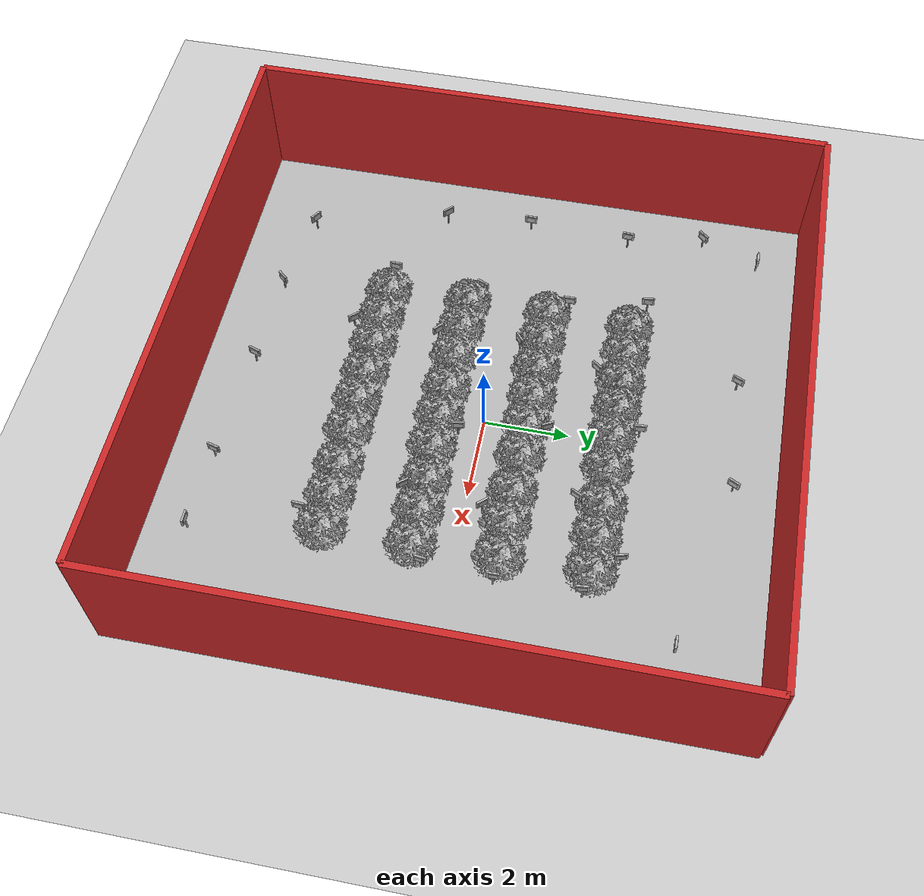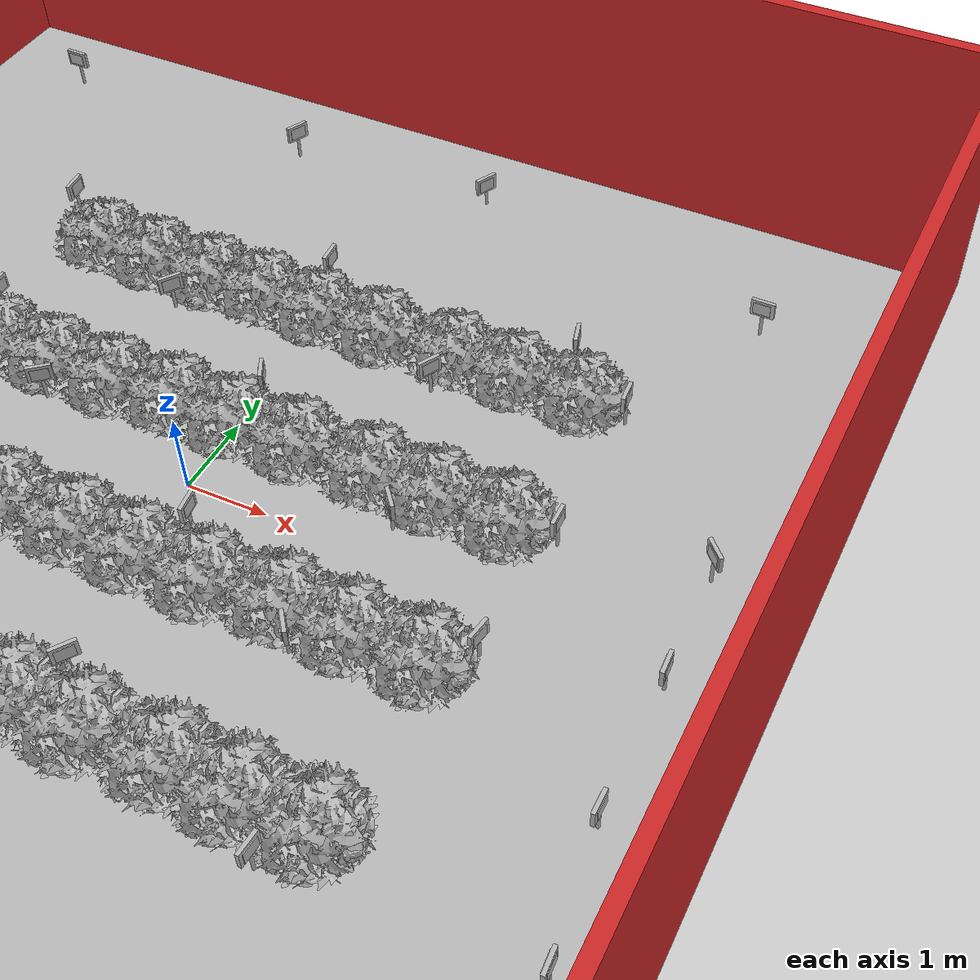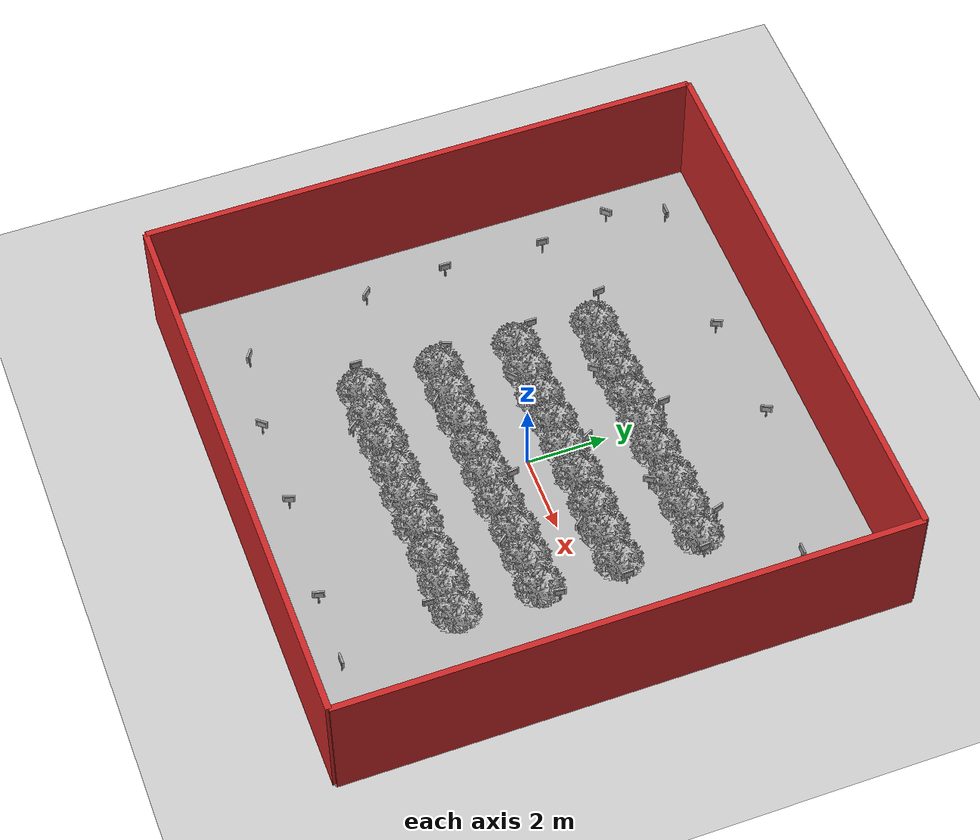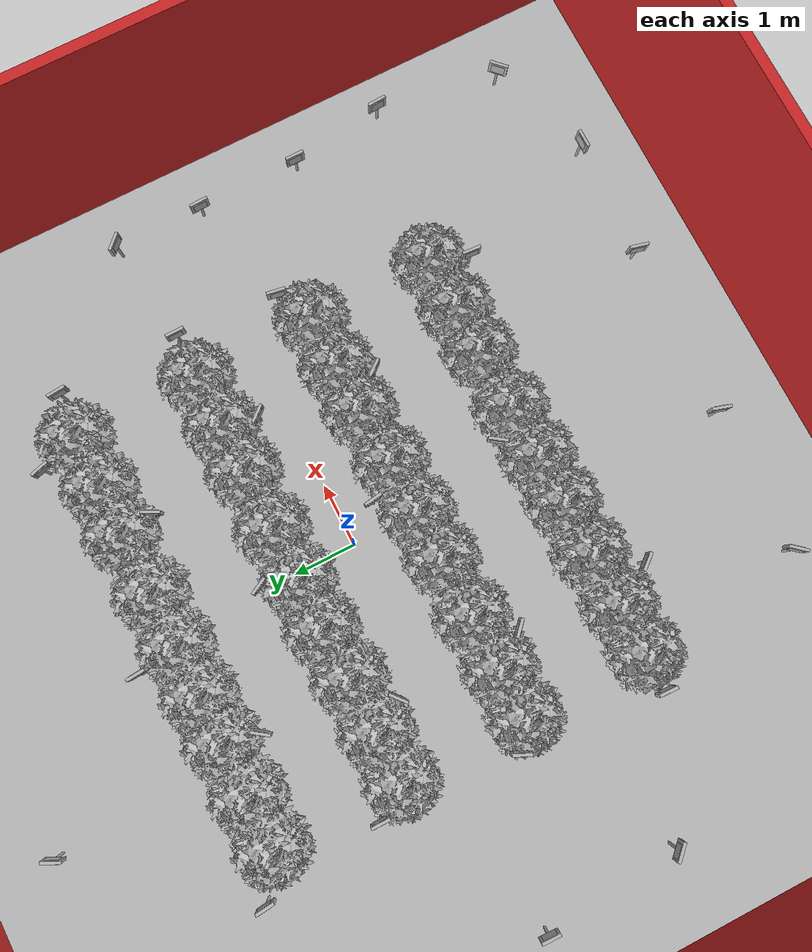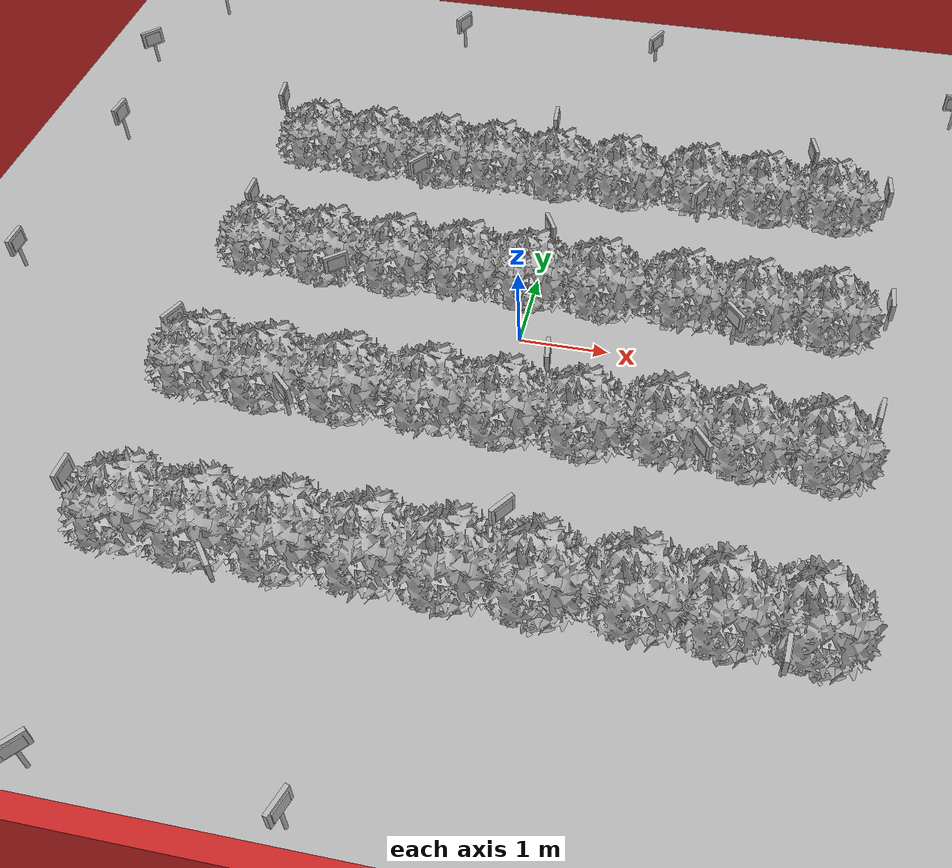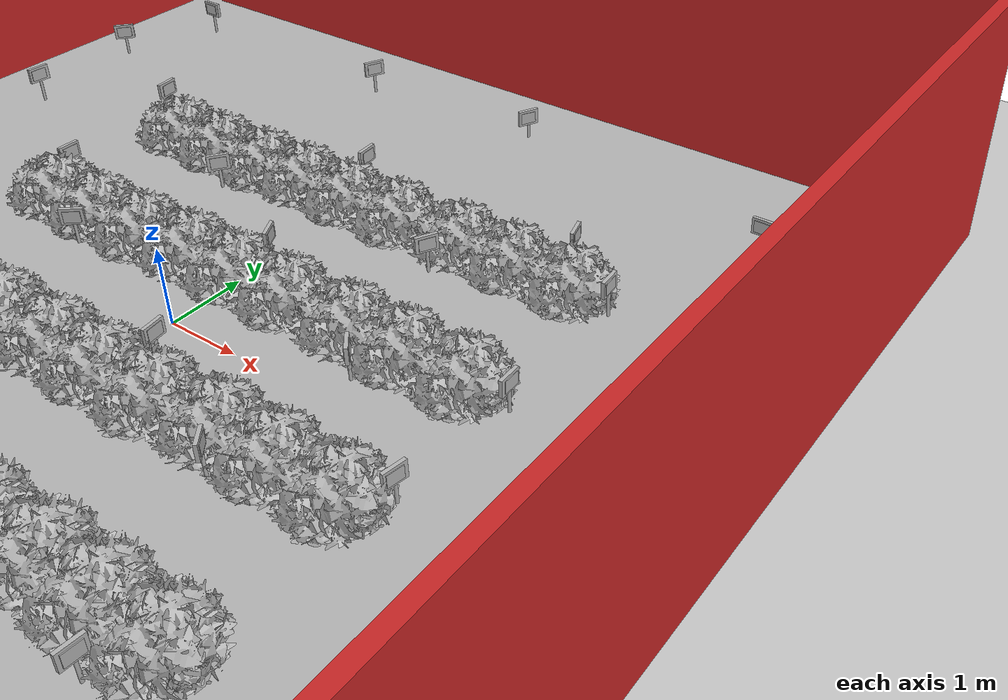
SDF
<sdf version="1.7">
 <world name="default">
  <light name="sun" type="directional">
   <pose>0 0 10 0 -0 0</pose>
   <diffuse>0.8 0.8 0.8 1</diffuse>
   <specular>0.2 0.2 0.2 1</specular>
   <attenuation>
    <range>1000</range>
    <constant>0.9</constant>
    <linear>0.01</linear>
    <quadratic>0.001</quadratic>
   </attenuation>
   <direction>-0.5 0.1 -0.9</direction>
   <spot><inner_angle>0</inner_angle><outer_angle>0</outer_angle><falloff>0</falloff></spot>
  </light>
  <model name="ground_plane">
   <static>1</static>
   <link name="link">
    <collision name="collision">
     <geometry><plane><normal>0 0 1</normal><size>100 100</size></plane></geometry>
     <surface><friction><ode><mu>100</mu><mu2>50</mu2></ode></friction></surface>
    </collision>
    <visual name="visual">
     <cast_shadows>0</cast_shadows>
     <geometry><plane><normal>0 0 1</normal><size>100 100</size></plane></geometry>
     <material>
      <script><uri>file://media/materials/scripts/gazebo.material</uri><name>Gazebo/Grey</name></script>
     </material>
    </visual>
   </link>
  </model>
  <gravity>0 0 -9.8</gravity>
  <magnetic_field>6e-06 2.3e-05 -4.2e-05</magnetic_field>
  <atmosphere type="adiabatic"/>
  <physics type="ode">
   <max_step_size>0.001</max_step_size>
   <real_time_factor>1</real_time_factor>
   <real_time_update_rate>1000</real_time_update_rate>
  </physics>
  <scene><ambient>0.4 0.4 0.4 1</ambient><background>0.7 0.7 0.7 1</background><shadows>1</shadows></scene>
  <spherical_coordinates>
   <surface_model>EARTH_WGS84</surface_model>
   <latitude_deg>0</latitude_deg>
   <longitude_deg>0</longitude_deg>
   <elevation>0</elevation>
   <heading_deg>0</heading_deg>
  </spherical_coordinates>
  <model name="paredladrillo">
   <pose>-0.28097 -0.036634 0 0 -0 0</pose>
   <link name="Wall_0">
    <collision name="Wall_0_Collision">
     <geometry><box><size>14 0.15 4</size></box></geometry>
     <pose>0 0 1.25 0 -0 0</pose>
    </collision>
    <visual name="Wall_0_Visual">
     <pose>0 0 1.25 0 -0 0</pose>
     <geometry><box><size>14 0.15 4</size></box></geometry>
     <material>
      <script>
       <uri>model://paredladrillo/materials/scripts</uri>
       <uri>model://paredladrillo/materials/textures</uri>
       <name>textur/pared</name>
      </script>
      <ambient>1 1 1 1</ambient>
     </material>
     <meta><layer>0</layer></meta>
    </visual>
    <pose>-7 -0 0 0 -0 1.5708</pose>
   </link>
   <link name="Wall_1">
    <collision name="Wall_1_Collision">
     <geometry><box><size>14 0.15 4</size></box></geometry>
     <pose>0 0 1.25 0 -0 0</pose>
    </collision>
    <visual name="Wall_1_Visual">
     <pose>0 0 1.25 0 -0 0</pose>
     <geometry><box><size>14 0.15 4</size></box></geometry>
     <material>
      <script>
       <uri>model://paredladrillo/materials/scripts</uri>
       <uri>model://paredladrillo/materials/textures</uri>
       <name>textur/pared</name>
      </script>
      <ambient>1 1 1 1</ambient>
     </material>
     <meta><layer>0</layer></meta>
    </visual>
    <pose>1e-06 7 0 0 -0 0</pose>
   </link>
   <link name="Wall_2">
    <collision name="Wall_2_Collision">
     <geometry><box><size>14 0.15 4</size></box></geometry>
     <pose>0 0 1.25 0 -0 0</pose>
    </collision>
    <visual name="Wall_2_Visual">
     <pose>0 0 1.25 0 -0 0</pose>
     <geometry><box><size>14 0.15 4</size></box></geometry>
     <material>
      <script>
       <uri>model://paredladrillo/materials/scripts</uri>
       <uri>model://paredladrillo/materials/textures</uri>
       <name>textur/pared</name>
      </script>
      <ambient>1 1 1 1</ambient>
     </material>
     <meta><layer>0</layer></meta>
    </visual>
    <pose>7 -0 0 0 -0 -1.5708</pose>
   </link>
   <link name="Wall_3">
    <collision name="Wall_3_Collision">
     <geometry><box><size>14 0.15 4</size></box></geometry>
     <pose>0 0 1.25 0 -0 0</pose>
    </collision>
    <visual name="Wall_3_Visual">
     <pose>0 0 1.25 0 -0 0</pose>
     <geometry><box><size>14 0.15 4</size></box></geometry>
     <material>
      <script>
       <uri>model://paredladrillo/materials/scripts</uri>
       <uri>model://paredladrillo/materials/textures</uri>
       <name>textur/pared</name>
      </script>
      <ambient>1 1 1 1</ambient>
     </material>
     <meta><layer>0</layer></meta>
    </visual>
    <pose>1e-06 -7 0 0 -0 3.14159</pose>
   </link>
   <static>1</static>
  </model>
  <model name="abbfre">
   <link name="link_0">
    <inertial>
     <mass>1</mass>
     <inertia>
      <ixx>0.166667</ixx>
      <ixy>0</ixy>
      <ixz>0</ixz>
      <iyy>0.166667</iyy>
      <iyz>0</iyz>
      <izz>0.166667</izz>
     </inertia>
    </inertial>
    <pose>0 0 -0 1.60917 -0 0</pose>
    <visual name="visual">
     <geometry><mesh><uri>model://abbfre/meshes/arbufres.obj</uri><scale>1 1 1</scale></mesh></geometry>
    </visual>
    <collision name="collision">
     <geometry><mesh><uri>model://abbfre/meshes/arbufres.obj</uri><scale>1 1 1</scale></mesh></geometry>
     <surface>
      <friction>
       <ode><mu>1</mu><mu2>1</mu2><fdir1>0 0 0</fdir1><slip1>0</slip1><slip2>0</slip2></ode>
       <torsional>
        <coefficient>1</coefficient>
        <patch_radius>0</patch_radius>
        <surface_radius>0</surface_radius>
        <use_patch_radius>1</use_patch_radius>
        <ode><slip>0</slip></ode>
       </torsional>
      </friction>
      <bounce><restitution_coefficient>0</restitution_coefficient><threshold>1e+06</threshold></bounce>
      <contact>
       <collide_without_contact>0</collide_without_contact>
       <collide_without_contact_bitmask>1</collide_without_contact_bitmask>
       <collide_bitmask>1</collide_bitmask>
       <ode>
        <soft_cfm>0</soft_cfm>
        <soft_erp>0.2</soft_erp>
        <kp>1e+13</kp>
        <kd>1</kd>
        <max_vel>0.01</max_vel>
        <min_depth>0</min_depth>
       </ode>
       <bullet>
        <split_impulse>1</split_impulse>
        <split_impulse_penetration_threshold>-0.01</split_impulse_penetration_threshold>
        <soft_cfm>0</soft_cfm>
        <soft_erp>0.2</soft_erp>
        <kp>1e+13</kp>
        <kd>1</kd>
       </bullet>
      </contact>
     </surface>
    </collision>
   </link>
   <static>1</static>
   <pose>-0.04815 1.09701 0 0 -0 0</pose>
  </model>
  <model name="abbfre_0">
   <link name="link_0">
    <inertial>
     <mass>1</mass>
     <inertia>
      <ixx>0.166667</ixx>
      <ixy>0</ixy>
      <ixz>0</ixz>
      <iyy>0.166667</iyy>
      <iyz>0</iyz>
      <izz>0.166667</izz>
     </inertia>
    </inertial>
    <pose>0 0 -0 1.60917 -0 0</pose>
    <visual name="visual">
     <geometry><mesh><uri>model://abbfre/meshes/arbufres.obj</uri><scale>1 1 1</scale></mesh></geometry>
    </visual>
    <collision name="collision">
     <geometry><mesh><uri>model://abbfre/meshes/arbufres.obj</uri><scale>1 1 1</scale></mesh></geometry>
     <surface>
      <friction>
       <ode><mu>1</mu><mu2>1</mu2><fdir1>0 0 0</fdir1><slip1>0</slip1><slip2>0</slip2></ode>
       <torsional>
        <coefficient>1</coefficient>
        <patch_radius>0</patch_radius>
        <surface_radius>0</surface_radius>
        <use_patch_radius>1</use_patch_radius>
        <ode><slip>0</slip></ode>
       </torsional>
      </friction>
      <bounce><restitution_coefficient>0</restitution_coefficient><threshold>1e+06</threshold></bounce>
      <contact>
       <collide_without_contact>0</collide_without_contact>
       <collide_without_contact_bitmask>1</collide_without_contact_bitmask>
       <collide_bitmask>1</collide_bitmask>
       <ode>
        <soft_cfm>0</soft_cfm>
        <soft_erp>0.2</soft_erp>
        <kp>1e+13</kp>
        <kd>1</kd>
        <max_vel>0.01</max_vel>
        <min_depth>0</min_depth>
       </ode>
       <bullet>
        <split_impulse>1</split_impulse>
        <split_impulse_penetration_threshold>-0.01</split_impulse_penetration_threshold>
        <soft_cfm>0</soft_cfm>
        <soft_erp>0.2</soft_erp>
        <kp>1e+13</kp>
        <kd>1</kd>
       </bullet>
      </contact>
     </surface>
    </collision>
   </link>
   <static>1</static>
   <pose>2.57031 1.10101 0 0 -0 0</pose>
  </model>
  <model name="abbfre_1">
   <link name="link_0">
    <inertial>
     <mass>1</mass>
     <inertia>
      <ixx>0.166667</ixx>
      <ixy>0</ixy>
      <ixz>0</ixz>
      <iyy>0.166667</iyy>
      <iyz>0</iyz>
      <izz>0.166667</izz>
     </inertia>
    </inertial>
    <pose>0 0 -0 1.60917 -0 0</pose>
    <visual name="visual">
     <geometry><mesh><uri>model://abbfre/meshes/arbufres.obj</uri><scale>1 1 1</scale></mesh></geometry>
    </visual>
    <collision name="collision">
     <geometry><mesh><uri>model://abbfre/meshes/arbufres.obj</uri><scale>1 1 1</scale></mesh></geometry>
     <surface>
      <friction>
       <ode><mu>1</mu><mu2>1</mu2><fdir1>0 0 0</fdir1><slip1>0</slip1><slip2>0</slip2></ode>
       <torsional>
        <coefficient>1</coefficient>
        <patch_radius>0</patch_radius>
        <surface_radius>0</surface_radius>
        <use_patch_radius>1</use_patch_radius>
        <ode><slip>0</slip></ode>
       </torsional>
      </friction>
      <bounce><restitution_coefficient>0</restitution_coefficient><threshold>1e+06</threshold></bounce>
      <contact>
       <collide_without_contact>0</collide_without_contact>
       <collide_without_contact_bitmask>1</collide_without_contact_bitmask>
       <collide_bitmask>1</collide_bitmask>
       <ode>
        <soft_cfm>0</soft_cfm>
        <soft_erp>0.2</soft_erp>
        <kp>1e+13</kp>
        <kd>1</kd>
        <max_vel>0.01</max_vel>
        <min_depth>0</min_depth>
       </ode>
       <bullet>
        <split_impulse>1</split_impulse>
        <split_impulse_penetration_threshold>-0.01</split_impulse_penetration_threshold>
        <soft_cfm>0</soft_cfm>
        <soft_erp>0.2</soft_erp>
        <kp>1e+13</kp>
        <kd>1</kd>
       </bullet>
      </contact>
     </surface>
    </collision>
   </link>
   <static>1</static>
   <pose>-2.51808 1.05435 0 0 -0 0</pose>
  </model>
  <model name="abbfre_2">
   <link name="link_0">
    <inertial>
     <mass>1</mass>
     <inertia>
      <ixx>0.166667</ixx>
      <ixy>0</ixy>
      <ixz>0</ixz>
      <iyy>0.166667</iyy>
      <iyz>0</iyz>
      <izz>0.166667</izz>
     </inertia>
    </inertial>
    <pose>0 0 -0 1.60917 -0 0</pose>
    <visual name="visual">
     <geometry><mesh><uri>model://abbfre/meshes/arbufres.obj</uri><scale>1 1 1</scale></mesh></geometry>
    </visual>
    <collision name="collision">
     <geometry><mesh><uri>model://abbfre/meshes/arbufres.obj</uri><scale>1 1 1</scale></mesh></geometry>
     <surface>
      <friction>
       <ode><mu>1</mu><mu2>1</mu2><fdir1>0 0 0</fdir1><slip1>0</slip1><slip2>0</slip2></ode>
       <torsional>
        <coefficient>1</coefficient>
        <patch_radius>0</patch_radius>
        <surface_radius>0</surface_radius>
        <use_patch_radius>1</use_patch_radius>
        <ode><slip>0</slip></ode>
       </torsional>
      </friction>
      <bounce><restitution_coefficient>0</restitution_coefficient><threshold>1e+06</threshold></bounce>
      <contact>
       <collide_without_contact>0</collide_without_contact>
       <collide_without_contact_bitmask>1</collide_without_contact_bitmask>
       <collide_bitmask>1</collide_bitmask>
       <ode>
        <soft_cfm>0</soft_cfm>
        <soft_erp>0.2</soft_erp>
        <kp>1e+13</kp>
        <kd>1</kd>
        <max_vel>0.01</max_vel>
        <min_depth>0</min_depth>
       </ode>
       <bullet>
        <split_impulse>1</split_impulse>
        <split_impulse_penetration_threshold>-0.01</split_impulse_penetration_threshold>
        <soft_cfm>0</soft_cfm>
        <soft_erp>0.2</soft_erp>
        <kp>1e+13</kp>
        <kd>1</kd>
       </bullet>
      </contact>
     </surface>
    </collision>
   </link>
   <static>1</static>
   <pose>0.065433 -0.946013 0 0 -0 0</pose>
  </model>
  <model name="abbfre_3">
   <link name="link_0">
    <inertial>
     <mass>1</mass>
     <inertia>
      <ixx>0.166667</ixx>
      <ixy>0</ixy>
      <ixz>0</ixz>
      <iyy>0.166667</iyy>
      <iyz>0</iyz>
      <izz>0.166667</izz>
     </inertia>
    </inertial>
    <pose>0 0 -0 1.60917 -0 0</pose>
    <visual name="visual">
     <geometry><mesh><uri>model://abbfre/meshes/arbufres.obj</uri><scale>1 1 1</scale></mesh></geometry>
    </visual>
    <collision name="collision">
     <geometry><mesh><uri>model://abbfre/meshes/arbufres.obj</uri><scale>1 1 1</scale></mesh></geometry>
     <surface>
      <friction>
       <ode><mu>1</mu><mu2>1</mu2><fdir1>0 0 0</fdir1><slip1>0</slip1><slip2>0</slip2></ode>
       <torsional>
        <coefficient>1</coefficient>
        <patch_radius>0</patch_radius>
        <surface_radius>0</surface_radius>
        <use_patch_radius>1</use_patch_radius>
        <ode><slip>0</slip></ode>
       </torsional>
      </friction>
      <bounce><restitution_coefficient>0</restitution_coefficient><threshold>1e+06</threshold></bounce>
      <contact>
       <collide_without_contact>0</collide_without_contact>
       <collide_without_contact_bitmask>1</collide_without_contact_bitmask>
       <collide_bitmask>1</collide_bitmask>
       <ode>
        <soft_cfm>0</soft_cfm>
        <soft_erp>0.2</soft_erp>
        <kp>1e+13</kp>
        <kd>1</kd>
        <max_vel>0.01</max_vel>
        <min_depth>0</min_depth>
       </ode>
       <bullet>
        <split_impulse>1</split_impulse>
        <split_impulse_penetration_threshold>-0.01</split_impulse_penetration_threshold>
        <soft_cfm>0</soft_cfm>
        <soft_erp>0.2</soft_erp>
        <kp>1e+13</kp>
        <kd>1</kd>
       </bullet>
      </contact>
     </surface>
    </collision>
   </link>
   <static>1</static>
   <pose>-2.52739 -0.955458 0 0 -0 0</pose>
  </model>
  <model name="abbfre_4">
   <link name="link_0">
    <inertial>
     <mass>1</mass>
     <inertia>
      <ixx>0.166667</ixx>
      <ixy>0</ixy>
      <ixz>0</ixz>
      <iyy>0.166667</iyy>
      <iyz>0</iyz>
      <izz>0.166667</izz>
     </inertia>
    </inertial>
    <pose>0 0 -0 1.60917 -0 0</pose>
    <visual name="visual">
     <geometry><mesh><uri>model://abbfre/meshes/arbufres.obj</uri><scale>1 1 1</scale></mesh></geometry>
    </visual>
    <collision name="collision">
     <geometry><mesh><uri>model://abbfre/meshes/arbufres.obj</uri><scale>1 1 1</scale></mesh></geometry>
     <surface>
      <friction>
       <ode><mu>1</mu><mu2>1</mu2><fdir1>0 0 0</fdir1><slip1>0</slip1><slip2>0</slip2></ode>
       <torsional>
        <coefficient>1</coefficient>
        <patch_radius>0</patch_radius>
        <surface_radius>0</surface_radius>
        <use_patch_radius>1</use_patch_radius>
        <ode><slip>0</slip></ode>
       </torsional>
      </friction>
      <bounce><restitution_coefficient>0</restitution_coefficient><threshold>1e+06</threshold></bounce>
      <contact>
       <collide_without_contact>0</collide_without_contact>
       <collide_without_contact_bitmask>1</collide_without_contact_bitmask>
       <collide_bitmask>1</collide_bitmask>
       <ode>
        <soft_cfm>0</soft_cfm>
        <soft_erp>0.2</soft_erp>
        <kp>1e+13</kp>
        <kd>1</kd>
        <max_vel>0.01</max_vel>
        <min_depth>0</min_depth>
       </ode>
       <bullet>
        <split_impulse>1</split_impulse>
        <split_impulse_penetration_threshold>-0.01</split_impulse_penetration_threshold>
        <soft_cfm>0</soft_cfm>
        <soft_erp>0.2</soft_erp>
        <kp>1e+13</kp>
        <kd>1</kd>
       </bullet>
      </contact>
     </surface>
    </collision>
   </link>
   <static>1</static>
   <pose>2.62048 -0.87774 0 0 -0 0</pose>
  </model>
  <model name="abbfre_5">
   <link name="link_0">
    <inertial>
     <mass>1</mass>
     <inertia>
      <ixx>0.166667</ixx>
      <ixy>0</ixy>
      <ixz>0</ixz>
      <iyy>0.166667</iyy>
      <iyz>0</iyz>
      <izz>0.166667</izz>
     </inertia>
    </inertial>
    <pose>0 0 -0 1.60917 -0 0</pose>
    <visual name="visual">
     <geometry><mesh><uri>model://abbfre/meshes/arbufres.obj</uri><scale>1 1 1</scale></mesh></geometry>
    </visual>
    <collision name="collision">
     <geometry><mesh><uri>model://abbfre/meshes/arbufres.obj</uri><scale>1 1 1</scale></mesh></geometry>
     <surface>
      <friction>
       <ode><mu>1</mu><mu2>1</mu2><fdir1>0 0 0</fdir1><slip1>0</slip1><slip2>0</slip2></ode>
       <torsional>
        <coefficient>1</coefficient>
        <patch_radius>0</patch_radius>
        <surface_radius>0</surface_radius>
        <use_patch_radius>1</use_patch_radius>
        <ode><slip>0</slip></ode>
       </torsional>
      </friction>
      <bounce><restitution_coefficient>0</restitution_coefficient><threshold>1e+06</threshold></bounce>
      <contact>
       <collide_without_contact>0</collide_without_contact>
       <collide_without_contact_bitmask>1</collide_without_contact_bitmask>
       <collide_bitmask>1</collide_bitmask>
       <ode>
        <soft_cfm>0</soft_cfm>
        <soft_erp>0.2</soft_erp>
        <kp>1e+13</kp>
        <kd>1</kd>
        <max_vel>0.01</max_vel>
        <min_depth>0</min_depth>
       </ode>
       <bullet>
        <split_impulse>1</split_impulse>
        <split_impulse_penetration_threshold>-0.01</split_impulse_penetration_threshold>
        <soft_cfm>0</soft_cfm>
        <soft_erp>0.2</soft_erp>
        <kp>1e+13</kp>
        <kd>1</kd>
       </bullet>
      </contact>
     </surface>
    </collision>
   </link>
   <static>1</static>
   <pose>-2.51391 -2.9563 0 0 -0 0</pose>
  </model>
  <model name="abbfre_6">
   <link name="link_0">
    <inertial>
     <mass>1</mass>
     <inertia>
      <ixx>0.166667</ixx>
      <ixy>0</ixy>
      <ixz>0</ixz>
      <iyy>0.166667</iyy>
      <iyz>0</iyz>
      <izz>0.166667</izz>
     </inertia>
    </inertial>
    <pose>0 0 -0 1.60917 -0 0</pose>
    <visual name="visual">
     <geometry><mesh><uri>model://abbfre/meshes/arbufres.obj</uri><scale>1 1 1</scale></mesh></geometry>
    </visual>
    <collision name="collision">
     <geometry><mesh><uri>model://abbfre/meshes/arbufres.obj</uri><scale>1 1 1</scale></mesh></geometry>
     <surface>
      <friction>
       <ode><mu>1</mu><mu2>1</mu2><fdir1>0 0 0</fdir1><slip1>0</slip1><slip2>0</slip2></ode>
       <torsional>
        <coefficient>1</coefficient>
        <patch_radius>0</patch_radius>
        <surface_radius>0</surface_radius>
        <use_patch_radius>1</use_patch_radius>
        <ode><slip>0</slip></ode>
       </torsional>
      </friction>
      <bounce><restitution_coefficient>0</restitution_coefficient><threshold>1e+06</threshold></bounce>
      <contact>
       <collide_without_contact>0</collide_without_contact>
       <collide_without_contact_bitmask>1</collide_without_contact_bitmask>
       <collide_bitmask>1</collide_bitmask>
       <ode>
        <soft_cfm>0</soft_cfm>
        <soft_erp>0.2</soft_erp>
        <kp>1e+13</kp>
        <kd>1</kd>
        <max_vel>0.01</max_vel>
        <min_depth>0</min_depth>
       </ode>
       <bullet>
        <split_impulse>1</split_impulse>
        <split_impulse_penetration_threshold>-0.01</split_impulse_penetration_threshold>
        <soft_cfm>0</soft_cfm>
        <soft_erp>0.2</soft_erp>
        <kp>1e+13</kp>
        <kd>1</kd>
       </bullet>
      </contact>
     </surface>
    </collision>
   </link>
   <static>1</static>
   <pose>-0.009938 -2.95191 0 0 -0 0</pose>
  </model>
  <model name="abbfre_7">
   <link name="link_0">
    <inertial>
     <mass>1</mass>
     <inertia>
      <ixx>0.166667</ixx>
      <ixy>0</ixy>
      <ixz>0</ixz>
      <iyy>0.166667</iyy>
      <iyz>0</iyz>
      <izz>0.166667</izz>
     </inertia>
    </inertial>
    <pose>0 0 -0 1.60917 -0 0</pose>
    <visual name="visual">
     <geometry><mesh><uri>model://abbfre/meshes/arbufres.obj</uri><scale>1 1 1</scale></mesh></geometry>
    </visual>
    <collision name="collision">
     <geometry><mesh><uri>model://abbfre/meshes/arbufres.obj</uri><scale>1 1 1</scale></mesh></geometry>
     <surface>
      <friction>
       <ode><mu>1</mu><mu2>1</mu2><fdir1>0 0 0</fdir1><slip1>0</slip1><slip2>0</slip2></ode>
       <torsional>
        <coefficient>1</coefficient>
        <patch_radius>0</patch_radius>
        <surface_radius>0</surface_radius>
        <use_patch_radius>1</use_patch_radius>
        <ode><slip>0</slip></ode>
       </torsional>
      </friction>
      <bounce><restitution_coefficient>0</restitution_coefficient><threshold>1e+06</threshold></bounce>
      <contact>
       <collide_without_contact>0</collide_without_contact>
       <collide_without_contact_bitmask>1</collide_without_contact_bitmask>
       <collide_bitmask>1</collide_bitmask>
       <ode>
        <soft_cfm>0</soft_cfm>
        <soft_erp>0.2</soft_erp>
        <kp>1e+13</kp>
        <kd>1</kd>
        <max_vel>0.01</max_vel>
        <min_depth>0</min_depth>
       </ode>
       <bullet>
        <split_impulse>1</split_impulse>
        <split_impulse_penetration_threshold>-0.01</split_impulse_penetration_threshold>
        <soft_cfm>0</soft_cfm>
        <soft_erp>0.2</soft_erp>
        <kp>1e+13</kp>
        <kd>1</kd>
       </bullet>
      </contact>
     </surface>
    </collision>
   </link>
   <static>1</static>
   <pose>2.60583 -2.92562 0 0 -0 0</pose>
  </model>
  <model name="abbfre_8">
   <link name="link_0">
    <inertial>
     <mass>1</mass>
     <inertia>
      <ixx>0.166667</ixx>
      <ixy>0</ixy>
      <ixz>0</ixz>
      <iyy>0.166667</iyy>
      <iyz>0</iyz>
      <izz>0.166667</izz>
     </inertia>
    </inertial>
    <pose>0 0 -0 1.60917 -0 0</pose>
    <visual name="visual">
     <geometry><mesh><uri>model://abbfre/meshes/arbufres.obj</uri><scale>1 1 1</scale></mesh></geometry>
    </visual>
    <collision name="collision">
     <geometry><mesh><uri>model://abbfre/meshes/arbufres.obj</uri><scale>1 1 1</scale></mesh></geometry>
     <surface>
      <friction>
       <ode><mu>1</mu><mu2>1</mu2><fdir1>0 0 0</fdir1><slip1>0</slip1><slip2>0</slip2></ode>
       <torsional>
        <coefficient>1</coefficient>
        <patch_radius>0</patch_radius>
        <surface_radius>0</surface_radius>
        <use_patch_radius>1</use_patch_radius>
        <ode><slip>0</slip></ode>
       </torsional>
      </friction>
      <bounce><restitution_coefficient>0</restitution_coefficient><threshold>1e+06</threshold></bounce>
      <contact>
       <collide_without_contact>0</collide_without_contact>
       <collide_without_contact_bitmask>1</collide_without_contact_bitmask>
       <collide_bitmask>1</collide_bitmask>
       <ode>
        <soft_cfm>0</soft_cfm>
        <soft_erp>0.2</soft_erp>
        <kp>1e+13</kp>
        <kd>1</kd>
        <max_vel>0.01</max_vel>
        <min_depth>0</min_depth>
       </ode>
       <bullet>
        <split_impulse>1</split_impulse>
        <split_impulse_penetration_threshold>-0.01</split_impulse_penetration_threshold>
        <soft_cfm>0</soft_cfm>
        <soft_erp>0.2</soft_erp>
        <kp>1e+13</kp>
        <kd>1</kd>
       </bullet>
      </contact>
     </surface>
    </collision>
   </link>
   <static>1</static>
   <pose>2.54008 3.13594 0 0 -0 0</pose>
  </model>
  <model name="abbfre_9">
   <link name="link_0">
    <inertial>
     <mass>1</mass>
     <inertia>
      <ixx>0.166667</ixx>
      <ixy>0</ixy>
      <ixz>0</ixz>
      <iyy>0.166667</iyy>
      <iyz>0</iyz>
      <izz>0.166667</izz>
     </inertia>
    </inertial>
    <pose>0 0 -0 1.60917 -0 0</pose>
    <visual name="visual">
     <geometry><mesh><uri>model://abbfre/meshes/arbufres.obj</uri><scale>1 1 1</scale></mesh></geometry>
    </visual>
    <collision name="collision">
     <geometry><mesh><uri>model://abbfre/meshes/arbufres.obj</uri><scale>1 1 1</scale></mesh></geometry>
     <surface>
      <friction>
       <ode><mu>1</mu><mu2>1</mu2><fdir1>0 0 0</fdir1><slip1>0</slip1><slip2>0</slip2></ode>
       <torsional>
        <coefficient>1</coefficient>
        <patch_radius>0</patch_radius>
        <surface_radius>0</surface_radius>
        <use_patch_radius>1</use_patch_radius>
        <ode><slip>0</slip></ode>
       </torsional>
      </friction>
      <bounce><restitution_coefficient>0</restitution_coefficient><threshold>1e+06</threshold></bounce>
      <contact>
       <collide_without_contact>0</collide_without_contact>
       <collide_without_contact_bitmask>1</collide_without_contact_bitmask>
       <collide_bitmask>1</collide_bitmask>
       <ode>
        <soft_cfm>0</soft_cfm>
        <soft_erp>0.2</soft_erp>
        <kp>1e+13</kp>
        <kd>1</kd>
        <max_vel>0.01</max_vel>
        <min_depth>0</min_depth>
       </ode>
       <bullet>
        <split_impulse>1</split_impulse>
        <split_impulse_penetration_threshold>-0.01</split_impulse_penetration_threshold>
        <soft_cfm>0</soft_cfm>
        <soft_erp>0.2</soft_erp>
        <kp>1e+13</kp>
        <kd>1</kd>
       </bullet>
      </contact>
     </surface>
    </collision>
   </link>
   <static>1</static>
   <pose>-0.104269 3.10996 0 0 -0 0</pose>
  </model>
  <model name="abbfre_10">
   <link name="link_0">
    <inertial>
     <mass>1</mass>
     <inertia>
      <ixx>0.166667</ixx>
      <ixy>0</ixy>
      <ixz>0</ixz>
      <iyy>0.166667</iyy>
      <iyz>0</iyz>
      <izz>0.166667</izz>
     </inertia>
    </inertial>
    <pose>0 0 -0 1.60917 -0 0</pose>
    <visual name="visual">
     <geometry><mesh><uri>model://abbfre/meshes/arbufres.obj</uri><scale>1 1 1</scale></mesh></geometry>
    </visual>
    <collision name="collision">
     <geometry><mesh><uri>model://abbfre/meshes/arbufres.obj</uri><scale>1 1 1</scale></mesh></geometry>
     <surface>
      <friction>
       <ode><mu>1</mu><mu2>1</mu2><fdir1>0 0 0</fdir1><slip1>0</slip1><slip2>0</slip2></ode>
       <torsional>
        <coefficient>1</coefficient>
        <patch_radius>0</patch_radius>
        <surface_radius>0</surface_radius>
        <use_patch_radius>1</use_patch_radius>
        <ode><slip>0</slip></ode>
       </torsional>
      </friction>
      <bounce><restitution_coefficient>0</restitution_coefficient><threshold>1e+06</threshold></bounce>
      <contact>
       <collide_without_contact>0</collide_without_contact>
       <collide_without_contact_bitmask>1</collide_without_contact_bitmask>
       <collide_bitmask>1</collide_bitmask>
       <ode>
        <soft_cfm>0</soft_cfm>
        <soft_erp>0.2</soft_erp>
        <kp>1e+13</kp>
        <kd>1</kd>
        <max_vel>0.01</max_vel>
        <min_depth>0</min_depth>
       </ode>
       <bullet>
        <split_impulse>1</split_impulse>
        <split_impulse_penetration_threshold>-0.01</split_impulse_penetration_threshold>
        <soft_cfm>0</soft_cfm>
        <soft_erp>0.2</soft_erp>
        <kp>1e+13</kp>
        <kd>1</kd>
       </bullet>
      </contact>
     </surface>
    </collision>
   </link>
   <static>1</static>
   <pose>-2.49032 3.10051 0 0 -0 0</pose>
  </model>
  <model name="piso_plano">
   <link name="link_0">
    <inertial>
     <mass>14.2171</mass>
     <inertia><ixx>310.23</ixx><ixy>0</ixy><ixz>0</ixz><iyy>311.692</iyy><iyz>0</iyz><izz>621.915</izz></inertia>
    </inertial>
    <visual name="visual">
     <geometry><box><size>14 14 0.024508</size></box></geometry>
     <material>
      <lighting>1</lighting>
      <script>
       <uri>model://piso_plano/materials/scripts</uri>
       <uri>model://piso_plano/materials/textures</uri>
       <name>textur/pis</name>
      </script>
      <shader type="pixel"/>
     </material>
    </visual>
    <collision name="collision">
     <geometry><box><size>14 14 0.024508</size></box></geometry>
     <surface>
      <friction>
       <ode><mu>1</mu><mu2>1</mu2><fdir1>0 0 0</fdir1><slip1>0</slip1><slip2>0</slip2></ode>
       <torsional>
        <coefficient>1</coefficient>
        <patch_radius>0</patch_radius>
        <surface_radius>0</surface_radius>
        <use_patch_radius>1</use_patch_radius>
        <ode><slip>0</slip></ode>
       </torsional>
      </friction>
      <bounce><restitution_coefficient>0</restitution_coefficient><threshold>1e+06</threshold></bounce>
      <contact>
       <collide_without_contact>0</collide_without_contact>
       <collide_without_contact_bitmask>1</collide_without_contact_bitmask>
       <collide_bitmask>1</collide_bitmask>
       <ode>
        <soft_cfm>0</soft_cfm>
        <soft_erp>0.2</soft_erp>
        <kp>1e+13</kp>
        <kd>1</kd>
        <max_vel>0.01</max_vel>
        <min_depth>0</min_depth>
       </ode>
       <bullet>
        <split_impulse>1</split_impulse>
        <split_impulse_penetration_threshold>-0.01</split_impulse_penetration_threshold>
        <soft_cfm>0</soft_cfm>
        <soft_erp>0.2</soft_erp>
        <kp>1e+13</kp>
        <kd>1</kd>
       </bullet>
      </contact>
     </surface>
    </collision>
   </link>
   <static>1</static>
   <pose>-0.240554 -0.064653 0 0 -0 0</pose>
  </model>
  <model name="letrero_riego">
   <link name="link_0">
    <inertial>
     <mass>0.0543151</mass>
     <inertia>
      <ixx>4.90351e-06</ixx>
      <ixy>0</ixy>
      <ixz>0</ixz>
      <iyy>4.90351e-06</iyy>
      <iyz>0</iyz>
      <izz>1.12837e-07</izz>
     </inertia>
    </inertial>
    <pose>0.002515 0.005109 0.153562 0 -0 0</pose>
    <visual name="visual">
     <geometry><cylinder><radius>0.0203836</radius><length>0.327243</length></cylinder></geometry>
     <material>
      <lighting>1</lighting>
      <script>
       <uri>model://letrero_riego/madera/scripts</uri>
       <uri>model://letrero_riego/madera/textures</uri>
       <name>textur/madera</name>
      </script>
      <shader type="pixel"/>
      <emissive>0 0 0 1</emissive>
     </material>
    </visual>
    <collision name="collision">
     <geometry><cylinder><radius>0.020384</radius><length>0.327243</length></cylinder></geometry>
     <surface>
      <friction>
       <ode><mu>1</mu><mu2>1</mu2><fdir1>0 0 0</fdir1><slip1>0</slip1><slip2>0</slip2></ode>
       <torsional>
        <coefficient>1</coefficient>
        <patch_radius>0</patch_radius>
        <surface_radius>0</surface_radius>
        <use_patch_radius>1</use_patch_radius>
        <ode><slip>0</slip></ode>
       </torsional>
      </friction>
      <bounce><restitution_coefficient>0</restitution_coefficient><threshold>1e+06</threshold></bounce>
      <contact>
       <collide_without_contact>0</collide_without_contact>
       <collide_without_contact_bitmask>1</collide_without_contact_bitmask>
       <collide_bitmask>1</collide_bitmask>
       <ode>
        <soft_cfm>0</soft_cfm>
        <soft_erp>0.2</soft_erp>
        <kp>1e+13</kp>
        <kd>1</kd>
        <max_vel>0.01</max_vel>
        <min_depth>0</min_depth>
       </ode>
       <bullet>
        <split_impulse>1</split_impulse>
        <split_impulse_penetration_threshold>-0.01</split_impulse_penetration_threshold>
        <soft_cfm>0</soft_cfm>
        <soft_erp>0.2</soft_erp>
        <kp>1e+13</kp>
        <kd>1</kd>
       </bullet>
      </contact>
     </surface>
    </collision>
   </link>
   <link name="link_1">
    <inertial>
     <mass>0.00299633</mass>
     <inertia>
      <ixx>1.27855e-05</ixx>
      <ixy>0</ixy>
      <ixz>0</ixz>
      <iyy>3.42923e-05</iyy>
      <iyz>0</iyz>
      <izz>2.25402e-05</izz>
     </inertia>
    </inertial>
    <pose>-0.001542 0.002452 0.422031 0 -0 0</pose>
    <visual name="visual">
     <geometry><box><size>0.296988 0.04549 0.221665</size></box></geometry>
     <material>
      <lighting>1</lighting>
      <script>
       <uri>model://letrero_riego/madera/scripts</uri>
       <uri>model://letrero_riego/madera/textures</uri>
       <name>textur/madera</name>
      </script>
      <shader type="pixel"/>
      <emissive>0 0 0 1</emissive>
     </material>
    </visual>
    <collision name="collision">
     <geometry><box><size>0.296988 0.04549 0.221665</size></box></geometry>
     <surface>
      <friction>
       <ode><mu>1</mu><mu2>1</mu2><fdir1>0 0 0</fdir1><slip1>0</slip1><slip2>0</slip2></ode>
       <torsional>
        <coefficient>1</coefficient>
        <patch_radius>0</patch_radius>
        <surface_radius>0</surface_radius>
        <use_patch_radius>1</use_patch_radius>
        <ode><slip>0</slip></ode>
       </torsional>
      </friction>
      <bounce><restitution_coefficient>0</restitution_coefficient><threshold>1e+06</threshold></bounce>
      <contact>
       <collide_without_contact>0</collide_without_contact>
       <collide_without_contact_bitmask>1</collide_without_contact_bitmask>
       <collide_bitmask>1</collide_bitmask>
       <ode>
        <soft_cfm>0</soft_cfm>
        <soft_erp>0.2</soft_erp>
        <kp>1e+13</kp>
        <kd>1</kd>
        <max_vel>0.01</max_vel>
        <min_depth>0</min_depth>
       </ode>
       <bullet>
        <split_impulse>1</split_impulse>
        <split_impulse_penetration_threshold>-0.01</split_impulse_penetration_threshold>
        <soft_cfm>0</soft_cfm>
        <soft_erp>0.2</soft_erp>
        <kp>1e+13</kp>
        <kd>1</kd>
       </bullet>
      </contact>
     </surface>
    </collision>
   </link>
   <link name="link_2">
    <inertial>
     <mass>0.00173577</mass>
     <inertia>
      <ixx>4.23206e-06</ixx>
      <ixy>0</ixy>
      <ixz>0</ixz>
      <iyy>1.03921e-05</iyy>
      <iyz>0</iyz>
      <izz>7.37287e-06</izz>
     </inertia>
    </inertial>
    <pose>-0.010225 0.002657 0.421501 0 -0 0</pose>
    <visual name="visual">
     <geometry><box><size>0.216284 0.064749 0.15832</size></box></geometry>
     <material>
      <lighting>1</lighting>
      <script>
       <uri>model://letrero_riego/materials/scripts</uri>
       <uri>model://letrero_riego/materials/textures</uri>
       <name>textur/riego</name>
      </script>
      <shader type="pixel"/>
      <emissive>0 0 0 1</emissive>
     </material>
    </visual>
    <collision name="collision">
     <geometry><box><size>0.216284 0.064749 0.15832</size></box></geometry>
     <surface>
      <friction>
       <ode><mu>1</mu><mu2>1</mu2><fdir1>0 0 0</fdir1><slip1>0</slip1><slip2>0</slip2></ode>
       <torsional>
        <coefficient>1</coefficient>
        <patch_radius>0</patch_radius>
        <surface_radius>0</surface_radius>
        <use_patch_radius>1</use_patch_radius>
        <ode><slip>0</slip></ode>
       </torsional>
      </friction>
      <bounce><restitution_coefficient>0</restitution_coefficient><threshold>1e+06</threshold></bounce>
      <contact>
       <collide_without_contact>0</collide_without_contact>
       <collide_without_contact_bitmask>1</collide_without_contact_bitmask>
       <collide_bitmask>1</collide_bitmask>
       <ode>
        <soft_cfm>0</soft_cfm>
        <soft_erp>0.2</soft_erp>
        <kp>1e+13</kp>
        <kd>1</kd>
        <max_vel>0.01</max_vel>
        <min_depth>0</min_depth>
       </ode>
       <bullet>
        <split_impulse>1</split_impulse>
        <split_impulse_penetration_threshold>-0.01</split_impulse_penetration_threshold>
        <soft_cfm>0</soft_cfm>
        <soft_erp>0.2</soft_erp>
        <kp>1e+13</kp>
        <kd>1</kd>
       </bullet>
      </contact>
     </surface>
    </collision>
   </link>
   <joint name="link_0_JOINT_1" type="fixed">
    <parent>link_0</parent>
    <child>link_1</child>
    <physics>
     <ode><limit><cfm>0</cfm><erp>0.2</erp></limit><suspension><cfm>0</cfm><erp>0.2</erp></suspension></ode>
    </physics>
   </joint>
   <joint name="link_0_JOINT_2" type="fixed">
    <parent>link_0</parent>
    <child>link_2</child>
    <physics>
     <ode><limit><cfm>0</cfm><erp>0.2</erp></limit><suspension><cfm>0</cfm><erp>0.2</erp></suspension></ode>
    </physics>
   </joint>
   <static>1</static>
   <pose>3.93018 -0.662808 -0.049872 0 -0 1.41446</pose>
  </model>
  <model name="letrero_fresa">
   <link name="link_0">
    <inertial>
     <mass>0.00543151</mass>
     <inertia>
      <ixx>4.90351e-06</ixx>
      <ixy>0</ixy>
      <ixz>0</ixz>
      <iyy>4.90351e-06</iyy>
      <iyz>0</iyz>
      <izz>1.12837e-07</izz>
     </inertia>
    </inertial>
    <pose>0.002372 -0.000902 -0.178803 0 -0 0</pose>
    <visual name="visual">
     <geometry><cylinder><radius>0.0203836</radius><length>0.327243</length></cylinder></geometry>
     <material>
      <lighting>1</lighting>
      <script>
       <uri>model://letrero_fresa/madera/scripts</uri>
       <uri>model://letrero_fresa/madera/textures</uri>
       <name>textur/madera</name>
      </script>
      <shader type="pixel"/>
      <emissive>0 0 0 1</emissive>
     </material>
    </visual>
    <collision name="collision">
     <geometry><cylinder><radius>0.020384</radius><length>0.327243</length></cylinder></geometry>
     <surface>
      <friction>
       <ode><mu>1</mu><mu2>1</mu2><fdir1>0 0 0</fdir1><slip1>0</slip1><slip2>0</slip2></ode>
       <torsional>
        <coefficient>1</coefficient>
        <patch_radius>0</patch_radius>
        <surface_radius>0</surface_radius>
        <use_patch_radius>1</use_patch_radius>
        <ode><slip>0</slip></ode>
       </torsional>
      </friction>
      <bounce><restitution_coefficient>0</restitution_coefficient><threshold>1e+06</threshold></bounce>
      <contact>
       <collide_without_contact>0</collide_without_contact>
       <collide_without_contact_bitmask>1</collide_without_contact_bitmask>
       <collide_bitmask>1</collide_bitmask>
       <ode>
        <soft_cfm>0</soft_cfm>
        <soft_erp>0.2</soft_erp>
        <kp>1e+13</kp>
        <kd>1</kd>
        <max_vel>0.01</max_vel>
        <min_depth>0</min_depth>
       </ode>
       <bullet>
        <split_impulse>1</split_impulse>
        <split_impulse_penetration_threshold>-0.01</split_impulse_penetration_threshold>
        <soft_cfm>0</soft_cfm>
        <soft_erp>0.2</soft_erp>
        <kp>1e+13</kp>
        <kd>1</kd>
       </bullet>
      </contact>
     </surface>
    </collision>
   </link>
   <link name="link_1">
    <inertial>
     <mass>0.00299633</mass>
     <inertia>
      <ixx>1.27855e-05</ixx>
      <ixy>0</ixy>
      <ixz>0</ixz>
      <iyy>3.42923e-05</iyy>
      <iyz>0</iyz>
      <izz>2.25402e-05</izz>
     </inertia>
    </inertial>
    <pose>-0.001685 -0.003559 0.089666 0 -0 0</pose>
    <visual name="visual">
     <geometry><box><size>0.296988 0.04549 0.221665</size></box></geometry>
     <material>
      <lighting>1</lighting>
      <script>
       <uri>model://letrero_fresa/madera/scripts</uri>
       <uri>model://letrero_fresa/madera/textures</uri>
       <name>textur/madera</name>
      </script>
      <shader type="pixel"/>
      <emissive>0 0 0 1</emissive>
     </material>
    </visual>
    <collision name="collision">
     <geometry><box><size>0.296988 0.04549 0.221665</size></box></geometry>
     <surface>
      <friction>
       <ode><mu>1</mu><mu2>1</mu2><fdir1>0 0 0</fdir1><slip1>0</slip1><slip2>0</slip2></ode>
       <torsional>
        <coefficient>1</coefficient>
        <patch_radius>0</patch_radius>
        <surface_radius>0</surface_radius>
        <use_patch_radius>1</use_patch_radius>
        <ode><slip>0</slip></ode>
       </torsional>
      </friction>
      <bounce><restitution_coefficient>0</restitution_coefficient><threshold>1e+06</threshold></bounce>
      <contact>
       <collide_without_contact>0</collide_without_contact>
       <collide_without_contact_bitmask>1</collide_without_contact_bitmask>
       <collide_bitmask>1</collide_bitmask>
       <ode>
        <soft_cfm>0</soft_cfm>
        <soft_erp>0.2</soft_erp>
        <kp>1e+13</kp>
        <kd>1</kd>
        <max_vel>0.01</max_vel>
        <min_depth>0</min_depth>
       </ode>
       <bullet>
        <split_impulse>1</split_impulse>
        <split_impulse_penetration_threshold>-0.01</split_impulse_penetration_threshold>
        <soft_cfm>0</soft_cfm>
        <soft_erp>0.2</soft_erp>
        <kp>1e+13</kp>
        <kd>1</kd>
       </bullet>
      </contact>
     </surface>
    </collision>
   </link>
   <link name="link_2">
    <inertial>
     <mass>0.00219695</mass>
     <inertia>
      <ixx>5.34209e-06</ixx>
      <ixy>0</ixy>
      <ixz>0</ixz>
      <iyy>1.31531e-05</iyy>
      <iyz>0</iyz>
      <izz>9.31738e-06</izz>
     </inertia>
    </inertial>
    <pose>-0.001275 -0.005928 0.089136 0 -0 0</pose>
    <visual name="visual">
     <geometry><box><size>0.216284 0.06414 0.15832</size></box></geometry>
     <material>
      <lighting>1</lighting>
      <script>
       <uri>model://letrero_fresa/materials/scripts</uri>
       <uri>model://letrero_fresa/materials/textures</uri>
       <name>textur/difre</name>
      </script>
      <shader type="pixel"/>
      <emissive>0 0 0 1</emissive>
     </material>
    </visual>
    <collision name="collision">
     <geometry><box><size>0.216284 0.06414 0.15832</size></box></geometry>
     <surface>
      <friction>
       <ode><mu>1</mu><mu2>1</mu2><fdir1>0 0 0</fdir1><slip1>0</slip1><slip2>0</slip2></ode>
       <torsional>
        <coefficient>1</coefficient>
        <patch_radius>0</patch_radius>
        <surface_radius>0</surface_radius>
        <use_patch_radius>1</use_patch_radius>
        <ode><slip>0</slip></ode>
       </torsional>
      </friction>
      <bounce><restitution_coefficient>0</restitution_coefficient><threshold>1e+06</threshold></bounce>
      <contact>
       <collide_without_contact>0</collide_without_contact>
       <collide_without_contact_bitmask>1</collide_without_contact_bitmask>
       <collide_bitmask>1</collide_bitmask>
       <ode>
        <soft_cfm>0</soft_cfm>
        <soft_erp>0.2</soft_erp>
        <kp>1e+13</kp>
        <kd>1</kd>
        <max_vel>0.01</max_vel>
        <min_depth>0</min_depth>
       </ode>
       <bullet>
        <split_impulse>1</split_impulse>
        <split_impulse_penetration_threshold>-0.01</split_impulse_penetration_threshold>
        <soft_cfm>0</soft_cfm>
        <soft_erp>0.2</soft_erp>
        <kp>1e+13</kp>
        <kd>1</kd>
       </bullet>
      </contact>
     </surface>
    </collision>
   </link>
   <joint name="link_0_JOINT_1" type="fixed">
    <parent>link_0</parent>
    <child>link_1</child>
    <physics>
     <ode><limit><cfm>0</cfm><erp>0.2</erp></limit><suspension><cfm>0</cfm><erp>0.2</erp></suspension></ode>
    </physics>
   </joint>
   <joint name="link_0_JOINT_2" type="fixed">
    <parent>link_0</parent>
    <child>link_2</child>
    <physics>
     <ode><limit><cfm>0</cfm><erp>0.2</erp></limit><suspension><cfm>0</cfm><erp>0.2</erp></suspension></ode>
    </physics>
   </joint>
   <static>1</static>
   <pose>2.34438 0.414621 0.339683 0 0 -0.864343</pose>
  </model>
  <model name="letrero_fresa_0">
   <link name="link_0">
    <inertial>
     <mass>0.00543151</mass>
     <inertia>
      <ixx>4.90351e-06</ixx>
      <ixy>0</ixy>
      <ixz>0</ixz>
      <iyy>4.90351e-06</iyy>
      <iyz>0</iyz>
      <izz>1.12837e-07</izz>
     </inertia>
    </inertial>
    <pose>0.002372 -0.000902 -0.178803 0 -0 0</pose>
    <visual name="visual">
     <geometry><cylinder><radius>0.0203836</radius><length>0.327243</length></cylinder></geometry>
     <material>
      <lighting>1</lighting>
      <script>
       <uri>model://letrero_fresa/madera/scripts</uri>
       <uri>model://letrero_fresa/madera/textures</uri>
       <name>textur/madera</name>
      </script>
      <shader type="pixel"/>
      <emissive>0 0 0 1</emissive>
     </material>
    </visual>
    <collision name="collision">
     <geometry><cylinder><radius>0.020384</radius><length>0.327243</length></cylinder></geometry>
     <surface>
      <friction>
       <ode><mu>1</mu><mu2>1</mu2><fdir1>0 0 0</fdir1><slip1>0</slip1><slip2>0</slip2></ode>
       <torsional>
        <coefficient>1</coefficient>
        <patch_radius>0</patch_radius>
        <surface_radius>0</surface_radius>
        <use_patch_radius>1</use_patch_radius>
        <ode><slip>0</slip></ode>
       </torsional>
      </friction>
      <bounce><restitution_coefficient>0</restitution_coefficient><threshold>1e+06</threshold></bounce>
      <contact>
       <collide_without_contact>0</collide_without_contact>
       <collide_without_contact_bitmask>1</collide_without_contact_bitmask>
       <collide_bitmask>1</collide_bitmask>
       <ode>
        <soft_cfm>0</soft_cfm>
        <soft_erp>0.2</soft_erp>
        <kp>1e+13</kp>
        <kd>1</kd>
        <max_vel>0.01</max_vel>
        <min_depth>0</min_depth>
       </ode>
       <bullet>
        <split_impulse>1</split_impulse>
        <split_impulse_penetration_threshold>-0.01</split_impulse_penetration_threshold>
        <soft_cfm>0</soft_cfm>
        <soft_erp>0.2</soft_erp>
        <kp>1e+13</kp>
        <kd>1</kd>
       </bullet>
      </contact>
     </surface>
    </collision>
   </link>
   <link name="link_1">
    <inertial>
     <mass>0.00299633</mass>
     <inertia>
      <ixx>1.27855e-05</ixx>
      <ixy>0</ixy>
      <ixz>0</ixz>
      <iyy>3.42923e-05</iyy>
      <iyz>0</iyz>
      <izz>2.25402e-05</izz>
     </inertia>
    </inertial>
    <pose>-0.001685 -0.003559 0.089666 0 -0 0</pose>
    <visual name="visual">
     <geometry><box><size>0.296988 0.04549 0.221665</size></box></geometry>
     <material>
      <lighting>1</lighting>
      <script>
       <uri>model://letrero_fresa/madera/scripts</uri>
       <uri>model://letrero_fresa/madera/textures</uri>
       <name>textur/madera</name>
      </script>
      <shader type="pixel"/>
      <emissive>0 0 0 1</emissive>
     </material>
    </visual>
    <collision name="collision">
     <geometry><box><size>0.296988 0.04549 0.221665</size></box></geometry>
     <surface>
      <friction>
       <ode><mu>1</mu><mu2>1</mu2><fdir1>0 0 0</fdir1><slip1>0</slip1><slip2>0</slip2></ode>
       <torsional>
        <coefficient>1</coefficient>
        <patch_radius>0</patch_radius>
        <surface_radius>0</surface_radius>
        <use_patch_radius>1</use_patch_radius>
        <ode><slip>0</slip></ode>
       </torsional>
      </friction>
      <bounce><restitution_coefficient>0</restitution_coefficient><threshold>1e+06</threshold></bounce>
      <contact>
       <collide_without_contact>0</collide_without_contact>
       <collide_without_contact_bitmask>1</collide_without_contact_bitmask>
       <collide_bitmask>1</collide_bitmask>
       <ode>
        <soft_cfm>0</soft_cfm>
        <soft_erp>0.2</soft_erp>
        <kp>1e+13</kp>
        <kd>1</kd>
        <max_vel>0.01</max_vel>
        <min_depth>0</min_depth>
       </ode>
       <bullet>
        <split_impulse>1</split_impulse>
        <split_impulse_penetration_threshold>-0.01</split_impulse_penetration_threshold>
        <soft_cfm>0</soft_cfm>
        <soft_erp>0.2</soft_erp>
        <kp>1e+13</kp>
        <kd>1</kd>
       </bullet>
      </contact>
     </surface>
    </collision>
   </link>
   <link name="link_2">
    <inertial>
     <mass>0.00219695</mass>
     <inertia>
      <ixx>5.34209e-06</ixx>
      <ixy>0</ixy>
      <ixz>0</ixz>
      <iyy>1.31531e-05</iyy>
      <iyz>0</iyz>
      <izz>9.31738e-06</izz>
     </inertia>
    </inertial>
    <pose>-0.001275 -0.005928 0.089136 0 -0 0</pose>
    <visual name="visual">
     <geometry><box><size>0.216284 0.06414 0.15832</size></box></geometry>
     <material>
      <lighting>1</lighting>
      <script>
       <uri>model://letrero_fresa/materials/scripts</uri>
       <uri>model://letrero_fresa/materials/textures</uri>
       <name>textur/difre</name>
      </script>
      <shader type="pixel"/>
      <emissive>0 0 0 1</emissive>
     </material>
    </visual>
    <collision name="collision">
     <geometry><box><size>0.216284 0.06414 0.15832</size></box></geometry>
     <surface>
      <friction>
       <ode><mu>1</mu><mu2>1</mu2><fdir1>0 0 0</fdir1><slip1>0</slip1><slip2>0</slip2></ode>
       <torsional>
        <coefficient>1</coefficient>
        <patch_radius>0</patch_radius>
        <surface_radius>0</surface_radius>
        <use_patch_radius>1</use_patch_radius>
        <ode><slip>0</slip></ode>
       </torsional>
      </friction>
      <bounce><restitution_coefficient>0</restitution_coefficient><threshold>1e+06</threshold></bounce>
      <contact>
       <collide_without_contact>0</collide_without_contact>
       <collide_without_contact_bitmask>1</collide_without_contact_bitmask>
       <collide_bitmask>1</collide_bitmask>
       <ode>
        <soft_cfm>0</soft_cfm>
        <soft_erp>0.2</soft_erp>
        <kp>1e+13</kp>
        <kd>1</kd>
        <max_vel>0.01</max_vel>
        <min_depth>0</min_depth>
       </ode>
       <bullet>
        <split_impulse>1</split_impulse>
        <split_impulse_penetration_threshold>-0.01</split_impulse_penetration_threshold>
        <soft_cfm>0</soft_cfm>
        <soft_erp>0.2</soft_erp>
        <kp>1e+13</kp>
        <kd>1</kd>
       </bullet>
      </contact>
     </surface>
    </collision>
   </link>
   <joint name="link_0_JOINT_1" type="fixed">
    <parent>link_0</parent>
    <child>link_1</child>
    <physics>
     <ode><limit><cfm>0</cfm><erp>0.2</erp></limit><suspension><cfm>0</cfm><erp>0.2</erp></suspension></ode>
    </physics>
   </joint>
   <joint name="link_0_JOINT_2" type="fixed">
    <parent>link_0</parent>
    <child>link_2</child>
    <physics>
     <ode><limit><cfm>0</cfm><erp>0.2</erp></limit><suspension><cfm>0</cfm><erp>0.2</erp></suspension></ode>
    </physics>
   </joint>
   <static>1</static>
   <pose>-2.26221 0.443866 0.309666 0 -0 0.697556</pose>
  </model>
  <model name="letrero_riego_0">
   <link name="link_0">
    <inertial>
     <mass>0.0543151</mass>
     <inertia>
      <ixx>4.90351e-06</ixx>
      <ixy>0</ixy>
      <ixz>0</ixz>
      <iyy>4.90351e-06</iyy>
      <iyz>0</iyz>
      <izz>1.12837e-07</izz>
     </inertia>
    </inertial>
    <pose>0.002515 0.005109 0.153562 0 -0 0</pose>
    <visual name="visual">
     <geometry><cylinder><radius>0.0203836</radius><length>0.327243</length></cylinder></geometry>
     <material>
      <lighting>1</lighting>
      <script>
       <uri>model://letrero_riego/madera/scripts</uri>
       <uri>model://letrero_riego/madera/textures</uri>
       <name>textur/madera</name>
      </script>
      <shader type="pixel"/>
      <emissive>0 0 0 1</emissive>
     </material>
    </visual>
    <collision name="collision">
     <geometry><cylinder><radius>0.020384</radius><length>0.327243</length></cylinder></geometry>
     <surface>
      <friction>
       <ode><mu>1</mu><mu2>1</mu2><fdir1>0 0 0</fdir1><slip1>0</slip1><slip2>0</slip2></ode>
       <torsional>
        <coefficient>1</coefficient>
        <patch_radius>0</patch_radius>
        <surface_radius>0</surface_radius>
        <use_patch_radius>1</use_patch_radius>
        <ode><slip>0</slip></ode>
       </torsional>
      </friction>
      <bounce><restitution_coefficient>0</restitution_coefficient><threshold>1e+06</threshold></bounce>
      <contact>
       <collide_without_contact>0</collide_without_contact>
       <collide_without_contact_bitmask>1</collide_without_contact_bitmask>
       <collide_bitmask>1</collide_bitmask>
       <ode>
        <soft_cfm>0</soft_cfm>
        <soft_erp>0.2</soft_erp>
        <kp>1e+13</kp>
        <kd>1</kd>
        <max_vel>0.01</max_vel>
        <min_depth>0</min_depth>
       </ode>
       <bullet>
        <split_impulse>1</split_impulse>
        <split_impulse_penetration_threshold>-0.01</split_impulse_penetration_threshold>
        <soft_cfm>0</soft_cfm>
        <soft_erp>0.2</soft_erp>
        <kp>1e+13</kp>
        <kd>1</kd>
       </bullet>
      </contact>
     </surface>
    </collision>
   </link>
   <link name="link_1">
    <inertial>
     <mass>0.00299633</mass>
     <inertia>
      <ixx>1.27855e-05</ixx>
      <ixy>0</ixy>
      <ixz>0</ixz>
      <iyy>3.42923e-05</iyy>
      <iyz>0</iyz>
      <izz>2.25402e-05</izz>
     </inertia>
    </inertial>
    <pose>-0.001542 0.002452 0.422031 0 -0 0</pose>
    <visual name="visual">
     <geometry><box><size>0.296988 0.04549 0.221665</size></box></geometry>
     <material>
      <lighting>1</lighting>
      <script>
       <uri>model://letrero_riego/madera/scripts</uri>
       <uri>model://letrero_riego/madera/textures</uri>
       <name>textur/madera</name>
      </script>
      <shader type="pixel"/>
      <emissive>0 0 0 1</emissive>
     </material>
    </visual>
    <collision name="collision">
     <geometry><box><size>0.296988 0.04549 0.221665</size></box></geometry>
     <surface>
      <friction>
       <ode><mu>1</mu><mu2>1</mu2><fdir1>0 0 0</fdir1><slip1>0</slip1><slip2>0</slip2></ode>
       <torsional>
        <coefficient>1</coefficient>
        <patch_radius>0</patch_radius>
        <surface_radius>0</surface_radius>
        <use_patch_radius>1</use_patch_radius>
        <ode><slip>0</slip></ode>
       </torsional>
      </friction>
      <bounce><restitution_coefficient>0</restitution_coefficient><threshold>1e+06</threshold></bounce>
      <contact>
       <collide_without_contact>0</collide_without_contact>
       <collide_without_contact_bitmask>1</collide_without_contact_bitmask>
       <collide_bitmask>1</collide_bitmask>
       <ode>
        <soft_cfm>0</soft_cfm>
        <soft_erp>0.2</soft_erp>
        <kp>1e+13</kp>
        <kd>1</kd>
        <max_vel>0.01</max_vel>
        <min_depth>0</min_depth>
       </ode>
       <bullet>
        <split_impulse>1</split_impulse>
        <split_impulse_penetration_threshold>-0.01</split_impulse_penetration_threshold>
        <soft_cfm>0</soft_cfm>
        <soft_erp>0.2</soft_erp>
        <kp>1e+13</kp>
        <kd>1</kd>
       </bullet>
      </contact>
     </surface>
    </collision>
   </link>
   <link name="link_2">
    <inertial>
     <mass>0.00173577</mass>
     <inertia>
      <ixx>4.23206e-06</ixx>
      <ixy>0</ixy>
      <ixz>0</ixz>
      <iyy>1.03921e-05</iyy>
      <iyz>0</iyz>
      <izz>7.37287e-06</izz>
     </inertia>
    </inertial>
    <pose>-0.010225 0.002657 0.421501 0 -0 0</pose>
    <visual name="visual">
     <geometry><box><size>0.216284 0.064749 0.15832</size></box></geometry>
     <material>
      <lighting>1</lighting>
      <script>
       <uri>model://letrero_riego/materials/scripts</uri>
       <uri>model://letrero_riego/materials/textures</uri>
       <name>textur/riego</name>
      </script>
      <shader type="pixel"/>
      <emissive>0 0 0 1</emissive>
     </material>
    </visual>
    <collision name="collision">
     <geometry><box><size>0.216284 0.064749 0.15832</size></box></geometry>
     <surface>
      <friction>
       <ode><mu>1</mu><mu2>1</mu2><fdir1>0 0 0</fdir1><slip1>0</slip1><slip2>0</slip2></ode>
       <torsional>
        <coefficient>1</coefficient>
        <patch_radius>0</patch_radius>
        <surface_radius>0</surface_radius>
        <use_patch_radius>1</use_patch_radius>
        <ode><slip>0</slip></ode>
       </torsional>
      </friction>
      <bounce><restitution_coefficient>0</restitution_coefficient><threshold>1e+06</threshold></bounce>
      <contact>
       <collide_without_contact>0</collide_without_contact>
       <collide_without_contact_bitmask>1</collide_without_contact_bitmask>
       <collide_bitmask>1</collide_bitmask>
       <ode>
        <soft_cfm>0</soft_cfm>
        <soft_erp>0.2</soft_erp>
        <kp>1e+13</kp>
        <kd>1</kd>
        <max_vel>0.01</max_vel>
        <min_depth>0</min_depth>
       </ode>
       <bullet>
        <split_impulse>1</split_impulse>
        <split_impulse_penetration_threshold>-0.01</split_impulse_penetration_threshold>
        <soft_cfm>0</soft_cfm>
        <soft_erp>0.2</soft_erp>
        <kp>1e+13</kp>
        <kd>1</kd>
       </bullet>
      </contact>
     </surface>
    </collision>
   </link>
   <joint name="link_0_JOINT_1" type="fixed">
    <parent>link_0</parent>
    <child>link_1</child>
    <physics>
     <ode><limit><cfm>0</cfm><erp>0.2</erp></limit><suspension><cfm>0</cfm><erp>0.2</erp></suspension></ode>
    </physics>
   </joint>
   <joint name="link_0_JOINT_2" type="fixed">
    <parent>link_0</parent>
    <child>link_2</child>
    <physics>
     <ode><limit><cfm>0</cfm><erp>0.2</erp></limit><suspension><cfm>0</cfm><erp>0.2</erp></suspension></ode>
    </physics>
   </joint>
   <static>1</static>
   <pose>-5.86584 -2.08096 0.04184 0 0 -0.797668</pose>
  </model>
  <model name="letrero_riego_1">
   <link name="link_0">
    <inertial>
     <mass>0.0543151</mass>
     <inertia>
      <ixx>4.90351e-06</ixx>
      <ixy>0</ixy>
      <ixz>0</ixz>
      <iyy>4.90351e-06</iyy>
      <iyz>0</iyz>
      <izz>1.12837e-07</izz>
     </inertia>
    </inertial>
    <pose>0.002515 0.005109 0.153562 0 -0 0</pose>
    <visual name="visual">
     <geometry><cylinder><radius>0.0203836</radius><length>0.327243</length></cylinder></geometry>
     <material>
      <lighting>1</lighting>
      <script>
       <uri>model://letrero_riego/madera/scripts</uri>
       <uri>model://letrero_riego/madera/textures</uri>
       <name>textur/madera</name>
      </script>
      <shader type="pixel"/>
      <emissive>0 0 0 1</emissive>
     </material>
    </visual>
    <collision name="collision">
     <geometry><cylinder><radius>0.020384</radius><length>0.327243</length></cylinder></geometry>
     <surface>
      <friction>
       <ode><mu>1</mu><mu2>1</mu2><fdir1>0 0 0</fdir1><slip1>0</slip1><slip2>0</slip2></ode>
       <torsional>
        <coefficient>1</coefficient>
        <patch_radius>0</patch_radius>
        <surface_radius>0</surface_radius>
        <use_patch_radius>1</use_patch_radius>
        <ode><slip>0</slip></ode>
       </torsional>
      </friction>
      <bounce><restitution_coefficient>0</restitution_coefficient><threshold>1e+06</threshold></bounce>
      <contact>
       <collide_without_contact>0</collide_without_contact>
       <collide_without_contact_bitmask>1</collide_without_contact_bitmask>
       <collide_bitmask>1</collide_bitmask>
       <ode>
        <soft_cfm>0</soft_cfm>
        <soft_erp>0.2</soft_erp>
        <kp>1e+13</kp>
        <kd>1</kd>
        <max_vel>0.01</max_vel>
        <min_depth>0</min_depth>
       </ode>
       <bullet>
        <split_impulse>1</split_impulse>
        <split_impulse_penetration_threshold>-0.01</split_impulse_penetration_threshold>
        <soft_cfm>0</soft_cfm>
        <soft_erp>0.2</soft_erp>
        <kp>1e+13</kp>
        <kd>1</kd>
       </bullet>
      </contact>
     </surface>
    </collision>
   </link>
   <link name="link_1">
    <inertial>
     <mass>0.00299633</mass>
     <inertia>
      <ixx>1.27855e-05</ixx>
      <ixy>0</ixy>
      <ixz>0</ixz>
      <iyy>3.42923e-05</iyy>
      <iyz>0</iyz>
      <izz>2.25402e-05</izz>
     </inertia>
    </inertial>
    <pose>-0.001542 0.002452 0.422031 0 -0 0</pose>
    <visual name="visual">
     <geometry><box><size>0.296988 0.04549 0.221665</size></box></geometry>
     <material>
      <lighting>1</lighting>
      <script>
       <uri>model://letrero_riego/madera/scripts</uri>
       <uri>model://letrero_riego/madera/textures</uri>
       <name>textur/madera</name>
      </script>
      <shader type="pixel"/>
      <emissive>0 0 0 1</emissive>
     </material>
    </visual>
    <collision name="collision">
     <geometry><box><size>0.296988 0.04549 0.221665</size></box></geometry>
     <surface>
      <friction>
       <ode><mu>1</mu><mu2>1</mu2><fdir1>0 0 0</fdir1><slip1>0</slip1><slip2>0</slip2></ode>
       <torsional>
        <coefficient>1</coefficient>
        <patch_radius>0</patch_radius>
        <surface_radius>0</surface_radius>
        <use_patch_radius>1</use_patch_radius>
        <ode><slip>0</slip></ode>
       </torsional>
      </friction>
      <bounce><restitution_coefficient>0</restitution_coefficient><threshold>1e+06</threshold></bounce>
      <contact>
       <collide_without_contact>0</collide_without_contact>
       <collide_without_contact_bitmask>1</collide_without_contact_bitmask>
       <collide_bitmask>1</collide_bitmask>
       <ode>
        <soft_cfm>0</soft_cfm>
        <soft_erp>0.2</soft_erp>
        <kp>1e+13</kp>
        <kd>1</kd>
        <max_vel>0.01</max_vel>
        <min_depth>0</min_depth>
       </ode>
       <bullet>
        <split_impulse>1</split_impulse>
        <split_impulse_penetration_threshold>-0.01</split_impulse_penetration_threshold>
        <soft_cfm>0</soft_cfm>
        <soft_erp>0.2</soft_erp>
        <kp>1e+13</kp>
        <kd>1</kd>
       </bullet>
      </contact>
     </surface>
    </collision>
   </link>
   <link name="link_2">
    <inertial>
     <mass>0.00173577</mass>
     <inertia>
      <ixx>4.23206e-06</ixx>
      <ixy>0</ixy>
      <ixz>0</ixz>
      <iyy>1.03921e-05</iyy>
      <iyz>0</iyz>
      <izz>7.37287e-06</izz>
     </inertia>
    </inertial>
    <pose>-0.010225 0.002657 0.421501 0 -0 0</pose>
    <visual name="visual">
     <geometry><box><size>0.216284 0.064749 0.15832</size></box></geometry>
     <material>
      <lighting>1</lighting>
      <script>
       <uri>model://letrero_riego/materials/scripts</uri>
       <uri>model://letrero_riego/materials/textures</uri>
       <name>textur/riego</name>
      </script>
      <shader type="pixel"/>
      <emissive>0 0 0 1</emissive>
     </material>
    </visual>
    <collision name="collision">
     <geometry><box><size>0.216284 0.064749 0.15832</size></box></geometry>
     <surface>
      <friction>
       <ode><mu>1</mu><mu2>1</mu2><fdir1>0 0 0</fdir1><slip1>0</slip1><slip2>0</slip2></ode>
       <torsional>
        <coefficient>1</coefficient>
        <patch_radius>0</patch_radius>
        <surface_radius>0</surface_radius>
        <use_patch_radius>1</use_patch_radius>
        <ode><slip>0</slip></ode>
       </torsional>
      </friction>
      <bounce><restitution_coefficient>0</restitution_coefficient><threshold>1e+06</threshold></bounce>
      <contact>
       <collide_without_contact>0</collide_without_contact>
       <collide_without_contact_bitmask>1</collide_without_contact_bitmask>
       <collide_bitmask>1</collide_bitmask>
       <ode>
        <soft_cfm>0</soft_cfm>
        <soft_erp>0.2</soft_erp>
        <kp>1e+13</kp>
        <kd>1</kd>
        <max_vel>0.01</max_vel>
        <min_depth>0</min_depth>
       </ode>
       <bullet>
        <split_impulse>1</split_impulse>
        <split_impulse_penetration_threshold>-0.01</split_impulse_penetration_threshold>
        <soft_cfm>0</soft_cfm>
        <soft_erp>0.2</soft_erp>
        <kp>1e+13</kp>
        <kd>1</kd>
       </bullet>
      </contact>
     </surface>
    </collision>
   </link>
   <joint name="link_0_JOINT_1" type="fixed">
    <parent>link_0</parent>
    <child>link_1</child>
    <physics>
     <ode><limit><cfm>0</cfm><erp>0.2</erp></limit><suspension><cfm>0</cfm><erp>0.2</erp></suspension></ode>
    </physics>
   </joint>
   <joint name="link_0_JOINT_2" type="fixed">
    <parent>link_0</parent>
    <child>link_2</child>
    <physics>
     <ode><limit><cfm>0</cfm><erp>0.2</erp></limit><suspension><cfm>0</cfm><erp>0.2</erp></suspension></ode>
    </physics>
   </joint>
   <static>1</static>
   <pose>-3.74406 -0.754369 -0.035114 0 0 -1.98871</pose>
  </model>
  <model name="letrero_insecto_0">
   <link name="link_0">
    <inertial>
     <mass>0.00543151</mass>
     <inertia>
      <ixx>4.90351e-06</ixx>
      <ixy>0</ixy>
      <ixz>0</ixz>
      <iyy>4.90351e-06</iyy>
      <iyz>0</iyz>
      <izz>1.12837e-07</izz>
     </inertia>
    </inertial>
    <pose>0.002372 -0.000902 -0.178803 0 -0 0</pose>
    <visual name="visual">
     <geometry><cylinder><radius>0.0203836</radius><length>0.327243</length></cylinder></geometry>
     <material>
      <lighting>1</lighting>
      <script>
       <uri>model://letrero_insecto/madera/scripts</uri>
       <uri>model://letrero_insecto/madera/textures</uri>
       <name>textur/madera</name>
      </script>
      <shader type="pixel"/>
      <emissive>0 0 0 1</emissive>
     </material>
    </visual>
    <collision name="collision">
     <geometry><cylinder><radius>0.020384</radius><length>0.327243</length></cylinder></geometry>
     <surface>
      <friction>
       <ode><mu>1</mu><mu2>1</mu2><fdir1>0 0 0</fdir1><slip1>0</slip1><slip2>0</slip2></ode>
       <torsional>
        <coefficient>1</coefficient>
        <patch_radius>0</patch_radius>
        <surface_radius>0</surface_radius>
        <use_patch_radius>1</use_patch_radius>
        <ode><slip>0</slip></ode>
       </torsional>
      </friction>
      <bounce><restitution_coefficient>0</restitution_coefficient><threshold>1e+06</threshold></bounce>
      <contact>
       <collide_without_contact>0</collide_without_contact>
       <collide_without_contact_bitmask>1</collide_without_contact_bitmask>
       <collide_bitmask>1</collide_bitmask>
       <ode>
        <soft_cfm>0</soft_cfm>
        <soft_erp>0.2</soft_erp>
        <kp>1e+13</kp>
        <kd>1</kd>
        <max_vel>0.01</max_vel>
        <min_depth>0</min_depth>
       </ode>
       <bullet>
        <split_impulse>1</split_impulse>
        <split_impulse_penetration_threshold>-0.01</split_impulse_penetration_threshold>
        <soft_cfm>0</soft_cfm>
        <soft_erp>0.2</soft_erp>
        <kp>1e+13</kp>
        <kd>1</kd>
       </bullet>
      </contact>
     </surface>
    </collision>
   </link>
   <link name="link_1">
    <inertial>
     <mass>0.00299633</mass>
     <inertia>
      <ixx>1.27855e-05</ixx>
      <ixy>0</ixy>
      <ixz>0</ixz>
      <iyy>3.42923e-05</iyy>
      <iyz>0</iyz>
      <izz>2.25402e-05</izz>
     </inertia>
    </inertial>
    <pose>-0.001685 -0.003559 0.089666 0 -0 0</pose>
    <visual name="visual">
     <geometry><box><size>0.296988 0.04549 0.221665</size></box></geometry>
     <material>
      <lighting>1</lighting>
      <script>
       <uri>model://letrero_insecto/madera/scripts</uri>
       <uri>model://letrero_insecto/madera/textures</uri>
       <name>textur/madera</name>
      </script>
      <shader type="pixel"/>
      <emissive>0 0 0 1</emissive>
     </material>
    </visual>
    <collision name="collision">
     <geometry><box><size>0.296988 0.04549 0.221665</size></box></geometry>
     <surface>
      <friction>
       <ode><mu>1</mu><mu2>1</mu2><fdir1>0 0 0</fdir1><slip1>0</slip1><slip2>0</slip2></ode>
       <torsional>
        <coefficient>1</coefficient>
        <patch_radius>0</patch_radius>
        <surface_radius>0</surface_radius>
        <use_patch_radius>1</use_patch_radius>
        <ode><slip>0</slip></ode>
       </torsional>
      </friction>
      <bounce><restitution_coefficient>0</restitution_coefficient><threshold>1e+06</threshold></bounce>
      <contact>
       <collide_without_contact>0</collide_without_contact>
       <collide_without_contact_bitmask>1</collide_without_contact_bitmask>
       <collide_bitmask>1</collide_bitmask>
       <ode>
        <soft_cfm>0</soft_cfm>
        <soft_erp>0.2</soft_erp>
        <kp>1e+13</kp>
        <kd>1</kd>
        <max_vel>0.01</max_vel>
        <min_depth>0</min_depth>
       </ode>
       <bullet>
        <split_impulse>1</split_impulse>
        <split_impulse_penetration_threshold>-0.01</split_impulse_penetration_threshold>
        <soft_cfm>0</soft_cfm>
        <soft_erp>0.2</soft_erp>
        <kp>1e+13</kp>
        <kd>1</kd>
       </bullet>
      </contact>
     </surface>
    </collision>
   </link>
   <link name="link_2">
    <inertial>
     <mass>0.00219695</mass>
     <inertia>
      <ixx>5.34209e-06</ixx>
      <ixy>0</ixy>
      <ixz>0</ixz>
      <iyy>1.31531e-05</iyy>
      <iyz>0</iyz>
      <izz>9.31738e-06</izz>
     </inertia>
    </inertial>
    <pose>-0.001275 -0.005928 0.089136 0 -0 0</pose>
    <visual name="visual">
     <geometry><box><size>0.216284 0.06414 0.15832</size></box></geometry>
     <material>
      <lighting>1</lighting>
      <script>
       <uri>model://letrero_insecto/materials/scripts</uri>
       <uri>model://letrero_insecto/materials/textures</uri>
       <name>textur/insec</name>
      </script>
      <shader type="pixel"/>
      <emissive>0 0 0 1</emissive>
     </material>
    </visual>
    <collision name="collision">
     <geometry><box><size>0.216284 0.06414 0.15832</size></box></geometry>
     <surface>
      <friction>
       <ode><mu>1</mu><mu2>1</mu2><fdir1>0 0 0</fdir1><slip1>0</slip1><slip2>0</slip2></ode>
       <torsional>
        <coefficient>1</coefficient>
        <patch_radius>0</patch_radius>
        <surface_radius>0</surface_radius>
        <use_patch_radius>1</use_patch_radius>
        <ode><slip>0</slip></ode>
       </torsional>
      </friction>
      <bounce><restitution_coefficient>0</restitution_coefficient><threshold>1e+06</threshold></bounce>
      <contact>
       <collide_without_contact>0</collide_without_contact>
       <collide_without_contact_bitmask>1</collide_without_contact_bitmask>
       <collide_bitmask>1</collide_bitmask>
       <ode>
        <soft_cfm>0</soft_cfm>
        <soft_erp>0.2</soft_erp>
        <kp>1e+13</kp>
        <kd>1</kd>
        <max_vel>0.01</max_vel>
        <min_depth>0</min_depth>
       </ode>
       <bullet>
        <split_impulse>1</split_impulse>
        <split_impulse_penetration_threshold>-0.01</split_impulse_penetration_threshold>
        <soft_cfm>0</soft_cfm>
        <soft_erp>0.2</soft_erp>
        <kp>1e+13</kp>
        <kd>1</kd>
       </bullet>
      </contact>
     </surface>
    </collision>
   </link>
   <joint name="link_0_JOINT_1" type="fixed">
    <parent>link_0</parent>
    <child>link_1</child>
    <physics>
     <ode><limit><cfm>0</cfm><erp>0.2</erp></limit><suspension><cfm>0</cfm><erp>0.2</erp></suspension></ode>
    </physics>
   </joint>
   <joint name="link_0_JOINT_2" type="fixed">
    <parent>link_0</parent>
    <child>link_2</child>
    <physics>
     <ode><limit><cfm>0</cfm><erp>0.2</erp></limit><suspension><cfm>0</cfm><erp>0.2</erp></suspension></ode>
    </physics>
   </joint>
   <static>1</static>
   <pose>5.74716 -0.239309 0.280927 0 0 -1.52162</pose>
  </model>
  <model name="letrero_riego_2">
   <link name="link_0">
    <inertial>
     <mass>0.0543151</mass>
     <inertia>
      <ixx>4.90351e-06</ixx>
      <ixy>0</ixy>
      <ixz>0</ixz>
      <iyy>4.90351e-06</iyy>
      <iyz>0</iyz>
      <izz>1.12837e-07</izz>
     </inertia>
    </inertial>
    <pose>0.002515 0.005109 0.153562 0 -0 0</pose>
    <visual name="visual">
     <geometry><cylinder><radius>0.0203836</radius><length>0.327243</length></cylinder></geometry>
     <material>
      <lighting>1</lighting>
      <script>
       <uri>model://letrero_riego/madera/scripts</uri>
       <uri>model://letrero_riego/madera/textures</uri>
       <name>textur/madera</name>
      </script>
      <shader type="pixel"/>
      <emissive>0 0 0 1</emissive>
     </material>
    </visual>
    <collision name="collision">
     <geometry><cylinder><radius>0.020384</radius><length>0.327243</length></cylinder></geometry>
     <surface>
      <friction>
       <ode><mu>1</mu><mu2>1</mu2><fdir1>0 0 0</fdir1><slip1>0</slip1><slip2>0</slip2></ode>
       <torsional>
        <coefficient>1</coefficient>
        <patch_radius>0</patch_radius>
        <surface_radius>0</surface_radius>
        <use_patch_radius>1</use_patch_radius>
        <ode><slip>0</slip></ode>
       </torsional>
      </friction>
      <bounce><restitution_coefficient>0</restitution_coefficient><threshold>1e+06</threshold></bounce>
      <contact>
       <collide_without_contact>0</collide_without_contact>
       <collide_without_contact_bitmask>1</collide_without_contact_bitmask>
       <collide_bitmask>1</collide_bitmask>
       <ode>
        <soft_cfm>0</soft_cfm>
        <soft_erp>0.2</soft_erp>
        <kp>1e+13</kp>
        <kd>1</kd>
        <max_vel>0.01</max_vel>
        <min_depth>0</min_depth>
       </ode>
       <bullet>
        <split_impulse>1</split_impulse>
        <split_impulse_penetration_threshold>-0.01</split_impulse_penetration_threshold>
        <soft_cfm>0</soft_cfm>
        <soft_erp>0.2</soft_erp>
        <kp>1e+13</kp>
        <kd>1</kd>
       </bullet>
      </contact>
     </surface>
    </collision>
   </link>
   <link name="link_1">
    <inertial>
     <mass>0.00299633</mass>
     <inertia>
      <ixx>1.27855e-05</ixx>
      <ixy>0</ixy>
      <ixz>0</ixz>
      <iyy>3.42923e-05</iyy>
      <iyz>0</iyz>
      <izz>2.25402e-05</izz>
     </inertia>
    </inertial>
    <pose>-0.001542 0.002452 0.422031 0 -0 0</pose>
    <visual name="visual">
     <geometry><box><size>0.296988 0.04549 0.221665</size></box></geometry>
     <material>
      <lighting>1</lighting>
      <script>
       <uri>model://letrero_riego/madera/scripts</uri>
       <uri>model://letrero_riego/madera/textures</uri>
       <name>textur/madera</name>
      </script>
      <shader type="pixel"/>
      <emissive>0 0 0 1</emissive>
     </material>
    </visual>
    <collision name="collision">
     <geometry><box><size>0.296988 0.04549 0.221665</size></box></geometry>
     <surface>
      <friction>
       <ode><mu>1</mu><mu2>1</mu2><fdir1>0 0 0</fdir1><slip1>0</slip1><slip2>0</slip2></ode>
       <torsional>
        <coefficient>1</coefficient>
        <patch_radius>0</patch_radius>
        <surface_radius>0</surface_radius>
        <use_patch_radius>1</use_patch_radius>
        <ode><slip>0</slip></ode>
       </torsional>
      </friction>
      <bounce><restitution_coefficient>0</restitution_coefficient><threshold>1e+06</threshold></bounce>
      <contact>
       <collide_without_contact>0</collide_without_contact>
       <collide_without_contact_bitmask>1</collide_without_contact_bitmask>
       <collide_bitmask>1</collide_bitmask>
       <ode>
        <soft_cfm>0</soft_cfm>
        <soft_erp>0.2</soft_erp>
        <kp>1e+13</kp>
        <kd>1</kd>
        <max_vel>0.01</max_vel>
        <min_depth>0</min_depth>
       </ode>
       <bullet>
        <split_impulse>1</split_impulse>
        <split_impulse_penetration_threshold>-0.01</split_impulse_penetration_threshold>
        <soft_cfm>0</soft_cfm>
        <soft_erp>0.2</soft_erp>
        <kp>1e+13</kp>
        <kd>1</kd>
       </bullet>
      </contact>
     </surface>
    </collision>
   </link>
   <link name="link_2">
    <inertial>
     <mass>0.00173577</mass>
     <inertia>
      <ixx>4.23206e-06</ixx>
      <ixy>0</ixy>
      <ixz>0</ixz>
      <iyy>1.03921e-05</iyy>
      <iyz>0</iyz>
      <izz>7.37287e-06</izz>
     </inertia>
    </inertial>
    <pose>-0.010225 0.002657 0.421501 0 -0 0</pose>
    <visual name="visual">
     <geometry><box><size>0.216284 0.064749 0.15832</size></box></geometry>
     <material>
      <lighting>1</lighting>
      <script>
       <uri>model://letrero_riego/materials/scripts</uri>
       <uri>model://letrero_riego/materials/textures</uri>
       <name>textur/riego</name>
      </script>
      <shader type="pixel"/>
      <emissive>0 0 0 1</emissive>
     </material>
    </visual>
    <collision name="collision">
     <geometry><box><size>0.216284 0.064749 0.15832</size></box></geometry>
     <surface>
      <friction>
       <ode><mu>1</mu><mu2>1</mu2><fdir1>0 0 0</fdir1><slip1>0</slip1><slip2>0</slip2></ode>
       <torsional>
        <coefficient>1</coefficient>
        <patch_radius>0</patch_radius>
        <surface_radius>0</surface_radius>
        <use_patch_radius>1</use_patch_radius>
        <ode><slip>0</slip></ode>
       </torsional>
      </friction>
      <bounce><restitution_coefficient>0</restitution_coefficient><threshold>1e+06</threshold></bounce>
      <contact>
       <collide_without_contact>0</collide_without_contact>
       <collide_without_contact_bitmask>1</collide_without_contact_bitmask>
       <collide_bitmask>1</collide_bitmask>
       <ode>
        <soft_cfm>0</soft_cfm>
        <soft_erp>0.2</soft_erp>
        <kp>1e+13</kp>
        <kd>1</kd>
        <max_vel>0.01</max_vel>
        <min_depth>0</min_depth>
       </ode>
       <bullet>
        <split_impulse>1</split_impulse>
        <split_impulse_penetration_threshold>-0.01</split_impulse_penetration_threshold>
        <soft_cfm>0</soft_cfm>
        <soft_erp>0.2</soft_erp>
        <kp>1e+13</kp>
        <kd>1</kd>
       </bullet>
      </contact>
     </surface>
    </collision>
   </link>
   <joint name="link_0_JOINT_1" type="fixed">
    <parent>link_0</parent>
    <child>link_1</child>
    <physics>
     <ode><limit><cfm>0</cfm><erp>0.2</erp></limit><suspension><cfm>0</cfm><erp>0.2</erp></suspension></ode>
    </physics>
   </joint>
   <joint name="link_0_JOINT_2" type="fixed">
    <parent>link_0</parent>
    <child>link_2</child>
    <physics>
     <ode><limit><cfm>0</cfm><erp>0.2</erp></limit><suspension><cfm>0</cfm><erp>0.2</erp></suspension></ode>
    </physics>
   </joint>
   <static>1</static>
   <pose>5.69569 1.18445 0.061424 0 -0 2.34456</pose>
  </model>
  <model name="letrero_fresa_1">
   <link name="link_0">
    <inertial>
     <mass>0.00543151</mass>
     <inertia>
      <ixx>4.90351e-06</ixx>
      <ixy>0</ixy>
      <ixz>0</ixz>
      <iyy>4.90351e-06</iyy>
      <iyz>0</iyz>
      <izz>1.12837e-07</izz>
     </inertia>
    </inertial>
    <pose>0.002372 -0.000902 -0.178803 0 -0 0</pose>
    <visual name="visual">
     <geometry><cylinder><radius>0.0203836</radius><length>0.327243</length></cylinder></geometry>
     <material>
      <lighting>1</lighting>
      <script>
       <uri>model://letrero_fresa/madera/scripts</uri>
       <uri>model://letrero_fresa/madera/textures</uri>
       <name>textur/madera</name>
      </script>
      <shader type="pixel"/>
      <emissive>0 0 0 1</emissive>
     </material>
    </visual>
    <collision name="collision">
     <geometry><cylinder><radius>0.020384</radius><length>0.327243</length></cylinder></geometry>
     <surface>
      <friction>
       <ode><mu>1</mu><mu2>1</mu2><fdir1>0 0 0</fdir1><slip1>0</slip1><slip2>0</slip2></ode>
       <torsional>
        <coefficient>1</coefficient>
        <patch_radius>0</patch_radius>
        <surface_radius>0</surface_radius>
        <use_patch_radius>1</use_patch_radius>
        <ode><slip>0</slip></ode>
       </torsional>
      </friction>
      <bounce><restitution_coefficient>0</restitution_coefficient><threshold>1e+06</threshold></bounce>
      <contact>
       <collide_without_contact>0</collide_without_contact>
       <collide_without_contact_bitmask>1</collide_without_contact_bitmask>
       <collide_bitmask>1</collide_bitmask>
       <ode>
        <soft_cfm>0</soft_cfm>
        <soft_erp>0.2</soft_erp>
        <kp>1e+13</kp>
        <kd>1</kd>
        <max_vel>0.01</max_vel>
        <min_depth>0</min_depth>
       </ode>
       <bullet>
        <split_impulse>1</split_impulse>
        <split_impulse_penetration_threshold>-0.01</split_impulse_penetration_threshold>
        <soft_cfm>0</soft_cfm>
        <soft_erp>0.2</soft_erp>
        <kp>1e+13</kp>
        <kd>1</kd>
       </bullet>
      </contact>
     </surface>
    </collision>
   </link>
   <link name="link_1">
    <inertial>
     <mass>0.00299633</mass>
     <inertia>
      <ixx>1.27855e-05</ixx>
      <ixy>0</ixy>
      <ixz>0</ixz>
      <iyy>3.42923e-05</iyy>
      <iyz>0</iyz>
      <izz>2.25402e-05</izz>
     </inertia>
    </inertial>
    <pose>-0.001685 -0.003559 0.089666 0 -0 0</pose>
    <visual name="visual">
     <geometry><box><size>0.296988 0.04549 0.221665</size></box></geometry>
     <material>
      <lighting>1</lighting>
      <script>
       <uri>model://letrero_fresa/madera/scripts</uri>
       <uri>model://letrero_fresa/madera/textures</uri>
       <name>textur/madera</name>
      </script>
      <shader type="pixel"/>
      <emissive>0 0 0 1</emissive>
     </material>
    </visual>
    <collision name="collision">
     <geometry><box><size>0.296988 0.04549 0.221665</size></box></geometry>
     <surface>
      <friction>
       <ode><mu>1</mu><mu2>1</mu2><fdir1>0 0 0</fdir1><slip1>0</slip1><slip2>0</slip2></ode>
       <torsional>
        <coefficient>1</coefficient>
        <patch_radius>0</patch_radius>
        <surface_radius>0</surface_radius>
        <use_patch_radius>1</use_patch_radius>
        <ode><slip>0</slip></ode>
       </torsional>
      </friction>
      <bounce><restitution_coefficient>0</restitution_coefficient><threshold>1e+06</threshold></bounce>
      <contact>
       <collide_without_contact>0</collide_without_contact>
       <collide_without_contact_bitmask>1</collide_without_contact_bitmask>
       <collide_bitmask>1</collide_bitmask>
       <ode>
        <soft_cfm>0</soft_cfm>
        <soft_erp>0.2</soft_erp>
        <kp>1e+13</kp>
        <kd>1</kd>
        <max_vel>0.01</max_vel>
        <min_depth>0</min_depth>
       </ode>
       <bullet>
        <split_impulse>1</split_impulse>
        <split_impulse_penetration_threshold>-0.01</split_impulse_penetration_threshold>
        <soft_cfm>0</soft_cfm>
        <soft_erp>0.2</soft_erp>
        <kp>1e+13</kp>
        <kd>1</kd>
       </bullet>
      </contact>
     </surface>
    </collision>
   </link>
   <link name="link_2">
    <inertial>
     <mass>0.00219695</mass>
     <inertia>
      <ixx>5.34209e-06</ixx>
      <ixy>0</ixy>
      <ixz>0</ixz>
      <iyy>1.31531e-05</iyy>
      <iyz>0</iyz>
      <izz>9.31738e-06</izz>
     </inertia>
    </inertial>
    <pose>-0.001275 -0.005928 0.089136 0 -0 0</pose>
    <visual name="visual">
     <geometry><box><size>0.216284 0.06414 0.15832</size></box></geometry>
     <material>
      <lighting>1</lighting>
      <script>
       <uri>model://letrero_fresa/materials/scripts</uri>
       <uri>model://letrero_fresa/materials/textures</uri>
       <name>textur/difre</name>
      </script>
      <shader type="pixel"/>
      <emissive>0 0 0 1</emissive>
     </material>
    </visual>
    <collision name="collision">
     <geometry><box><size>0.216284 0.06414 0.15832</size></box></geometry>
     <surface>
      <friction>
       <ode><mu>1</mu><mu2>1</mu2><fdir1>0 0 0</fdir1><slip1>0</slip1><slip2>0</slip2></ode>
       <torsional>
        <coefficient>1</coefficient>
        <patch_radius>0</patch_radius>
        <surface_radius>0</surface_radius>
        <use_patch_radius>1</use_patch_radius>
        <ode><slip>0</slip></ode>
       </torsional>
      </friction>
      <bounce><restitution_coefficient>0</restitution_coefficient><threshold>1e+06</threshold></bounce>
      <contact>
       <collide_without_contact>0</collide_without_contact>
       <collide_without_contact_bitmask>1</collide_without_contact_bitmask>
       <collide_bitmask>1</collide_bitmask>
       <ode>
        <soft_cfm>0</soft_cfm>
        <soft_erp>0.2</soft_erp>
        <kp>1e+13</kp>
        <kd>1</kd>
        <max_vel>0.01</max_vel>
        <min_depth>0</min_depth>
       </ode>
       <bullet>
        <split_impulse>1</split_impulse>
        <split_impulse_penetration_threshold>-0.01</split_impulse_penetration_threshold>
        <soft_cfm>0</soft_cfm>
        <soft_erp>0.2</soft_erp>
        <kp>1e+13</kp>
        <kd>1</kd>
       </bullet>
      </contact>
     </surface>
    </collision>
   </link>
   <joint name="link_0_JOINT_1" type="fixed">
    <parent>link_0</parent>
    <child>link_1</child>
    <physics>
     <ode><limit><cfm>0</cfm><erp>0.2</erp></limit><suspension><cfm>0</cfm><erp>0.2</erp></suspension></ode>
    </physics>
   </joint>
   <joint name="link_0_JOINT_2" type="fixed">
    <parent>link_0</parent>
    <child>link_2</child>
    <physics>
     <ode><limit><cfm>0</cfm><erp>0.2</erp></limit><suspension><cfm>0</cfm><erp>0.2</erp></suspension></ode>
    </physics>
   </joint>
   <static>1</static>
   <pose>2.18394 -1.43972 0.336004 0 0 -0.901705</pose>
  </model>
  <model name="letrero_riego_3">
   <link name="link_0">
    <inertial>
     <mass>0.0543151</mass>
     <inertia>
      <ixx>4.90351e-06</ixx>
      <ixy>0</ixy>
      <ixz>0</ixz>
      <iyy>4.90351e-06</iyy>
      <iyz>0</iyz>
      <izz>1.12837e-07</izz>
     </inertia>
    </inertial>
    <pose>0.002515 0.005109 0.153562 0 -0 0</pose>
    <visual name="visual">
     <geometry><cylinder><radius>0.0203836</radius><length>0.327243</length></cylinder></geometry>
     <material>
      <lighting>1</lighting>
      <script>
       <uri>model://letrero_riego/madera/scripts</uri>
       <uri>model://letrero_riego/madera/textures</uri>
       <name>textur/madera</name>
      </script>
      <shader type="pixel"/>
      <emissive>0 0 0 1</emissive>
     </material>
    </visual>
    <collision name="collision">
     <geometry><cylinder><radius>0.020384</radius><length>0.327243</length></cylinder></geometry>
     <surface>
      <friction>
       <ode><mu>1</mu><mu2>1</mu2><fdir1>0 0 0</fdir1><slip1>0</slip1><slip2>0</slip2></ode>
       <torsional>
        <coefficient>1</coefficient>
        <patch_radius>0</patch_radius>
        <surface_radius>0</surface_radius>
        <use_patch_radius>1</use_patch_radius>
        <ode><slip>0</slip></ode>
       </torsional>
      </friction>
      <bounce><restitution_coefficient>0</restitution_coefficient><threshold>1e+06</threshold></bounce>
      <contact>
       <collide_without_contact>0</collide_without_contact>
       <collide_without_contact_bitmask>1</collide_without_contact_bitmask>
       <collide_bitmask>1</collide_bitmask>
       <ode>
        <soft_cfm>0</soft_cfm>
        <soft_erp>0.2</soft_erp>
        <kp>1e+13</kp>
        <kd>1</kd>
        <max_vel>0.01</max_vel>
        <min_depth>0</min_depth>
       </ode>
       <bullet>
        <split_impulse>1</split_impulse>
        <split_impulse_penetration_threshold>-0.01</split_impulse_penetration_threshold>
        <soft_cfm>0</soft_cfm>
        <soft_erp>0.2</soft_erp>
        <kp>1e+13</kp>
        <kd>1</kd>
       </bullet>
      </contact>
     </surface>
    </collision>
   </link>
   <link name="link_1">
    <inertial>
     <mass>0.00299633</mass>
     <inertia>
      <ixx>1.27855e-05</ixx>
      <ixy>0</ixy>
      <ixz>0</ixz>
      <iyy>3.42923e-05</iyy>
      <iyz>0</iyz>
      <izz>2.25402e-05</izz>
     </inertia>
    </inertial>
    <pose>-0.001542 0.002452 0.422031 0 -0 0</pose>
    <visual name="visual">
     <geometry><box><size>0.296988 0.04549 0.221665</size></box></geometry>
     <material>
      <lighting>1</lighting>
      <script>
       <uri>model://letrero_riego/madera/scripts</uri>
       <uri>model://letrero_riego/madera/textures</uri>
       <name>textur/madera</name>
      </script>
      <shader type="pixel"/>
      <emissive>0 0 0 1</emissive>
     </material>
    </visual>
    <collision name="collision">
     <geometry><box><size>0.296988 0.04549 0.221665</size></box></geometry>
     <surface>
      <friction>
       <ode><mu>1</mu><mu2>1</mu2><fdir1>0 0 0</fdir1><slip1>0</slip1><slip2>0</slip2></ode>
       <torsional>
        <coefficient>1</coefficient>
        <patch_radius>0</patch_radius>
        <surface_radius>0</surface_radius>
        <use_patch_radius>1</use_patch_radius>
        <ode><slip>0</slip></ode>
       </torsional>
      </friction>
      <bounce><restitution_coefficient>0</restitution_coefficient><threshold>1e+06</threshold></bounce>
      <contact>
       <collide_without_contact>0</collide_without_contact>
       <collide_without_contact_bitmask>1</collide_without_contact_bitmask>
       <collide_bitmask>1</collide_bitmask>
       <ode>
        <soft_cfm>0</soft_cfm>
        <soft_erp>0.2</soft_erp>
        <kp>1e+13</kp>
        <kd>1</kd>
        <max_vel>0.01</max_vel>
        <min_depth>0</min_depth>
       </ode>
       <bullet>
        <split_impulse>1</split_impulse>
        <split_impulse_penetration_threshold>-0.01</split_impulse_penetration_threshold>
        <soft_cfm>0</soft_cfm>
        <soft_erp>0.2</soft_erp>
        <kp>1e+13</kp>
        <kd>1</kd>
       </bullet>
      </contact>
     </surface>
    </collision>
   </link>
   <link name="link_2">
    <inertial>
     <mass>0.00173577</mass>
     <inertia>
      <ixx>4.23206e-06</ixx>
      <ixy>0</ixy>
      <ixz>0</ixz>
      <iyy>1.03921e-05</iyy>
      <iyz>0</iyz>
      <izz>7.37287e-06</izz>
     </inertia>
    </inertial>
    <pose>-0.010225 0.002657 0.421501 0 -0 0</pose>
    <visual name="visual">
     <geometry><box><size>0.216284 0.064749 0.15832</size></box></geometry>
     <material>
      <lighting>1</lighting>
      <script>
       <uri>model://letrero_riego/materials/scripts</uri>
       <uri>model://letrero_riego/materials/textures</uri>
       <name>textur/riego</name>
      </script>
      <shader type="pixel"/>
      <emissive>0 0 0 1</emissive>
     </material>
    </visual>
    <collision name="collision">
     <geometry><box><size>0.216284 0.064749 0.15832</size></box></geometry>
     <surface>
      <friction>
       <ode><mu>1</mu><mu2>1</mu2><fdir1>0 0 0</fdir1><slip1>0</slip1><slip2>0</slip2></ode>
       <torsional>
        <coefficient>1</coefficient>
        <patch_radius>0</patch_radius>
        <surface_radius>0</surface_radius>
        <use_patch_radius>1</use_patch_radius>
        <ode><slip>0</slip></ode>
       </torsional>
      </friction>
      <bounce><restitution_coefficient>0</restitution_coefficient><threshold>1e+06</threshold></bounce>
      <contact>
       <collide_without_contact>0</collide_without_contact>
       <collide_without_contact_bitmask>1</collide_without_contact_bitmask>
       <collide_bitmask>1</collide_bitmask>
       <ode>
        <soft_cfm>0</soft_cfm>
        <soft_erp>0.2</soft_erp>
        <kp>1e+13</kp>
        <kd>1</kd>
        <max_vel>0.01</max_vel>
        <min_depth>0</min_depth>
       </ode>
       <bullet>
        <split_impulse>1</split_impulse>
        <split_impulse_penetration_threshold>-0.01</split_impulse_penetration_threshold>
        <soft_cfm>0</soft_cfm>
        <soft_erp>0.2</soft_erp>
        <kp>1e+13</kp>
        <kd>1</kd>
       </bullet>
      </contact>
     </surface>
    </collision>
   </link>
   <joint name="link_0_JOINT_1" type="fixed">
    <parent>link_0</parent>
    <child>link_1</child>
    <physics>
     <ode><limit><cfm>0</cfm><erp>0.2</erp></limit><suspension><cfm>0</cfm><erp>0.2</erp></suspension></ode>
    </physics>
   </joint>
   <joint name="link_0_JOINT_2" type="fixed">
    <parent>link_0</parent>
    <child>link_2</child>
    <physics>
     <ode><limit><cfm>0</cfm><erp>0.2</erp></limit><suspension><cfm>0</cfm><erp>0.2</erp></suspension></ode>
    </physics>
   </joint>
   <static>1</static>
   <pose>5.76133 -1.89279 -0.058362 0 0 -1.56852</pose>
  </model>
  <model name="letrero_fresa_2">
   <link name="link_0">
    <inertial>
     <mass>0.00543151</mass>
     <inertia>
      <ixx>4.90351e-06</ixx>
      <ixy>0</ixy>
      <ixz>0</ixz>
      <iyy>4.90351e-06</iyy>
      <iyz>0</iyz>
      <izz>1.12837e-07</izz>
     </inertia>
    </inertial>
    <pose>0.002372 -0.000902 -0.178803 0 -0 0</pose>
    <visual name="visual">
     <geometry><cylinder><radius>0.0203836</radius><length>0.327243</length></cylinder></geometry>
     <material>
      <lighting>1</lighting>
      <script>
       <uri>model://letrero_fresa/madera/scripts</uri>
       <uri>model://letrero_fresa/madera/textures</uri>
       <name>textur/madera</name>
      </script>
      <shader type="pixel"/>
      <emissive>0 0 0 1</emissive>
     </material>
    </visual>
    <collision name="collision">
     <geometry><cylinder><radius>0.020384</radius><length>0.327243</length></cylinder></geometry>
     <surface>
      <friction>
       <ode><mu>1</mu><mu2>1</mu2><fdir1>0 0 0</fdir1><slip1>0</slip1><slip2>0</slip2></ode>
       <torsional>
        <coefficient>1</coefficient>
        <patch_radius>0</patch_radius>
        <surface_radius>0</surface_radius>
        <use_patch_radius>1</use_patch_radius>
        <ode><slip>0</slip></ode>
       </torsional>
      </friction>
      <bounce><restitution_coefficient>0</restitution_coefficient><threshold>1e+06</threshold></bounce>
      <contact>
       <collide_without_contact>0</collide_without_contact>
       <collide_without_contact_bitmask>1</collide_without_contact_bitmask>
       <collide_bitmask>1</collide_bitmask>
       <ode>
        <soft_cfm>0</soft_cfm>
        <soft_erp>0.2</soft_erp>
        <kp>1e+13</kp>
        <kd>1</kd>
        <max_vel>0.01</max_vel>
        <min_depth>0</min_depth>
       </ode>
       <bullet>
        <split_impulse>1</split_impulse>
        <split_impulse_penetration_threshold>-0.01</split_impulse_penetration_threshold>
        <soft_cfm>0</soft_cfm>
        <soft_erp>0.2</soft_erp>
        <kp>1e+13</kp>
        <kd>1</kd>
       </bullet>
      </contact>
     </surface>
    </collision>
   </link>
   <link name="link_1">
    <inertial>
     <mass>0.00299633</mass>
     <inertia>
      <ixx>1.27855e-05</ixx>
      <ixy>0</ixy>
      <ixz>0</ixz>
      <iyy>3.42923e-05</iyy>
      <iyz>0</iyz>
      <izz>2.25402e-05</izz>
     </inertia>
    </inertial>
    <pose>-0.001685 -0.003559 0.089666 0 -0 0</pose>
    <visual name="visual">
     <geometry><box><size>0.296988 0.04549 0.221665</size></box></geometry>
     <material>
      <lighting>1</lighting>
      <script>
       <uri>model://letrero_fresa/madera/scripts</uri>
       <uri>model://letrero_fresa/madera/textures</uri>
       <name>textur/madera</name>
      </script>
      <shader type="pixel"/>
      <emissive>0 0 0 1</emissive>
     </material>
    </visual>
    <collision name="collision">
     <geometry><box><size>0.296988 0.04549 0.221665</size></box></geometry>
     <surface>
      <friction>
       <ode><mu>1</mu><mu2>1</mu2><fdir1>0 0 0</fdir1><slip1>0</slip1><slip2>0</slip2></ode>
       <torsional>
        <coefficient>1</coefficient>
        <patch_radius>0</patch_radius>
        <surface_radius>0</surface_radius>
        <use_patch_radius>1</use_patch_radius>
        <ode><slip>0</slip></ode>
       </torsional>
      </friction>
      <bounce><restitution_coefficient>0</restitution_coefficient><threshold>1e+06</threshold></bounce>
      <contact>
       <collide_without_contact>0</collide_without_contact>
       <collide_without_contact_bitmask>1</collide_without_contact_bitmask>
       <collide_bitmask>1</collide_bitmask>
       <ode>
        <soft_cfm>0</soft_cfm>
        <soft_erp>0.2</soft_erp>
        <kp>1e+13</kp>
        <kd>1</kd>
        <max_vel>0.01</max_vel>
        <min_depth>0</min_depth>
       </ode>
       <bullet>
        <split_impulse>1</split_impulse>
        <split_impulse_penetration_threshold>-0.01</split_impulse_penetration_threshold>
        <soft_cfm>0</soft_cfm>
        <soft_erp>0.2</soft_erp>
        <kp>1e+13</kp>
        <kd>1</kd>
       </bullet>
      </contact>
     </surface>
    </collision>
   </link>
   <link name="link_2">
    <inertial>
     <mass>0.00219695</mass>
     <inertia>
      <ixx>5.34209e-06</ixx>
      <ixy>0</ixy>
      <ixz>0</ixz>
      <iyy>1.31531e-05</iyy>
      <iyz>0</iyz>
      <izz>9.31738e-06</izz>
     </inertia>
    </inertial>
    <pose>-0.001275 -0.005928 0.089136 0 -0 0</pose>
    <visual name="visual">
     <geometry><box><size>0.216284 0.06414 0.15832</size></box></geometry>
     <material>
      <lighting>1</lighting>
      <script>
       <uri>model://letrero_fresa/materials/scripts</uri>
       <uri>model://letrero_fresa/materials/textures</uri>
       <name>textur/difre</name>
      </script>
      <shader type="pixel"/>
      <emissive>0 0 0 1</emissive>
     </material>
    </visual>
    <collision name="collision">
     <geometry><box><size>0.216284 0.06414 0.15832</size></box></geometry>
     <surface>
      <friction>
       <ode><mu>1</mu><mu2>1</mu2><fdir1>0 0 0</fdir1><slip1>0</slip1><slip2>0</slip2></ode>
       <torsional>
        <coefficient>1</coefficient>
        <patch_radius>0</patch_radius>
        <surface_radius>0</surface_radius>
        <use_patch_radius>1</use_patch_radius>
        <ode><slip>0</slip></ode>
       </torsional>
      </friction>
      <bounce><restitution_coefficient>0</restitution_coefficient><threshold>1e+06</threshold></bounce>
      <contact>
       <collide_without_contact>0</collide_without_contact>
       <collide_without_contact_bitmask>1</collide_without_contact_bitmask>
       <collide_bitmask>1</collide_bitmask>
       <ode>
        <soft_cfm>0</soft_cfm>
        <soft_erp>0.2</soft_erp>
        <kp>1e+13</kp>
        <kd>1</kd>
        <max_vel>0.01</max_vel>
        <min_depth>0</min_depth>
       </ode>
       <bullet>
        <split_impulse>1</split_impulse>
        <split_impulse_penetration_threshold>-0.01</split_impulse_penetration_threshold>
        <soft_cfm>0</soft_cfm>
        <soft_erp>0.2</soft_erp>
        <kp>1e+13</kp>
        <kd>1</kd>
       </bullet>
      </contact>
     </surface>
    </collision>
   </link>
   <joint name="link_0_JOINT_1" type="fixed">
    <parent>link_0</parent>
    <child>link_1</child>
    <physics>
     <ode><limit><cfm>0</cfm><erp>0.2</erp></limit><suspension><cfm>0</cfm><erp>0.2</erp></suspension></ode>
    </physics>
   </joint>
   <joint name="link_0_JOINT_2" type="fixed">
    <parent>link_0</parent>
    <child>link_2</child>
    <physics>
     <ode><limit><cfm>0</cfm><erp>0.2</erp></limit><suspension><cfm>0</cfm><erp>0.2</erp></suspension></ode>
    </physics>
   </joint>
   <static>1</static>
   <pose>0.385893 -2.58053 0.298494 0 -0 0.962448</pose>
  </model>
  <model name="letrero_fresa_3">
   <link name="link_0">
    <inertial>
     <mass>0.00543151</mass>
     <inertia>
      <ixx>4.90351e-06</ixx>
      <ixy>0</ixy>
      <ixz>0</ixz>
      <iyy>4.90351e-06</iyy>
      <iyz>0</iyz>
      <izz>1.12837e-07</izz>
     </inertia>
    </inertial>
    <pose>0.002372 -0.000902 -0.178803 0 -0 0</pose>
    <visual name="visual">
     <geometry><cylinder><radius>0.0203836</radius><length>0.327243</length></cylinder></geometry>
     <material>
      <lighting>1</lighting>
      <script>
       <uri>model://letrero_fresa/madera/scripts</uri>
       <uri>model://letrero_fresa/madera/textures</uri>
       <name>textur/madera</name>
      </script>
      <shader type="pixel"/>
      <emissive>0 0 0 1</emissive>
     </material>
    </visual>
    <collision name="collision">
     <geometry><cylinder><radius>0.020384</radius><length>0.327243</length></cylinder></geometry>
     <surface>
      <friction>
       <ode><mu>1</mu><mu2>1</mu2><fdir1>0 0 0</fdir1><slip1>0</slip1><slip2>0</slip2></ode>
       <torsional>
        <coefficient>1</coefficient>
        <patch_radius>0</patch_radius>
        <surface_radius>0</surface_radius>
        <use_patch_radius>1</use_patch_radius>
        <ode><slip>0</slip></ode>
       </torsional>
      </friction>
      <bounce><restitution_coefficient>0</restitution_coefficient><threshold>1e+06</threshold></bounce>
      <contact>
       <collide_without_contact>0</collide_without_contact>
       <collide_without_contact_bitmask>1</collide_without_contact_bitmask>
       <collide_bitmask>1</collide_bitmask>
       <ode>
        <soft_cfm>0</soft_cfm>
        <soft_erp>0.2</soft_erp>
        <kp>1e+13</kp>
        <kd>1</kd>
        <max_vel>0.01</max_vel>
        <min_depth>0</min_depth>
       </ode>
       <bullet>
        <split_impulse>1</split_impulse>
        <split_impulse_penetration_threshold>-0.01</split_impulse_penetration_threshold>
        <soft_cfm>0</soft_cfm>
        <soft_erp>0.2</soft_erp>
        <kp>1e+13</kp>
        <kd>1</kd>
       </bullet>
      </contact>
     </surface>
    </collision>
   </link>
   <link name="link_1">
    <inertial>
     <mass>0.00299633</mass>
     <inertia>
      <ixx>1.27855e-05</ixx>
      <ixy>0</ixy>
      <ixz>0</ixz>
      <iyy>3.42923e-05</iyy>
      <iyz>0</iyz>
      <izz>2.25402e-05</izz>
     </inertia>
    </inertial>
    <pose>-0.001685 -0.003559 0.089666 0 -0 0</pose>
    <visual name="visual">
     <geometry><box><size>0.296988 0.04549 0.221665</size></box></geometry>
     <material>
      <lighting>1</lighting>
      <script>
       <uri>model://letrero_fresa/madera/scripts</uri>
       <uri>model://letrero_fresa/madera/textures</uri>
       <name>textur/madera</name>
      </script>
      <shader type="pixel"/>
      <emissive>0 0 0 1</emissive>
     </material>
    </visual>
    <collision name="collision">
     <geometry><box><size>0.296988 0.04549 0.221665</size></box></geometry>
     <surface>
      <friction>
       <ode><mu>1</mu><mu2>1</mu2><fdir1>0 0 0</fdir1><slip1>0</slip1><slip2>0</slip2></ode>
       <torsional>
        <coefficient>1</coefficient>
        <patch_radius>0</patch_radius>
        <surface_radius>0</surface_radius>
        <use_patch_radius>1</use_patch_radius>
        <ode><slip>0</slip></ode>
       </torsional>
      </friction>
      <bounce><restitution_coefficient>0</restitution_coefficient><threshold>1e+06</threshold></bounce>
      <contact>
       <collide_without_contact>0</collide_without_contact>
       <collide_without_contact_bitmask>1</collide_without_contact_bitmask>
       <collide_bitmask>1</collide_bitmask>
       <ode>
        <soft_cfm>0</soft_cfm>
        <soft_erp>0.2</soft_erp>
        <kp>1e+13</kp>
        <kd>1</kd>
        <max_vel>0.01</max_vel>
        <min_depth>0</min_depth>
       </ode>
       <bullet>
        <split_impulse>1</split_impulse>
        <split_impulse_penetration_threshold>-0.01</split_impulse_penetration_threshold>
        <soft_cfm>0</soft_cfm>
        <soft_erp>0.2</soft_erp>
        <kp>1e+13</kp>
        <kd>1</kd>
       </bullet>
      </contact>
     </surface>
    </collision>
   </link>
   <link name="link_2">
    <inertial>
     <mass>0.00219695</mass>
     <inertia>
      <ixx>5.34209e-06</ixx>
      <ixy>0</ixy>
      <ixz>0</ixz>
      <iyy>1.31531e-05</iyy>
      <iyz>0</iyz>
      <izz>9.31738e-06</izz>
     </inertia>
    </inertial>
    <pose>-0.001275 -0.005928 0.089136 0 -0 0</pose>
    <visual name="visual">
     <geometry><box><size>0.216284 0.06414 0.15832</size></box></geometry>
     <material>
      <lighting>1</lighting>
      <script>
       <uri>model://letrero_fresa/materials/scripts</uri>
       <uri>model://letrero_fresa/materials/textures</uri>
       <name>textur/difre</name>
      </script>
      <shader type="pixel"/>
      <emissive>0 0 0 1</emissive>
     </material>
    </visual>
    <collision name="collision">
     <geometry><box><size>0.216284 0.06414 0.15832</size></box></geometry>
     <surface>
      <friction>
       <ode><mu>1</mu><mu2>1</mu2><fdir1>0 0 0</fdir1><slip1>0</slip1><slip2>0</slip2></ode>
       <torsional>
        <coefficient>1</coefficient>
        <patch_radius>0</patch_radius>
        <surface_radius>0</surface_radius>
        <use_patch_radius>1</use_patch_radius>
        <ode><slip>0</slip></ode>
       </torsional>
      </friction>
      <bounce><restitution_coefficient>0</restitution_coefficient><threshold>1e+06</threshold></bounce>
      <contact>
       <collide_without_contact>0</collide_without_contact>
       <collide_without_contact_bitmask>1</collide_without_contact_bitmask>
       <collide_bitmask>1</collide_bitmask>
       <ode>
        <soft_cfm>0</soft_cfm>
        <soft_erp>0.2</soft_erp>
        <kp>1e+13</kp>
        <kd>1</kd>
        <max_vel>0.01</max_vel>
        <min_depth>0</min_depth>
       </ode>
       <bullet>
        <split_impulse>1</split_impulse>
        <split_impulse_penetration_threshold>-0.01</split_impulse_penetration_threshold>
        <soft_cfm>0</soft_cfm>
        <soft_erp>0.2</soft_erp>
        <kp>1e+13</kp>
        <kd>1</kd>
       </bullet>
      </contact>
     </surface>
    </collision>
   </link>
   <joint name="link_0_JOINT_1" type="fixed">
    <parent>link_0</parent>
    <child>link_1</child>
    <physics>
     <ode><limit><cfm>0</cfm><erp>0.2</erp></limit><suspension><cfm>0</cfm><erp>0.2</erp></suspension></ode>
    </physics>
   </joint>
   <joint name="link_0_JOINT_2" type="fixed">
    <parent>link_0</parent>
    <child>link_2</child>
    <physics>
     <ode><limit><cfm>0</cfm><erp>0.2</erp></limit><suspension><cfm>0</cfm><erp>0.2</erp></suspension></ode>
    </physics>
   </joint>
   <static>1</static>
   <pose>-2.17205 -1.55153 0.33443 0 0 -0.746644</pose>
  </model>
  <model name="letrero_riego_4">
   <link name="link_0">
    <inertial>
     <mass>0.0543151</mass>
     <inertia>
      <ixx>4.90351e-06</ixx>
      <ixy>0</ixy>
      <ixz>0</ixz>
      <iyy>4.90351e-06</iyy>
      <iyz>0</iyz>
      <izz>1.12837e-07</izz>
     </inertia>
    </inertial>
    <pose>0.002515 0.005109 0.153562 0 -0 0</pose>
    <visual name="visual">
     <geometry><cylinder><radius>0.0203836</radius><length>0.327243</length></cylinder></geometry>
     <material>
      <lighting>1</lighting>
      <script>
       <uri>model://letrero_riego/madera/scripts</uri>
       <uri>model://letrero_riego/madera/textures</uri>
       <name>textur/madera</name>
      </script>
      <shader type="pixel"/>
      <emissive>0 0 0 1</emissive>
     </material>
    </visual>
    <collision name="collision">
     <geometry><cylinder><radius>0.020384</radius><length>0.327243</length></cylinder></geometry>
     <surface>
      <friction>
       <ode><mu>1</mu><mu2>1</mu2><fdir1>0 0 0</fdir1><slip1>0</slip1><slip2>0</slip2></ode>
       <torsional>
        <coefficient>1</coefficient>
        <patch_radius>0</patch_radius>
        <surface_radius>0</surface_radius>
        <use_patch_radius>1</use_patch_radius>
        <ode><slip>0</slip></ode>
       </torsional>
      </friction>
      <bounce><restitution_coefficient>0</restitution_coefficient><threshold>1e+06</threshold></bounce>
      <contact>
       <collide_without_contact>0</collide_without_contact>
       <collide_without_contact_bitmask>1</collide_without_contact_bitmask>
       <collide_bitmask>1</collide_bitmask>
       <ode>
        <soft_cfm>0</soft_cfm>
        <soft_erp>0.2</soft_erp>
        <kp>1e+13</kp>
        <kd>1</kd>
        <max_vel>0.01</max_vel>
        <min_depth>0</min_depth>
       </ode>
       <bullet>
        <split_impulse>1</split_impulse>
        <split_impulse_penetration_threshold>-0.01</split_impulse_penetration_threshold>
        <soft_cfm>0</soft_cfm>
        <soft_erp>0.2</soft_erp>
        <kp>1e+13</kp>
        <kd>1</kd>
       </bullet>
      </contact>
     </surface>
    </collision>
   </link>
   <link name="link_1">
    <inertial>
     <mass>0.00299633</mass>
     <inertia>
      <ixx>1.27855e-05</ixx>
      <ixy>0</ixy>
      <ixz>0</ixz>
      <iyy>3.42923e-05</iyy>
      <iyz>0</iyz>
      <izz>2.25402e-05</izz>
     </inertia>
    </inertial>
    <pose>-0.001542 0.002452 0.422031 0 -0 0</pose>
    <visual name="visual">
     <geometry><box><size>0.296988 0.04549 0.221665</size></box></geometry>
     <material>
      <lighting>1</lighting>
      <script>
       <uri>model://letrero_riego/madera/scripts</uri>
       <uri>model://letrero_riego/madera/textures</uri>
       <name>textur/madera</name>
      </script>
      <shader type="pixel"/>
      <emissive>0 0 0 1</emissive>
     </material>
    </visual>
    <collision name="collision">
     <geometry><box><size>0.296988 0.04549 0.221665</size></box></geometry>
     <surface>
      <friction>
       <ode><mu>1</mu><mu2>1</mu2><fdir1>0 0 0</fdir1><slip1>0</slip1><slip2>0</slip2></ode>
       <torsional>
        <coefficient>1</coefficient>
        <patch_radius>0</patch_radius>
        <surface_radius>0</surface_radius>
        <use_patch_radius>1</use_patch_radius>
        <ode><slip>0</slip></ode>
       </torsional>
      </friction>
      <bounce><restitution_coefficient>0</restitution_coefficient><threshold>1e+06</threshold></bounce>
      <contact>
       <collide_without_contact>0</collide_without_contact>
       <collide_without_contact_bitmask>1</collide_without_contact_bitmask>
       <collide_bitmask>1</collide_bitmask>
       <ode>
        <soft_cfm>0</soft_cfm>
        <soft_erp>0.2</soft_erp>
        <kp>1e+13</kp>
        <kd>1</kd>
        <max_vel>0.01</max_vel>
        <min_depth>0</min_depth>
       </ode>
       <bullet>
        <split_impulse>1</split_impulse>
        <split_impulse_penetration_threshold>-0.01</split_impulse_penetration_threshold>
        <soft_cfm>0</soft_cfm>
        <soft_erp>0.2</soft_erp>
        <kp>1e+13</kp>
        <kd>1</kd>
       </bullet>
      </contact>
     </surface>
    </collision>
   </link>
   <link name="link_2">
    <inertial>
     <mass>0.00173577</mass>
     <inertia>
      <ixx>4.23206e-06</ixx>
      <ixy>0</ixy>
      <ixz>0</ixz>
      <iyy>1.03921e-05</iyy>
      <iyz>0</iyz>
      <izz>7.37287e-06</izz>
     </inertia>
    </inertial>
    <pose>-0.010225 0.002657 0.421501 0 -0 0</pose>
    <visual name="visual">
     <geometry><box><size>0.216284 0.064749 0.15832</size></box></geometry>
     <material>
      <lighting>1</lighting>
      <script>
       <uri>model://letrero_riego/materials/scripts</uri>
       <uri>model://letrero_riego/materials/textures</uri>
       <name>textur/riego</name>
      </script>
      <shader type="pixel"/>
      <emissive>0 0 0 1</emissive>
     </material>
    </visual>
    <collision name="collision">
     <geometry><box><size>0.216284 0.064749 0.15832</size></box></geometry>
     <surface>
      <friction>
       <ode><mu>1</mu><mu2>1</mu2><fdir1>0 0 0</fdir1><slip1>0</slip1><slip2>0</slip2></ode>
       <torsional>
        <coefficient>1</coefficient>
        <patch_radius>0</patch_radius>
        <surface_radius>0</surface_radius>
        <use_patch_radius>1</use_patch_radius>
        <ode><slip>0</slip></ode>
       </torsional>
      </friction>
      <bounce><restitution_coefficient>0</restitution_coefficient><threshold>1e+06</threshold></bounce>
      <contact>
       <collide_without_contact>0</collide_without_contact>
       <collide_without_contact_bitmask>1</collide_without_contact_bitmask>
       <collide_bitmask>1</collide_bitmask>
       <ode>
        <soft_cfm>0</soft_cfm>
        <soft_erp>0.2</soft_erp>
        <kp>1e+13</kp>
        <kd>1</kd>
        <max_vel>0.01</max_vel>
        <min_depth>0</min_depth>
       </ode>
       <bullet>
        <split_impulse>1</split_impulse>
        <split_impulse_penetration_threshold>-0.01</split_impulse_penetration_threshold>
        <soft_cfm>0</soft_cfm>
        <soft_erp>0.2</soft_erp>
        <kp>1e+13</kp>
        <kd>1</kd>
       </bullet>
      </contact>
     </surface>
    </collision>
   </link>
   <joint name="link_0_JOINT_1" type="fixed">
    <parent>link_0</parent>
    <child>link_1</child>
    <physics>
     <ode><limit><cfm>0</cfm><erp>0.2</erp></limit><suspension><cfm>0</cfm><erp>0.2</erp></suspension></ode>
    </physics>
   </joint>
   <joint name="link_0_JOINT_2" type="fixed">
    <parent>link_0</parent>
    <child>link_2</child>
    <physics>
     <ode><limit><cfm>0</cfm><erp>0.2</erp></limit><suspension><cfm>0</cfm><erp>0.2</erp></suspension></ode>
    </physics>
   </joint>
   <static>1</static>
   <pose>-3.91057 -3.00291 -0.00875 0 -0 1.53921</pose>
  </model>
  <model name="letrero_insecto_1">
   <link name="link_0">
    <inertial>
     <mass>0.00543151</mass>
     <inertia>
      <ixx>4.90351e-06</ixx>
      <ixy>0</ixy>
      <ixz>0</ixz>
      <iyy>4.90351e-06</iyy>
      <iyz>0</iyz>
      <izz>1.12837e-07</izz>
     </inertia>
    </inertial>
    <pose>0.002372 -0.000902 -0.178803 0 -0 0</pose>
    <visual name="visual">
     <geometry><cylinder><radius>0.0203836</radius><length>0.327243</length></cylinder></geometry>
     <material>
      <lighting>1</lighting>
      <script>
       <uri>model://letrero_insecto/madera/scripts</uri>
       <uri>model://letrero_insecto/madera/textures</uri>
       <name>textur/madera</name>
      </script>
      <shader type="pixel"/>
      <emissive>0 0 0 1</emissive>
     </material>
    </visual>
    <collision name="collision">
     <geometry><cylinder><radius>0.020384</radius><length>0.327243</length></cylinder></geometry>
     <surface>
      <friction>
       <ode><mu>1</mu><mu2>1</mu2><fdir1>0 0 0</fdir1><slip1>0</slip1><slip2>0</slip2></ode>
       <torsional>
        <coefficient>1</coefficient>
        <patch_radius>0</patch_radius>
        <surface_radius>0</surface_radius>
        <use_patch_radius>1</use_patch_radius>
        <ode><slip>0</slip></ode>
       </torsional>
      </friction>
      <bounce><restitution_coefficient>0</restitution_coefficient><threshold>1e+06</threshold></bounce>
      <contact>
       <collide_without_contact>0</collide_without_contact>
       <collide_without_contact_bitmask>1</collide_without_contact_bitmask>
       <collide_bitmask>1</collide_bitmask>
       <ode>
        <soft_cfm>0</soft_cfm>
        <soft_erp>0.2</soft_erp>
        <kp>1e+13</kp>
        <kd>1</kd>
        <max_vel>0.01</max_vel>
        <min_depth>0</min_depth>
       </ode>
       <bullet>
        <split_impulse>1</split_impulse>
        <split_impulse_penetration_threshold>-0.01</split_impulse_penetration_threshold>
        <soft_cfm>0</soft_cfm>
        <soft_erp>0.2</soft_erp>
        <kp>1e+13</kp>
        <kd>1</kd>
       </bullet>
      </contact>
     </surface>
    </collision>
   </link>
   <link name="link_1">
    <inertial>
     <mass>0.00299633</mass>
     <inertia>
      <ixx>1.27855e-05</ixx>
      <ixy>0</ixy>
      <ixz>0</ixz>
      <iyy>3.42923e-05</iyy>
      <iyz>0</iyz>
      <izz>2.25402e-05</izz>
     </inertia>
    </inertial>
    <pose>-0.001685 -0.003559 0.089666 0 -0 0</pose>
    <visual name="visual">
     <geometry><box><size>0.296988 0.04549 0.221665</size></box></geometry>
     <material>
      <lighting>1</lighting>
      <script>
       <uri>model://letrero_insecto/madera/scripts</uri>
       <uri>model://letrero_insecto/madera/textures</uri>
       <name>textur/madera</name>
      </script>
      <shader type="pixel"/>
      <emissive>0 0 0 1</emissive>
     </material>
    </visual>
    <collision name="collision">
     <geometry><box><size>0.296988 0.04549 0.221665</size></box></geometry>
     <surface>
      <friction>
       <ode><mu>1</mu><mu2>1</mu2><fdir1>0 0 0</fdir1><slip1>0</slip1><slip2>0</slip2></ode>
       <torsional>
        <coefficient>1</coefficient>
        <patch_radius>0</patch_radius>
        <surface_radius>0</surface_radius>
        <use_patch_radius>1</use_patch_radius>
        <ode><slip>0</slip></ode>
       </torsional>
      </friction>
      <bounce><restitution_coefficient>0</restitution_coefficient><threshold>1e+06</threshold></bounce>
      <contact>
       <collide_without_contact>0</collide_without_contact>
       <collide_without_contact_bitmask>1</collide_without_contact_bitmask>
       <collide_bitmask>1</collide_bitmask>
       <ode>
        <soft_cfm>0</soft_cfm>
        <soft_erp>0.2</soft_erp>
        <kp>1e+13</kp>
        <kd>1</kd>
        <max_vel>0.01</max_vel>
        <min_depth>0</min_depth>
       </ode>
       <bullet>
        <split_impulse>1</split_impulse>
        <split_impulse_penetration_threshold>-0.01</split_impulse_penetration_threshold>
        <soft_cfm>0</soft_cfm>
        <soft_erp>0.2</soft_erp>
        <kp>1e+13</kp>
        <kd>1</kd>
       </bullet>
      </contact>
     </surface>
    </collision>
   </link>
   <link name="link_2">
    <inertial>
     <mass>0.00219695</mass>
     <inertia>
      <ixx>5.34209e-06</ixx>
      <ixy>0</ixy>
      <ixz>0</ixz>
      <iyy>1.31531e-05</iyy>
      <iyz>0</iyz>
      <izz>9.31738e-06</izz>
     </inertia>
    </inertial>
    <pose>-0.001275 -0.005928 0.089136 0 -0 0</pose>
    <visual name="visual">
     <geometry><box><size>0.216284 0.06414 0.15832</size></box></geometry>
     <material>
      <lighting>1</lighting>
      <script>
       <uri>model://letrero_insecto/materials/scripts</uri>
       <uri>model://letrero_insecto/materials/textures</uri>
       <name>textur/insec</name>
      </script>
      <shader type="pixel"/>
      <emissive>0 0 0 1</emissive>
     </material>
    </visual>
    <collision name="collision">
     <geometry><box><size>0.216284 0.06414 0.15832</size></box></geometry>
     <surface>
      <friction>
       <ode><mu>1</mu><mu2>1</mu2><fdir1>0 0 0</fdir1><slip1>0</slip1><slip2>0</slip2></ode>
       <torsional>
        <coefficient>1</coefficient>
        <patch_radius>0</patch_radius>
        <surface_radius>0</surface_radius>
        <use_patch_radius>1</use_patch_radius>
        <ode><slip>0</slip></ode>
       </torsional>
      </friction>
      <bounce><restitution_coefficient>0</restitution_coefficient><threshold>1e+06</threshold></bounce>
      <contact>
       <collide_without_contact>0</collide_without_contact>
       <collide_without_contact_bitmask>1</collide_without_contact_bitmask>
       <collide_bitmask>1</collide_bitmask>
       <ode>
        <soft_cfm>0</soft_cfm>
        <soft_erp>0.2</soft_erp>
        <kp>1e+13</kp>
        <kd>1</kd>
        <max_vel>0.01</max_vel>
        <min_depth>0</min_depth>
       </ode>
       <bullet>
        <split_impulse>1</split_impulse>
        <split_impulse_penetration_threshold>-0.01</split_impulse_penetration_threshold>
        <soft_cfm>0</soft_cfm>
        <soft_erp>0.2</soft_erp>
        <kp>1e+13</kp>
        <kd>1</kd>
       </bullet>
      </contact>
     </surface>
    </collision>
   </link>
   <joint name="link_0_JOINT_1" type="fixed">
    <parent>link_0</parent>
    <child>link_1</child>
    <physics>
     <ode><limit><cfm>0</cfm><erp>0.2</erp></limit><suspension><cfm>0</cfm><erp>0.2</erp></suspension></ode>
    </physics>
   </joint>
   <joint name="link_0_JOINT_2" type="fixed">
    <parent>link_0</parent>
    <child>link_2</child>
    <physics>
     <ode><limit><cfm>0</cfm><erp>0.2</erp></limit><suspension><cfm>0</cfm><erp>0.2</erp></suspension></ode>
    </physics>
   </joint>
   <static>1</static>
   <pose>-6.06655 0.056382 0.307396 0 -0 1.54302</pose>
  </model>
  <model name="letrero_riego_5">
   <link name="link_0">
    <inertial>
     <mass>0.0543151</mass>
     <inertia>
      <ixx>4.90351e-06</ixx>
      <ixy>0</ixy>
      <ixz>0</ixz>
      <iyy>4.90351e-06</iyy>
      <iyz>0</iyz>
      <izz>1.12837e-07</izz>
     </inertia>
    </inertial>
    <pose>0.002515 0.005109 0.153562 0 -0 0</pose>
    <visual name="visual">
     <geometry><cylinder><radius>0.0203836</radius><length>0.327243</length></cylinder></geometry>
     <material>
      <lighting>1</lighting>
      <script>
       <uri>model://letrero_riego/madera/scripts</uri>
       <uri>model://letrero_riego/madera/textures</uri>
       <name>textur/madera</name>
      </script>
      <shader type="pixel"/>
      <emissive>0 0 0 1</emissive>
     </material>
    </visual>
    <collision name="collision">
     <geometry><cylinder><radius>0.020384</radius><length>0.327243</length></cylinder></geometry>
     <surface>
      <friction>
       <ode><mu>1</mu><mu2>1</mu2><fdir1>0 0 0</fdir1><slip1>0</slip1><slip2>0</slip2></ode>
       <torsional>
        <coefficient>1</coefficient>
        <patch_radius>0</patch_radius>
        <surface_radius>0</surface_radius>
        <use_patch_radius>1</use_patch_radius>
        <ode><slip>0</slip></ode>
       </torsional>
      </friction>
      <bounce><restitution_coefficient>0</restitution_coefficient><threshold>1e+06</threshold></bounce>
      <contact>
       <collide_without_contact>0</collide_without_contact>
       <collide_without_contact_bitmask>1</collide_without_contact_bitmask>
       <collide_bitmask>1</collide_bitmask>
       <ode>
        <soft_cfm>0</soft_cfm>
        <soft_erp>0.2</soft_erp>
        <kp>1e+13</kp>
        <kd>1</kd>
        <max_vel>0.01</max_vel>
        <min_depth>0</min_depth>
       </ode>
       <bullet>
        <split_impulse>1</split_impulse>
        <split_impulse_penetration_threshold>-0.01</split_impulse_penetration_threshold>
        <soft_cfm>0</soft_cfm>
        <soft_erp>0.2</soft_erp>
        <kp>1e+13</kp>
        <kd>1</kd>
       </bullet>
      </contact>
     </surface>
    </collision>
   </link>
   <link name="link_1">
    <inertial>
     <mass>0.00299633</mass>
     <inertia>
      <ixx>1.27855e-05</ixx>
      <ixy>0</ixy>
      <ixz>0</ixz>
      <iyy>3.42923e-05</iyy>
      <iyz>0</iyz>
      <izz>2.25402e-05</izz>
     </inertia>
    </inertial>
    <pose>-0.001542 0.002452 0.422031 0 -0 0</pose>
    <visual name="visual">
     <geometry><box><size>0.296988 0.04549 0.221665</size></box></geometry>
     <material>
      <lighting>1</lighting>
      <script>
       <uri>model://letrero_riego/madera/scripts</uri>
       <uri>model://letrero_riego/madera/textures</uri>
       <name>textur/madera</name>
      </script>
      <shader type="pixel"/>
      <emissive>0 0 0 1</emissive>
     </material>
    </visual>
    <collision name="collision">
     <geometry><box><size>0.296988 0.04549 0.221665</size></box></geometry>
     <surface>
      <friction>
       <ode><mu>1</mu><mu2>1</mu2><fdir1>0 0 0</fdir1><slip1>0</slip1><slip2>0</slip2></ode>
       <torsional>
        <coefficient>1</coefficient>
        <patch_radius>0</patch_radius>
        <surface_radius>0</surface_radius>
        <use_patch_radius>1</use_patch_radius>
        <ode><slip>0</slip></ode>
       </torsional>
      </friction>
      <bounce><restitution_coefficient>0</restitution_coefficient><threshold>1e+06</threshold></bounce>
      <contact>
       <collide_without_contact>0</collide_without_contact>
       <collide_without_contact_bitmask>1</collide_without_contact_bitmask>
       <collide_bitmask>1</collide_bitmask>
       <ode>
        <soft_cfm>0</soft_cfm>
        <soft_erp>0.2</soft_erp>
        <kp>1e+13</kp>
        <kd>1</kd>
        <max_vel>0.01</max_vel>
        <min_depth>0</min_depth>
       </ode>
       <bullet>
        <split_impulse>1</split_impulse>
        <split_impulse_penetration_threshold>-0.01</split_impulse_penetration_threshold>
        <soft_cfm>0</soft_cfm>
        <soft_erp>0.2</soft_erp>
        <kp>1e+13</kp>
        <kd>1</kd>
       </bullet>
      </contact>
     </surface>
    </collision>
   </link>
   <link name="link_2">
    <inertial>
     <mass>0.00173577</mass>
     <inertia>
      <ixx>4.23206e-06</ixx>
      <ixy>0</ixy>
      <ixz>0</ixz>
      <iyy>1.03921e-05</iyy>
      <iyz>0</iyz>
      <izz>7.37287e-06</izz>
     </inertia>
    </inertial>
    <pose>-0.010225 0.002657 0.421501 0 -0 0</pose>
    <visual name="visual">
     <geometry><box><size>0.216284 0.064749 0.15832</size></box></geometry>
     <material>
      <lighting>1</lighting>
      <script>
       <uri>model://letrero_riego/materials/scripts</uri>
       <uri>model://letrero_riego/materials/textures</uri>
       <name>textur/riego</name>
      </script>
      <shader type="pixel"/>
      <emissive>0 0 0 1</emissive>
     </material>
    </visual>
    <collision name="collision">
     <geometry><box><size>0.216284 0.064749 0.15832</size></box></geometry>
     <surface>
      <friction>
       <ode><mu>1</mu><mu2>1</mu2><fdir1>0 0 0</fdir1><slip1>0</slip1><slip2>0</slip2></ode>
       <torsional>
        <coefficient>1</coefficient>
        <patch_radius>0</patch_radius>
        <surface_radius>0</surface_radius>
        <use_patch_radius>1</use_patch_radius>
        <ode><slip>0</slip></ode>
       </torsional>
      </friction>
      <bounce><restitution_coefficient>0</restitution_coefficient><threshold>1e+06</threshold></bounce>
      <contact>
       <collide_without_contact>0</collide_without_contact>
       <collide_without_contact_bitmask>1</collide_without_contact_bitmask>
       <collide_bitmask>1</collide_bitmask>
       <ode>
        <soft_cfm>0</soft_cfm>
        <soft_erp>0.2</soft_erp>
        <kp>1e+13</kp>
        <kd>1</kd>
        <max_vel>0.01</max_vel>
        <min_depth>0</min_depth>
       </ode>
       <bullet>
        <split_impulse>1</split_impulse>
        <split_impulse_penetration_threshold>-0.01</split_impulse_penetration_threshold>
        <soft_cfm>0</soft_cfm>
        <soft_erp>0.2</soft_erp>
        <kp>1e+13</kp>
        <kd>1</kd>
       </bullet>
      </contact>
     </surface>
    </collision>
   </link>
   <joint name="link_0_JOINT_1" type="fixed">
    <parent>link_0</parent>
    <child>link_1</child>
    <physics>
     <ode><limit><cfm>0</cfm><erp>0.2</erp></limit><suspension><cfm>0</cfm><erp>0.2</erp></suspension></ode>
    </physics>
   </joint>
   <joint name="link_0_JOINT_2" type="fixed">
    <parent>link_0</parent>
    <child>link_2</child>
    <physics>
     <ode><limit><cfm>0</cfm><erp>0.2</erp></limit><suspension><cfm>0</cfm><erp>0.2</erp></suspension></ode>
    </physics>
   </joint>
   <static>1</static>
   <pose>-5.80521 5.87905 0 0 -0 0</pose>
  </model>
  <model name="letrero_riego_6">
   <link name="link_0">
    <inertial>
     <mass>0.0543151</mass>
     <inertia>
      <ixx>4.90351e-06</ixx>
      <ixy>0</ixy>
      <ixz>0</ixz>
      <iyy>4.90351e-06</iyy>
      <iyz>0</iyz>
      <izz>1.12837e-07</izz>
     </inertia>
    </inertial>
    <pose>0.002515 0.005109 0.153562 0 -0 0</pose>
    <visual name="visual">
     <geometry><cylinder><radius>0.0203836</radius><length>0.327243</length></cylinder></geometry>
     <material>
      <lighting>1</lighting>
      <script>
       <uri>model://letrero_riego/madera/scripts</uri>
       <uri>model://letrero_riego/madera/textures</uri>
       <name>textur/madera</name>
      </script>
      <shader type="pixel"/>
      <emissive>0 0 0 1</emissive>
     </material>
    </visual>
    <collision name="collision">
     <geometry><cylinder><radius>0.020384</radius><length>0.327243</length></cylinder></geometry>
     <surface>
      <friction>
       <ode><mu>1</mu><mu2>1</mu2><fdir1>0 0 0</fdir1><slip1>0</slip1><slip2>0</slip2></ode>
       <torsional>
        <coefficient>1</coefficient>
        <patch_radius>0</patch_radius>
        <surface_radius>0</surface_radius>
        <use_patch_radius>1</use_patch_radius>
        <ode><slip>0</slip></ode>
       </torsional>
      </friction>
      <bounce><restitution_coefficient>0</restitution_coefficient><threshold>1e+06</threshold></bounce>
      <contact>
       <collide_without_contact>0</collide_without_contact>
       <collide_without_contact_bitmask>1</collide_without_contact_bitmask>
       <collide_bitmask>1</collide_bitmask>
       <ode>
        <soft_cfm>0</soft_cfm>
        <soft_erp>0.2</soft_erp>
        <kp>1e+13</kp>
        <kd>1</kd>
        <max_vel>0.01</max_vel>
        <min_depth>0</min_depth>
       </ode>
       <bullet>
        <split_impulse>1</split_impulse>
        <split_impulse_penetration_threshold>-0.01</split_impulse_penetration_threshold>
        <soft_cfm>0</soft_cfm>
        <soft_erp>0.2</soft_erp>
        <kp>1e+13</kp>
        <kd>1</kd>
       </bullet>
      </contact>
     </surface>
    </collision>
   </link>
   <link name="link_1">
    <inertial>
     <mass>0.00299633</mass>
     <inertia>
      <ixx>1.27855e-05</ixx>
      <ixy>0</ixy>
      <ixz>0</ixz>
      <iyy>3.42923e-05</iyy>
      <iyz>0</iyz>
      <izz>2.25402e-05</izz>
     </inertia>
    </inertial>
    <pose>-0.001542 0.002452 0.422031 0 -0 0</pose>
    <visual name="visual">
     <geometry><box><size>0.296988 0.04549 0.221665</size></box></geometry>
     <material>
      <lighting>1</lighting>
      <script>
       <uri>model://letrero_riego/madera/scripts</uri>
       <uri>model://letrero_riego/madera/textures</uri>
       <name>textur/madera</name>
      </script>
      <shader type="pixel"/>
      <emissive>0 0 0 1</emissive>
     </material>
    </visual>
    <collision name="collision">
     <geometry><box><size>0.296988 0.04549 0.221665</size></box></geometry>
     <surface>
      <friction>
       <ode><mu>1</mu><mu2>1</mu2><fdir1>0 0 0</fdir1><slip1>0</slip1><slip2>0</slip2></ode>
       <torsional>
        <coefficient>1</coefficient>
        <patch_radius>0</patch_radius>
        <surface_radius>0</surface_radius>
        <use_patch_radius>1</use_patch_radius>
        <ode><slip>0</slip></ode>
       </torsional>
      </friction>
      <bounce><restitution_coefficient>0</restitution_coefficient><threshold>1e+06</threshold></bounce>
      <contact>
       <collide_without_contact>0</collide_without_contact>
       <collide_without_contact_bitmask>1</collide_without_contact_bitmask>
       <collide_bitmask>1</collide_bitmask>
       <ode>
        <soft_cfm>0</soft_cfm>
        <soft_erp>0.2</soft_erp>
        <kp>1e+13</kp>
        <kd>1</kd>
        <max_vel>0.01</max_vel>
        <min_depth>0</min_depth>
       </ode>
       <bullet>
        <split_impulse>1</split_impulse>
        <split_impulse_penetration_threshold>-0.01</split_impulse_penetration_threshold>
        <soft_cfm>0</soft_cfm>
        <soft_erp>0.2</soft_erp>
        <kp>1e+13</kp>
        <kd>1</kd>
       </bullet>
      </contact>
     </surface>
    </collision>
   </link>
   <link name="link_2">
    <inertial>
     <mass>0.00173577</mass>
     <inertia>
      <ixx>4.23206e-06</ixx>
      <ixy>0</ixy>
      <ixz>0</ixz>
      <iyy>1.03921e-05</iyy>
      <iyz>0</iyz>
      <izz>7.37287e-06</izz>
     </inertia>
    </inertial>
    <pose>-0.010225 0.002657 0.421501 0 -0 0</pose>
    <visual name="visual">
     <geometry><box><size>0.216284 0.064749 0.15832</size></box></geometry>
     <material>
      <lighting>1</lighting>
      <script>
       <uri>model://letrero_riego/materials/scripts</uri>
       <uri>model://letrero_riego/materials/textures</uri>
       <name>textur/riego</name>
      </script>
      <shader type="pixel"/>
      <emissive>0 0 0 1</emissive>
     </material>
    </visual>
    <collision name="collision">
     <geometry><box><size>0.216284 0.064749 0.15832</size></box></geometry>
     <surface>
      <friction>
       <ode><mu>1</mu><mu2>1</mu2><fdir1>0 0 0</fdir1><slip1>0</slip1><slip2>0</slip2></ode>
       <torsional>
        <coefficient>1</coefficient>
        <patch_radius>0</patch_radius>
        <surface_radius>0</surface_radius>
        <use_patch_radius>1</use_patch_radius>
        <ode><slip>0</slip></ode>
       </torsional>
      </friction>
      <bounce><restitution_coefficient>0</restitution_coefficient><threshold>1e+06</threshold></bounce>
      <contact>
       <collide_without_contact>0</collide_without_contact>
       <collide_without_contact_bitmask>1</collide_without_contact_bitmask>
       <collide_bitmask>1</collide_bitmask>
       <ode>
        <soft_cfm>0</soft_cfm>
        <soft_erp>0.2</soft_erp>
        <kp>1e+13</kp>
        <kd>1</kd>
        <max_vel>0.01</max_vel>
        <min_depth>0</min_depth>
       </ode>
       <bullet>
        <split_impulse>1</split_impulse>
        <split_impulse_penetration_threshold>-0.01</split_impulse_penetration_threshold>
        <soft_cfm>0</soft_cfm>
        <soft_erp>0.2</soft_erp>
        <kp>1e+13</kp>
        <kd>1</kd>
       </bullet>
      </contact>
     </surface>
    </collision>
   </link>
   <joint name="link_0_JOINT_1" type="fixed">
    <parent>link_0</parent>
    <child>link_1</child>
    <physics>
     <ode><limit><cfm>0</cfm><erp>0.2</erp></limit><suspension><cfm>0</cfm><erp>0.2</erp></suspension></ode>
    </physics>
   </joint>
   <joint name="link_0_JOINT_2" type="fixed">
    <parent>link_0</parent>
    <child>link_2</child>
    <physics>
     <ode><limit><cfm>0</cfm><erp>0.2</erp></limit><suspension><cfm>0</cfm><erp>0.2</erp></suspension></ode>
    </physics>
   </joint>
   <static>1</static>
   <pose>-3.66529 1.43648 -0.020092 0 0 -1.56802</pose>
  </model>
  <model name="letrero_fresa_4">
   <link name="link_0">
    <inertial>
     <mass>0.00543151</mass>
     <inertia>
      <ixx>4.90351e-06</ixx>
      <ixy>0</ixy>
      <ixz>0</ixz>
      <iyy>4.90351e-06</iyy>
      <iyz>0</iyz>
      <izz>1.12837e-07</izz>
     </inertia>
    </inertial>
    <pose>0.002372 -0.000902 -0.178803 0 -0 0</pose>
    <visual name="visual">
     <geometry><cylinder><radius>0.0203836</radius><length>0.327243</length></cylinder></geometry>
     <material>
      <lighting>1</lighting>
      <script>
       <uri>model://letrero_fresa/madera/scripts</uri>
       <uri>model://letrero_fresa/madera/textures</uri>
       <name>textur/madera</name>
      </script>
      <shader type="pixel"/>
      <emissive>0 0 0 1</emissive>
     </material>
    </visual>
    <collision name="collision">
     <geometry><cylinder><radius>0.020384</radius><length>0.327243</length></cylinder></geometry>
     <surface>
      <friction>
       <ode><mu>1</mu><mu2>1</mu2><fdir1>0 0 0</fdir1><slip1>0</slip1><slip2>0</slip2></ode>
       <torsional>
        <coefficient>1</coefficient>
        <patch_radius>0</patch_radius>
        <surface_radius>0</surface_radius>
        <use_patch_radius>1</use_patch_radius>
        <ode><slip>0</slip></ode>
       </torsional>
      </friction>
      <bounce><restitution_coefficient>0</restitution_coefficient><threshold>1e+06</threshold></bounce>
      <contact>
       <collide_without_contact>0</collide_without_contact>
       <collide_without_contact_bitmask>1</collide_without_contact_bitmask>
       <collide_bitmask>1</collide_bitmask>
       <ode>
        <soft_cfm>0</soft_cfm>
        <soft_erp>0.2</soft_erp>
        <kp>1e+13</kp>
        <kd>1</kd>
        <max_vel>0.01</max_vel>
        <min_depth>0</min_depth>
       </ode>
       <bullet>
        <split_impulse>1</split_impulse>
        <split_impulse_penetration_threshold>-0.01</split_impulse_penetration_threshold>
        <soft_cfm>0</soft_cfm>
        <soft_erp>0.2</soft_erp>
        <kp>1e+13</kp>
        <kd>1</kd>
       </bullet>
      </contact>
     </surface>
    </collision>
   </link>
   <link name="link_1">
    <inertial>
     <mass>0.00299633</mass>
     <inertia>
      <ixx>1.27855e-05</ixx>
      <ixy>0</ixy>
      <ixz>0</ixz>
      <iyy>3.42923e-05</iyy>
      <iyz>0</iyz>
      <izz>2.25402e-05</izz>
     </inertia>
    </inertial>
    <pose>-0.001685 -0.003559 0.089666 0 -0 0</pose>
    <visual name="visual">
     <geometry><box><size>0.296988 0.04549 0.221665</size></box></geometry>
     <material>
      <lighting>1</lighting>
      <script>
       <uri>model://letrero_fresa/madera/scripts</uri>
       <uri>model://letrero_fresa/madera/textures</uri>
       <name>textur/madera</name>
      </script>
      <shader type="pixel"/>
      <emissive>0 0 0 1</emissive>
     </material>
    </visual>
    <collision name="collision">
     <geometry><box><size>0.296988 0.04549 0.221665</size></box></geometry>
     <surface>
      <friction>
       <ode><mu>1</mu><mu2>1</mu2><fdir1>0 0 0</fdir1><slip1>0</slip1><slip2>0</slip2></ode>
       <torsional>
        <coefficient>1</coefficient>
        <patch_radius>0</patch_radius>
        <surface_radius>0</surface_radius>
        <use_patch_radius>1</use_patch_radius>
        <ode><slip>0</slip></ode>
       </torsional>
      </friction>
      <bounce><restitution_coefficient>0</restitution_coefficient><threshold>1e+06</threshold></bounce>
      <contact>
       <collide_without_contact>0</collide_without_contact>
       <collide_without_contact_bitmask>1</collide_without_contact_bitmask>
       <collide_bitmask>1</collide_bitmask>
       <ode>
        <soft_cfm>0</soft_cfm>
        <soft_erp>0.2</soft_erp>
        <kp>1e+13</kp>
        <kd>1</kd>
        <max_vel>0.01</max_vel>
        <min_depth>0</min_depth>
       </ode>
       <bullet>
        <split_impulse>1</split_impulse>
        <split_impulse_penetration_threshold>-0.01</split_impulse_penetration_threshold>
        <soft_cfm>0</soft_cfm>
        <soft_erp>0.2</soft_erp>
        <kp>1e+13</kp>
        <kd>1</kd>
       </bullet>
      </contact>
     </surface>
    </collision>
   </link>
   <link name="link_2">
    <inertial>
     <mass>0.00219695</mass>
     <inertia>
      <ixx>5.34209e-06</ixx>
      <ixy>0</ixy>
      <ixz>0</ixz>
      <iyy>1.31531e-05</iyy>
      <iyz>0</iyz>
      <izz>9.31738e-06</izz>
     </inertia>
    </inertial>
    <pose>-0.001275 -0.005928 0.089136 0 -0 0</pose>
    <visual name="visual">
     <geometry><box><size>0.216284 0.06414 0.15832</size></box></geometry>
     <material>
      <lighting>1</lighting>
      <script>
       <uri>model://letrero_fresa/materials/scripts</uri>
       <uri>model://letrero_fresa/materials/textures</uri>
       <name>textur/difre</name>
      </script>
      <shader type="pixel"/>
      <emissive>0 0 0 1</emissive>
     </material>
    </visual>
    <collision name="collision">
     <geometry><box><size>0.216284 0.06414 0.15832</size></box></geometry>
     <surface>
      <friction>
       <ode><mu>1</mu><mu2>1</mu2><fdir1>0 0 0</fdir1><slip1>0</slip1><slip2>0</slip2></ode>
       <torsional>
        <coefficient>1</coefficient>
        <patch_radius>0</patch_radius>
        <surface_radius>0</surface_radius>
        <use_patch_radius>1</use_patch_radius>
        <ode><slip>0</slip></ode>
       </torsional>
      </friction>
      <bounce><restitution_coefficient>0</restitution_coefficient><threshold>1e+06</threshold></bounce>
      <contact>
       <collide_without_contact>0</collide_without_contact>
       <collide_without_contact_bitmask>1</collide_without_contact_bitmask>
       <collide_bitmask>1</collide_bitmask>
       <ode>
        <soft_cfm>0</soft_cfm>
        <soft_erp>0.2</soft_erp>
        <kp>1e+13</kp>
        <kd>1</kd>
        <max_vel>0.01</max_vel>
        <min_depth>0</min_depth>
       </ode>
       <bullet>
        <split_impulse>1</split_impulse>
        <split_impulse_penetration_threshold>-0.01</split_impulse_penetration_threshold>
        <soft_cfm>0</soft_cfm>
        <soft_erp>0.2</soft_erp>
        <kp>1e+13</kp>
        <kd>1</kd>
       </bullet>
      </contact>
     </surface>
    </collision>
   </link>
   <joint name="link_0_JOINT_1" type="fixed">
    <parent>link_0</parent>
    <child>link_1</child>
    <physics>
     <ode><limit><cfm>0</cfm><erp>0.2</erp></limit><suspension><cfm>0</cfm><erp>0.2</erp></suspension></ode>
    </physics>
   </joint>
   <joint name="link_0_JOINT_2" type="fixed">
    <parent>link_0</parent>
    <child>link_2</child>
    <physics>
     <ode><limit><cfm>0</cfm><erp>0.2</erp></limit><suspension><cfm>0</cfm><erp>0.2</erp></suspension></ode>
    </physics>
   </joint>
   <static>1</static>
   <pose>-1.81534 2.39304 0.306565 0 -0 0.947735</pose>
  </model>
  <model name="letrero_fresa_5">
   <link name="link_0">
    <inertial>
     <mass>0.00543151</mass>
     <inertia>
      <ixx>4.90351e-06</ixx>
      <ixy>0</ixy>
      <ixz>0</ixz>
      <iyy>4.90351e-06</iyy>
      <iyz>0</iyz>
      <izz>1.12837e-07</izz>
     </inertia>
    </inertial>
    <pose>0.002372 -0.000902 -0.178803 0 -0 0</pose>
    <visual name="visual">
     <geometry><cylinder><radius>0.0203836</radius><length>0.327243</length></cylinder></geometry>
     <material>
      <lighting>1</lighting>
      <script>
       <uri>model://letrero_fresa/madera/scripts</uri>
       <uri>model://letrero_fresa/madera/textures</uri>
       <name>textur/madera</name>
      </script>
      <shader type="pixel"/>
      <emissive>0 0 0 1</emissive>
     </material>
    </visual>
    <collision name="collision">
     <geometry><cylinder><radius>0.020384</radius><length>0.327243</length></cylinder></geometry>
     <surface>
      <friction>
       <ode><mu>1</mu><mu2>1</mu2><fdir1>0 0 0</fdir1><slip1>0</slip1><slip2>0</slip2></ode>
       <torsional>
        <coefficient>1</coefficient>
        <patch_radius>0</patch_radius>
        <surface_radius>0</surface_radius>
        <use_patch_radius>1</use_patch_radius>
        <ode><slip>0</slip></ode>
       </torsional>
      </friction>
      <bounce><restitution_coefficient>0</restitution_coefficient><threshold>1e+06</threshold></bounce>
      <contact>
       <collide_without_contact>0</collide_without_contact>
       <collide_without_contact_bitmask>1</collide_without_contact_bitmask>
       <collide_bitmask>1</collide_bitmask>
       <ode>
        <soft_cfm>0</soft_cfm>
        <soft_erp>0.2</soft_erp>
        <kp>1e+13</kp>
        <kd>1</kd>
        <max_vel>0.01</max_vel>
        <min_depth>0</min_depth>
       </ode>
       <bullet>
        <split_impulse>1</split_impulse>
        <split_impulse_penetration_threshold>-0.01</split_impulse_penetration_threshold>
        <soft_cfm>0</soft_cfm>
        <soft_erp>0.2</soft_erp>
        <kp>1e+13</kp>
        <kd>1</kd>
       </bullet>
      </contact>
     </surface>
    </collision>
   </link>
   <link name="link_1">
    <inertial>
     <mass>0.00299633</mass>
     <inertia>
      <ixx>1.27855e-05</ixx>
      <ixy>0</ixy>
      <ixz>0</ixz>
      <iyy>3.42923e-05</iyy>
      <iyz>0</iyz>
      <izz>2.25402e-05</izz>
     </inertia>
    </inertial>
    <pose>-0.001685 -0.003559 0.089666 0 -0 0</pose>
    <visual name="visual">
     <geometry><box><size>0.296988 0.04549 0.221665</size></box></geometry>
     <material>
      <lighting>1</lighting>
      <script>
       <uri>model://letrero_fresa/madera/scripts</uri>
       <uri>model://letrero_fresa/madera/textures</uri>
       <name>textur/madera</name>
      </script>
      <shader type="pixel"/>
      <emissive>0 0 0 1</emissive>
     </material>
    </visual>
    <collision name="collision">
     <geometry><box><size>0.296988 0.04549 0.221665</size></box></geometry>
     <surface>
      <friction>
       <ode><mu>1</mu><mu2>1</mu2><fdir1>0 0 0</fdir1><slip1>0</slip1><slip2>0</slip2></ode>
       <torsional>
        <coefficient>1</coefficient>
        <patch_radius>0</patch_radius>
        <surface_radius>0</surface_radius>
        <use_patch_radius>1</use_patch_radius>
        <ode><slip>0</slip></ode>
       </torsional>
      </friction>
      <bounce><restitution_coefficient>0</restitution_coefficient><threshold>1e+06</threshold></bounce>
      <contact>
       <collide_without_contact>0</collide_without_contact>
       <collide_without_contact_bitmask>1</collide_without_contact_bitmask>
       <collide_bitmask>1</collide_bitmask>
       <ode>
        <soft_cfm>0</soft_cfm>
        <soft_erp>0.2</soft_erp>
        <kp>1e+13</kp>
        <kd>1</kd>
        <max_vel>0.01</max_vel>
        <min_depth>0</min_depth>
       </ode>
       <bullet>
        <split_impulse>1</split_impulse>
        <split_impulse_penetration_threshold>-0.01</split_impulse_penetration_threshold>
        <soft_cfm>0</soft_cfm>
        <soft_erp>0.2</soft_erp>
        <kp>1e+13</kp>
        <kd>1</kd>
       </bullet>
      </contact>
     </surface>
    </collision>
   </link>
   <link name="link_2">
    <inertial>
     <mass>0.00219695</mass>
     <inertia>
      <ixx>5.34209e-06</ixx>
      <ixy>0</ixy>
      <ixz>0</ixz>
      <iyy>1.31531e-05</iyy>
      <iyz>0</iyz>
      <izz>9.31738e-06</izz>
     </inertia>
    </inertial>
    <pose>-0.001275 -0.005928 0.089136 0 -0 0</pose>
    <visual name="visual">
     <geometry><box><size>0.216284 0.06414 0.15832</size></box></geometry>
     <material>
      <lighting>1</lighting>
      <script>
       <uri>model://letrero_fresa/materials/scripts</uri>
       <uri>model://letrero_fresa/materials/textures</uri>
       <name>textur/difre</name>
      </script>
      <shader type="pixel"/>
      <emissive>0 0 0 1</emissive>
     </material>
    </visual>
    <collision name="collision">
     <geometry><box><size>0.216284 0.06414 0.15832</size></box></geometry>
     <surface>
      <friction>
       <ode><mu>1</mu><mu2>1</mu2><fdir1>0 0 0</fdir1><slip1>0</slip1><slip2>0</slip2></ode>
       <torsional>
        <coefficient>1</coefficient>
        <patch_radius>0</patch_radius>
        <surface_radius>0</surface_radius>
        <use_patch_radius>1</use_patch_radius>
        <ode><slip>0</slip></ode>
       </torsional>
      </friction>
      <bounce><restitution_coefficient>0</restitution_coefficient><threshold>1e+06</threshold></bounce>
      <contact>
       <collide_without_contact>0</collide_without_contact>
       <collide_without_contact_bitmask>1</collide_without_contact_bitmask>
       <collide_bitmask>1</collide_bitmask>
       <ode>
        <soft_cfm>0</soft_cfm>
        <soft_erp>0.2</soft_erp>
        <kp>1e+13</kp>
        <kd>1</kd>
        <max_vel>0.01</max_vel>
        <min_depth>0</min_depth>
       </ode>
       <bullet>
        <split_impulse>1</split_impulse>
        <split_impulse_penetration_threshold>-0.01</split_impulse_penetration_threshold>
        <soft_cfm>0</soft_cfm>
        <soft_erp>0.2</soft_erp>
        <kp>1e+13</kp>
        <kd>1</kd>
       </bullet>
      </contact>
     </surface>
    </collision>
   </link>
   <joint name="link_0_JOINT_1" type="fixed">
    <parent>link_0</parent>
    <child>link_1</child>
    <physics>
     <ode><limit><cfm>0</cfm><erp>0.2</erp></limit><suspension><cfm>0</cfm><erp>0.2</erp></suspension></ode>
    </physics>
   </joint>
   <joint name="link_0_JOINT_2" type="fixed">
    <parent>link_0</parent>
    <child>link_2</child>
    <physics>
     <ode><limit><cfm>0</cfm><erp>0.2</erp></limit><suspension><cfm>0</cfm><erp>0.2</erp></suspension></ode>
    </physics>
   </joint>
   <static>1</static>
   <pose>0.058788 1.50536 0.323037 0 0 -1.07829</pose>
  </model>
  <model name="letrero_fresa_6">
   <link name="link_0">
    <inertial>
     <mass>0.00543151</mass>
     <inertia>
      <ixx>4.90351e-06</ixx>
      <ixy>0</ixy>
      <ixz>0</ixz>
      <iyy>4.90351e-06</iyy>
      <iyz>0</iyz>
      <izz>1.12837e-07</izz>
     </inertia>
    </inertial>
    <pose>0.002372 -0.000902 -0.178803 0 -0 0</pose>
    <visual name="visual">
     <geometry><cylinder><radius>0.0203836</radius><length>0.327243</length></cylinder></geometry>
     <material>
      <lighting>1</lighting>
      <script>
       <uri>model://letrero_fresa/madera/scripts</uri>
       <uri>model://letrero_fresa/madera/textures</uri>
       <name>textur/madera</name>
      </script>
      <shader type="pixel"/>
      <emissive>0 0 0 1</emissive>
     </material>
    </visual>
    <collision name="collision">
     <geometry><cylinder><radius>0.020384</radius><length>0.327243</length></cylinder></geometry>
     <surface>
      <friction>
       <ode><mu>1</mu><mu2>1</mu2><fdir1>0 0 0</fdir1><slip1>0</slip1><slip2>0</slip2></ode>
       <torsional>
        <coefficient>1</coefficient>
        <patch_radius>0</patch_radius>
        <surface_radius>0</surface_radius>
        <use_patch_radius>1</use_patch_radius>
        <ode><slip>0</slip></ode>
       </torsional>
      </friction>
      <bounce><restitution_coefficient>0</restitution_coefficient><threshold>1e+06</threshold></bounce>
      <contact>
       <collide_without_contact>0</collide_without_contact>
       <collide_without_contact_bitmask>1</collide_without_contact_bitmask>
       <collide_bitmask>1</collide_bitmask>
       <ode>
        <soft_cfm>0</soft_cfm>
        <soft_erp>0.2</soft_erp>
        <kp>1e+13</kp>
        <kd>1</kd>
        <max_vel>0.01</max_vel>
        <min_depth>0</min_depth>
       </ode>
       <bullet>
        <split_impulse>1</split_impulse>
        <split_impulse_penetration_threshold>-0.01</split_impulse_penetration_threshold>
        <soft_cfm>0</soft_cfm>
        <soft_erp>0.2</soft_erp>
        <kp>1e+13</kp>
        <kd>1</kd>
       </bullet>
      </contact>
     </surface>
    </collision>
   </link>
   <link name="link_1">
    <inertial>
     <mass>0.00299633</mass>
     <inertia>
      <ixx>1.27855e-05</ixx>
      <ixy>0</ixy>
      <ixz>0</ixz>
      <iyy>3.42923e-05</iyy>
      <iyz>0</iyz>
      <izz>2.25402e-05</izz>
     </inertia>
    </inertial>
    <pose>-0.001685 -0.003559 0.089666 0 -0 0</pose>
    <visual name="visual">
     <geometry><box><size>0.296988 0.04549 0.221665</size></box></geometry>
     <material>
      <lighting>1</lighting>
      <script>
       <uri>model://letrero_fresa/madera/scripts</uri>
       <uri>model://letrero_fresa/madera/textures</uri>
       <name>textur/madera</name>
      </script>
      <shader type="pixel"/>
      <emissive>0 0 0 1</emissive>
     </material>
    </visual>
    <collision name="collision">
     <geometry><box><size>0.296988 0.04549 0.221665</size></box></geometry>
     <surface>
      <friction>
       <ode><mu>1</mu><mu2>1</mu2><fdir1>0 0 0</fdir1><slip1>0</slip1><slip2>0</slip2></ode>
       <torsional>
        <coefficient>1</coefficient>
        <patch_radius>0</patch_radius>
        <surface_radius>0</surface_radius>
        <use_patch_radius>1</use_patch_radius>
        <ode><slip>0</slip></ode>
       </torsional>
      </friction>
      <bounce><restitution_coefficient>0</restitution_coefficient><threshold>1e+06</threshold></bounce>
      <contact>
       <collide_without_contact>0</collide_without_contact>
       <collide_without_contact_bitmask>1</collide_without_contact_bitmask>
       <collide_bitmask>1</collide_bitmask>
       <ode>
        <soft_cfm>0</soft_cfm>
        <soft_erp>0.2</soft_erp>
        <kp>1e+13</kp>
        <kd>1</kd>
        <max_vel>0.01</max_vel>
        <min_depth>0</min_depth>
       </ode>
       <bullet>
        <split_impulse>1</split_impulse>
        <split_impulse_penetration_threshold>-0.01</split_impulse_penetration_threshold>
        <soft_cfm>0</soft_cfm>
        <soft_erp>0.2</soft_erp>
        <kp>1e+13</kp>
        <kd>1</kd>
       </bullet>
      </contact>
     </surface>
    </collision>
   </link>
   <link name="link_2">
    <inertial>
     <mass>0.00219695</mass>
     <inertia>
      <ixx>5.34209e-06</ixx>
      <ixy>0</ixy>
      <ixz>0</ixz>
      <iyy>1.31531e-05</iyy>
      <iyz>0</iyz>
      <izz>9.31738e-06</izz>
     </inertia>
    </inertial>
    <pose>-0.001275 -0.005928 0.089136 0 -0 0</pose>
    <visual name="visual">
     <geometry><box><size>0.216284 0.06414 0.15832</size></box></geometry>
     <material>
      <lighting>1</lighting>
      <script>
       <uri>model://letrero_fresa/materials/scripts</uri>
       <uri>model://letrero_fresa/materials/textures</uri>
       <name>textur/difre</name>
      </script>
      <shader type="pixel"/>
      <emissive>0 0 0 1</emissive>
     </material>
    </visual>
    <collision name="collision">
     <geometry><box><size>0.216284 0.06414 0.15832</size></box></geometry>
     <surface>
      <friction>
       <ode><mu>1</mu><mu2>1</mu2><fdir1>0 0 0</fdir1><slip1>0</slip1><slip2>0</slip2></ode>
       <torsional>
        <coefficient>1</coefficient>
        <patch_radius>0</patch_radius>
        <surface_radius>0</surface_radius>
        <use_patch_radius>1</use_patch_radius>
        <ode><slip>0</slip></ode>
       </torsional>
      </friction>
      <bounce><restitution_coefficient>0</restitution_coefficient><threshold>1e+06</threshold></bounce>
      <contact>
       <collide_without_contact>0</collide_without_contact>
       <collide_without_contact_bitmask>1</collide_without_contact_bitmask>
       <collide_bitmask>1</collide_bitmask>
       <ode>
        <soft_cfm>0</soft_cfm>
        <soft_erp>0.2</soft_erp>
        <kp>1e+13</kp>
        <kd>1</kd>
        <max_vel>0.01</max_vel>
        <min_depth>0</min_depth>
       </ode>
       <bullet>
        <split_impulse>1</split_impulse>
        <split_impulse_penetration_threshold>-0.01</split_impulse_penetration_threshold>
        <soft_cfm>0</soft_cfm>
        <soft_erp>0.2</soft_erp>
        <kp>1e+13</kp>
        <kd>1</kd>
       </bullet>
      </contact>
     </surface>
    </collision>
   </link>
   <joint name="link_0_JOINT_1" type="fixed">
    <parent>link_0</parent>
    <child>link_1</child>
    <physics>
     <ode><limit><cfm>0</cfm><erp>0.2</erp></limit><suspension><cfm>0</cfm><erp>0.2</erp></suspension></ode>
    </physics>
   </joint>
   <joint name="link_0_JOINT_2" type="fixed">
    <parent>link_0</parent>
    <child>link_2</child>
    <physics>
     <ode><limit><cfm>0</cfm><erp>0.2</erp></limit><suspension><cfm>0</cfm><erp>0.2</erp></suspension></ode>
    </physics>
   </joint>
   <static>1</static>
   <pose>1.72652 2.43587 0.332854 0 -0 1.07532</pose>
  </model>
  <model name="letrero_riego_7">
   <link name="link_0">
    <inertial>
     <mass>0.0543151</mass>
     <inertia>
      <ixx>4.90351e-06</ixx>
      <ixy>0</ixy>
      <ixz>0</ixz>
      <iyy>4.90351e-06</iyy>
      <iyz>0</iyz>
      <izz>1.12837e-07</izz>
     </inertia>
    </inertial>
    <pose>0.002515 0.005109 0.153562 0 -0 0</pose>
    <visual name="visual">
     <geometry><cylinder><radius>0.0203836</radius><length>0.327243</length></cylinder></geometry>
     <material>
      <lighting>1</lighting>
      <script>
       <uri>model://letrero_riego/madera/scripts</uri>
       <uri>model://letrero_riego/madera/textures</uri>
       <name>textur/madera</name>
      </script>
      <shader type="pixel"/>
      <emissive>0 0 0 1</emissive>
     </material>
    </visual>
    <collision name="collision">
     <geometry><cylinder><radius>0.020384</radius><length>0.327243</length></cylinder></geometry>
     <surface>
      <friction>
       <ode><mu>1</mu><mu2>1</mu2><fdir1>0 0 0</fdir1><slip1>0</slip1><slip2>0</slip2></ode>
       <torsional>
        <coefficient>1</coefficient>
        <patch_radius>0</patch_radius>
        <surface_radius>0</surface_radius>
        <use_patch_radius>1</use_patch_radius>
        <ode><slip>0</slip></ode>
       </torsional>
      </friction>
      <bounce><restitution_coefficient>0</restitution_coefficient><threshold>1e+06</threshold></bounce>
      <contact>
       <collide_without_contact>0</collide_without_contact>
       <collide_without_contact_bitmask>1</collide_without_contact_bitmask>
       <collide_bitmask>1</collide_bitmask>
       <ode>
        <soft_cfm>0</soft_cfm>
        <soft_erp>0.2</soft_erp>
        <kp>1e+13</kp>
        <kd>1</kd>
        <max_vel>0.01</max_vel>
        <min_depth>0</min_depth>
       </ode>
       <bullet>
        <split_impulse>1</split_impulse>
        <split_impulse_penetration_threshold>-0.01</split_impulse_penetration_threshold>
        <soft_cfm>0</soft_cfm>
        <soft_erp>0.2</soft_erp>
        <kp>1e+13</kp>
        <kd>1</kd>
       </bullet>
      </contact>
     </surface>
    </collision>
   </link>
   <link name="link_1">
    <inertial>
     <mass>0.00299633</mass>
     <inertia>
      <ixx>1.27855e-05</ixx>
      <ixy>0</ixy>
      <ixz>0</ixz>
      <iyy>3.42923e-05</iyy>
      <iyz>0</iyz>
      <izz>2.25402e-05</izz>
     </inertia>
    </inertial>
    <pose>-0.001542 0.002452 0.422031 0 -0 0</pose>
    <visual name="visual">
     <geometry><box><size>0.296988 0.04549 0.221665</size></box></geometry>
     <material>
      <lighting>1</lighting>
      <script>
       <uri>model://letrero_riego/madera/scripts</uri>
       <uri>model://letrero_riego/madera/textures</uri>
       <name>textur/madera</name>
      </script>
      <shader type="pixel"/>
      <emissive>0 0 0 1</emissive>
     </material>
    </visual>
    <collision name="collision">
     <geometry><box><size>0.296988 0.04549 0.221665</size></box></geometry>
     <surface>
      <friction>
       <ode><mu>1</mu><mu2>1</mu2><fdir1>0 0 0</fdir1><slip1>0</slip1><slip2>0</slip2></ode>
       <torsional>
        <coefficient>1</coefficient>
        <patch_radius>0</patch_radius>
        <surface_radius>0</surface_radius>
        <use_patch_radius>1</use_patch_radius>
        <ode><slip>0</slip></ode>
       </torsional>
      </friction>
      <bounce><restitution_coefficient>0</restitution_coefficient><threshold>1e+06</threshold></bounce>
      <contact>
       <collide_without_contact>0</collide_without_contact>
       <collide_without_contact_bitmask>1</collide_without_contact_bitmask>
       <collide_bitmask>1</collide_bitmask>
       <ode>
        <soft_cfm>0</soft_cfm>
        <soft_erp>0.2</soft_erp>
        <kp>1e+13</kp>
        <kd>1</kd>
        <max_vel>0.01</max_vel>
        <min_depth>0</min_depth>
       </ode>
       <bullet>
        <split_impulse>1</split_impulse>
        <split_impulse_penetration_threshold>-0.01</split_impulse_penetration_threshold>
        <soft_cfm>0</soft_cfm>
        <soft_erp>0.2</soft_erp>
        <kp>1e+13</kp>
        <kd>1</kd>
       </bullet>
      </contact>
     </surface>
    </collision>
   </link>
   <link name="link_2">
    <inertial>
     <mass>0.00173577</mass>
     <inertia>
      <ixx>4.23206e-06</ixx>
      <ixy>0</ixy>
      <ixz>0</ixz>
      <iyy>1.03921e-05</iyy>
      <iyz>0</iyz>
      <izz>7.37287e-06</izz>
     </inertia>
    </inertial>
    <pose>-0.010225 0.002657 0.421501 0 -0 0</pose>
    <visual name="visual">
     <geometry><box><size>0.216284 0.064749 0.15832</size></box></geometry>
     <material>
      <lighting>1</lighting>
      <script>
       <uri>model://letrero_riego/materials/scripts</uri>
       <uri>model://letrero_riego/materials/textures</uri>
       <name>textur/riego</name>
      </script>
      <shader type="pixel"/>
      <emissive>0 0 0 1</emissive>
     </material>
    </visual>
    <collision name="collision">
     <geometry><box><size>0.216284 0.064749 0.15832</size></box></geometry>
     <surface>
      <friction>
       <ode><mu>1</mu><mu2>1</mu2><fdir1>0 0 0</fdir1><slip1>0</slip1><slip2>0</slip2></ode>
       <torsional>
        <coefficient>1</coefficient>
        <patch_radius>0</patch_radius>
        <surface_radius>0</surface_radius>
        <use_patch_radius>1</use_patch_radius>
        <ode><slip>0</slip></ode>
       </torsional>
      </friction>
      <bounce><restitution_coefficient>0</restitution_coefficient><threshold>1e+06</threshold></bounce>
      <contact>
       <collide_without_contact>0</collide_without_contact>
       <collide_without_contact_bitmask>1</collide_without_contact_bitmask>
       <collide_bitmask>1</collide_bitmask>
       <ode>
        <soft_cfm>0</soft_cfm>
        <soft_erp>0.2</soft_erp>
        <kp>1e+13</kp>
        <kd>1</kd>
        <max_vel>0.01</max_vel>
        <min_depth>0</min_depth>
       </ode>
       <bullet>
        <split_impulse>1</split_impulse>
        <split_impulse_penetration_threshold>-0.01</split_impulse_penetration_threshold>
        <soft_cfm>0</soft_cfm>
        <soft_erp>0.2</soft_erp>
        <kp>1e+13</kp>
        <kd>1</kd>
       </bullet>
      </contact>
     </surface>
    </collision>
   </link>
   <joint name="link_0_JOINT_1" type="fixed">
    <parent>link_0</parent>
    <child>link_1</child>
    <physics>
     <ode><limit><cfm>0</cfm><erp>0.2</erp></limit><suspension><cfm>0</cfm><erp>0.2</erp></suspension></ode>
    </physics>
   </joint>
   <joint name="link_0_JOINT_2" type="fixed">
    <parent>link_0</parent>
    <child>link_2</child>
    <physics>
     <ode><limit><cfm>0</cfm><erp>0.2</erp></limit><suspension><cfm>0</cfm><erp>0.2</erp></suspension></ode>
    </physics>
   </joint>
   <static>1</static>
   <pose>3.98619 2.91601 0.028794 0 -0 1.65684</pose>
  </model>
  <model name="letrero_riego_8">
   <link name="link_0">
    <inertial>
     <mass>0.0543151</mass>
     <inertia>
      <ixx>4.90351e-06</ixx>
      <ixy>0</ixy>
      <ixz>0</ixz>
      <iyy>4.90351e-06</iyy>
      <iyz>0</iyz>
      <izz>1.12837e-07</izz>
     </inertia>
    </inertial>
    <pose>0.002515 0.005109 0.153562 0 -0 0</pose>
    <visual name="visual">
     <geometry><cylinder><radius>0.0203836</radius><length>0.327243</length></cylinder></geometry>
     <material>
      <lighting>1</lighting>
      <script>
       <uri>model://letrero_riego/madera/scripts</uri>
       <uri>model://letrero_riego/madera/textures</uri>
       <name>textur/madera</name>
      </script>
      <shader type="pixel"/>
      <emissive>0 0 0 1</emissive>
     </material>
    </visual>
    <collision name="collision">
     <geometry><cylinder><radius>0.020384</radius><length>0.327243</length></cylinder></geometry>
     <surface>
      <friction>
       <ode><mu>1</mu><mu2>1</mu2><fdir1>0 0 0</fdir1><slip1>0</slip1><slip2>0</slip2></ode>
       <torsional>
        <coefficient>1</coefficient>
        <patch_radius>0</patch_radius>
        <surface_radius>0</surface_radius>
        <use_patch_radius>1</use_patch_radius>
        <ode><slip>0</slip></ode>
       </torsional>
      </friction>
      <bounce><restitution_coefficient>0</restitution_coefficient><threshold>1e+06</threshold></bounce>
      <contact>
       <collide_without_contact>0</collide_without_contact>
       <collide_without_contact_bitmask>1</collide_without_contact_bitmask>
       <collide_bitmask>1</collide_bitmask>
       <ode>
        <soft_cfm>0</soft_cfm>
        <soft_erp>0.2</soft_erp>
        <kp>1e+13</kp>
        <kd>1</kd>
        <max_vel>0.01</max_vel>
        <min_depth>0</min_depth>
       </ode>
       <bullet>
        <split_impulse>1</split_impulse>
        <split_impulse_penetration_threshold>-0.01</split_impulse_penetration_threshold>
        <soft_cfm>0</soft_cfm>
        <soft_erp>0.2</soft_erp>
        <kp>1e+13</kp>
        <kd>1</kd>
       </bullet>
      </contact>
     </surface>
    </collision>
   </link>
   <link name="link_1">
    <inertial>
     <mass>0.00299633</mass>
     <inertia>
      <ixx>1.27855e-05</ixx>
      <ixy>0</ixy>
      <ixz>0</ixz>
      <iyy>3.42923e-05</iyy>
      <iyz>0</iyz>
      <izz>2.25402e-05</izz>
     </inertia>
    </inertial>
    <pose>-0.001542 0.002452 0.422031 0 -0 0</pose>
    <visual name="visual">
     <geometry><box><size>0.296988 0.04549 0.221665</size></box></geometry>
     <material>
      <lighting>1</lighting>
      <script>
       <uri>model://letrero_riego/madera/scripts</uri>
       <uri>model://letrero_riego/madera/textures</uri>
       <name>textur/madera</name>
      </script>
      <shader type="pixel"/>
      <emissive>0 0 0 1</emissive>
     </material>
    </visual>
    <collision name="collision">
     <geometry><box><size>0.296988 0.04549 0.221665</size></box></geometry>
     <surface>
      <friction>
       <ode><mu>1</mu><mu2>1</mu2><fdir1>0 0 0</fdir1><slip1>0</slip1><slip2>0</slip2></ode>
       <torsional>
        <coefficient>1</coefficient>
        <patch_radius>0</patch_radius>
        <surface_radius>0</surface_radius>
        <use_patch_radius>1</use_patch_radius>
        <ode><slip>0</slip></ode>
       </torsional>
      </friction>
      <bounce><restitution_coefficient>0</restitution_coefficient><threshold>1e+06</threshold></bounce>
      <contact>
       <collide_without_contact>0</collide_without_contact>
       <collide_without_contact_bitmask>1</collide_without_contact_bitmask>
       <collide_bitmask>1</collide_bitmask>
       <ode>
        <soft_cfm>0</soft_cfm>
        <soft_erp>0.2</soft_erp>
        <kp>1e+13</kp>
        <kd>1</kd>
        <max_vel>0.01</max_vel>
        <min_depth>0</min_depth>
       </ode>
       <bullet>
        <split_impulse>1</split_impulse>
        <split_impulse_penetration_threshold>-0.01</split_impulse_penetration_threshold>
        <soft_cfm>0</soft_cfm>
        <soft_erp>0.2</soft_erp>
        <kp>1e+13</kp>
        <kd>1</kd>
       </bullet>
      </contact>
     </surface>
    </collision>
   </link>
   <link name="link_2">
    <inertial>
     <mass>0.00173577</mass>
     <inertia>
      <ixx>4.23206e-06</ixx>
      <ixy>0</ixy>
      <ixz>0</ixz>
      <iyy>1.03921e-05</iyy>
      <iyz>0</iyz>
      <izz>7.37287e-06</izz>
     </inertia>
    </inertial>
    <pose>-0.010225 0.002657 0.421501 0 -0 0</pose>
    <visual name="visual">
     <geometry><box><size>0.216284 0.064749 0.15832</size></box></geometry>
     <material>
      <lighting>1</lighting>
      <script>
       <uri>model://letrero_riego/materials/scripts</uri>
       <uri>model://letrero_riego/materials/textures</uri>
       <name>textur/riego</name>
      </script>
      <shader type="pixel"/>
      <emissive>0 0 0 1</emissive>
     </material>
    </visual>
    <collision name="collision">
     <geometry><box><size>0.216284 0.064749 0.15832</size></box></geometry>
     <surface>
      <friction>
       <ode><mu>1</mu><mu2>1</mu2><fdir1>0 0 0</fdir1><slip1>0</slip1><slip2>0</slip2></ode>
       <torsional>
        <coefficient>1</coefficient>
        <patch_radius>0</patch_radius>
        <surface_radius>0</surface_radius>
        <use_patch_radius>1</use_patch_radius>
        <ode><slip>0</slip></ode>
       </torsional>
      </friction>
      <bounce><restitution_coefficient>0</restitution_coefficient><threshold>1e+06</threshold></bounce>
      <contact>
       <collide_without_contact>0</collide_without_contact>
       <collide_without_contact_bitmask>1</collide_without_contact_bitmask>
       <collide_bitmask>1</collide_bitmask>
       <ode>
        <soft_cfm>0</soft_cfm>
        <soft_erp>0.2</soft_erp>
        <kp>1e+13</kp>
        <kd>1</kd>
        <max_vel>0.01</max_vel>
        <min_depth>0</min_depth>
       </ode>
       <bullet>
        <split_impulse>1</split_impulse>
        <split_impulse_penetration_threshold>-0.01</split_impulse_penetration_threshold>
        <soft_cfm>0</soft_cfm>
        <soft_erp>0.2</soft_erp>
        <kp>1e+13</kp>
        <kd>1</kd>
       </bullet>
      </contact>
     </surface>
    </collision>
   </link>
   <joint name="link_0_JOINT_1" type="fixed">
    <parent>link_0</parent>
    <child>link_1</child>
    <physics>
     <ode><limit><cfm>0</cfm><erp>0.2</erp></limit><suspension><cfm>0</cfm><erp>0.2</erp></suspension></ode>
    </physics>
   </joint>
   <joint name="link_0_JOINT_2" type="fixed">
    <parent>link_0</parent>
    <child>link_2</child>
    <physics>
     <ode><limit><cfm>0</cfm><erp>0.2</erp></limit><suspension><cfm>0</cfm><erp>0.2</erp></suspension></ode>
    </physics>
   </joint>
   <static>1</static>
   <pose>4.0276 0.968037 -0.017195 0 0 -1.54973</pose>
  </model>
  <model name="letrero_riego_9">
   <link name="link_0">
    <inertial>
     <mass>0.0543151</mass>
     <inertia>
      <ixx>4.90351e-06</ixx>
      <ixy>0</ixy>
      <ixz>0</ixz>
      <iyy>4.90351e-06</iyy>
      <iyz>0</iyz>
      <izz>1.12837e-07</izz>
     </inertia>
    </inertial>
    <pose>0.002515 0.005109 0.153562 0 -0 0</pose>
    <visual name="visual">
     <geometry><cylinder><radius>0.0203836</radius><length>0.327243</length></cylinder></geometry>
     <material>
      <lighting>1</lighting>
      <script>
       <uri>model://letrero_riego/madera/scripts</uri>
       <uri>model://letrero_riego/madera/textures</uri>
       <name>textur/madera</name>
      </script>
      <shader type="pixel"/>
      <emissive>0 0 0 1</emissive>
     </material>
    </visual>
    <collision name="collision">
     <geometry><cylinder><radius>0.020384</radius><length>0.327243</length></cylinder></geometry>
     <surface>
      <friction>
       <ode><mu>1</mu><mu2>1</mu2><fdir1>0 0 0</fdir1><slip1>0</slip1><slip2>0</slip2></ode>
       <torsional>
        <coefficient>1</coefficient>
        <patch_radius>0</patch_radius>
        <surface_radius>0</surface_radius>
        <use_patch_radius>1</use_patch_radius>
        <ode><slip>0</slip></ode>
       </torsional>
      </friction>
      <bounce><restitution_coefficient>0</restitution_coefficient><threshold>1e+06</threshold></bounce>
      <contact>
       <collide_without_contact>0</collide_without_contact>
       <collide_without_contact_bitmask>1</collide_without_contact_bitmask>
       <collide_bitmask>1</collide_bitmask>
       <ode>
        <soft_cfm>0</soft_cfm>
        <soft_erp>0.2</soft_erp>
        <kp>1e+13</kp>
        <kd>1</kd>
        <max_vel>0.01</max_vel>
        <min_depth>0</min_depth>
       </ode>
       <bullet>
        <split_impulse>1</split_impulse>
        <split_impulse_penetration_threshold>-0.01</split_impulse_penetration_threshold>
        <soft_cfm>0</soft_cfm>
        <soft_erp>0.2</soft_erp>
        <kp>1e+13</kp>
        <kd>1</kd>
       </bullet>
      </contact>
     </surface>
    </collision>
   </link>
   <link name="link_1">
    <inertial>
     <mass>0.00299633</mass>
     <inertia>
      <ixx>1.27855e-05</ixx>
      <ixy>0</ixy>
      <ixz>0</ixz>
      <iyy>3.42923e-05</iyy>
      <iyz>0</iyz>
      <izz>2.25402e-05</izz>
     </inertia>
    </inertial>
    <pose>-0.001542 0.002452 0.422031 0 -0 0</pose>
    <visual name="visual">
     <geometry><box><size>0.296988 0.04549 0.221665</size></box></geometry>
     <material>
      <lighting>1</lighting>
      <script>
       <uri>model://letrero_riego/madera/scripts</uri>
       <uri>model://letrero_riego/madera/textures</uri>
       <name>textur/madera</name>
      </script>
      <shader type="pixel"/>
      <emissive>0 0 0 1</emissive>
     </material>
    </visual>
    <collision name="collision">
     <geometry><box><size>0.296988 0.04549 0.221665</size></box></geometry>
     <surface>
      <friction>
       <ode><mu>1</mu><mu2>1</mu2><fdir1>0 0 0</fdir1><slip1>0</slip1><slip2>0</slip2></ode>
       <torsional>
        <coefficient>1</coefficient>
        <patch_radius>0</patch_radius>
        <surface_radius>0</surface_radius>
        <use_patch_radius>1</use_patch_radius>
        <ode><slip>0</slip></ode>
       </torsional>
      </friction>
      <bounce><restitution_coefficient>0</restitution_coefficient><threshold>1e+06</threshold></bounce>
      <contact>
       <collide_without_contact>0</collide_without_contact>
       <collide_without_contact_bitmask>1</collide_without_contact_bitmask>
       <collide_bitmask>1</collide_bitmask>
       <ode>
        <soft_cfm>0</soft_cfm>
        <soft_erp>0.2</soft_erp>
        <kp>1e+13</kp>
        <kd>1</kd>
        <max_vel>0.01</max_vel>
        <min_depth>0</min_depth>
       </ode>
       <bullet>
        <split_impulse>1</split_impulse>
        <split_impulse_penetration_threshold>-0.01</split_impulse_penetration_threshold>
        <soft_cfm>0</soft_cfm>
        <soft_erp>0.2</soft_erp>
        <kp>1e+13</kp>
        <kd>1</kd>
       </bullet>
      </contact>
     </surface>
    </collision>
   </link>
   <link name="link_2">
    <inertial>
     <mass>0.00173577</mass>
     <inertia>
      <ixx>4.23206e-06</ixx>
      <ixy>0</ixy>
      <ixz>0</ixz>
      <iyy>1.03921e-05</iyy>
      <iyz>0</iyz>
      <izz>7.37287e-06</izz>
     </inertia>
    </inertial>
    <pose>-0.010225 0.002657 0.421501 0 -0 0</pose>
    <visual name="visual">
     <geometry><box><size>0.216284 0.064749 0.15832</size></box></geometry>
     <material>
      <lighting>1</lighting>
      <script>
       <uri>model://letrero_riego/materials/scripts</uri>
       <uri>model://letrero_riego/materials/textures</uri>
       <name>textur/riego</name>
      </script>
      <shader type="pixel"/>
      <emissive>0 0 0 1</emissive>
     </material>
    </visual>
    <collision name="collision">
     <geometry><box><size>0.216284 0.064749 0.15832</size></box></geometry>
     <surface>
      <friction>
       <ode><mu>1</mu><mu2>1</mu2><fdir1>0 0 0</fdir1><slip1>0</slip1><slip2>0</slip2></ode>
       <torsional>
        <coefficient>1</coefficient>
        <patch_radius>0</patch_radius>
        <surface_radius>0</surface_radius>
        <use_patch_radius>1</use_patch_radius>
        <ode><slip>0</slip></ode>
       </torsional>
      </friction>
      <bounce><restitution_coefficient>0</restitution_coefficient><threshold>1e+06</threshold></bounce>
      <contact>
       <collide_without_contact>0</collide_without_contact>
       <collide_without_contact_bitmask>1</collide_without_contact_bitmask>
       <collide_bitmask>1</collide_bitmask>
       <ode>
        <soft_cfm>0</soft_cfm>
        <soft_erp>0.2</soft_erp>
        <kp>1e+13</kp>
        <kd>1</kd>
        <max_vel>0.01</max_vel>
        <min_depth>0</min_depth>
       </ode>
       <bullet>
        <split_impulse>1</split_impulse>
        <split_impulse_penetration_threshold>-0.01</split_impulse_penetration_threshold>
        <soft_cfm>0</soft_cfm>
        <soft_erp>0.2</soft_erp>
        <kp>1e+13</kp>
        <kd>1</kd>
       </bullet>
      </contact>
     </surface>
    </collision>
   </link>
   <joint name="link_0_JOINT_1" type="fixed">
    <parent>link_0</parent>
    <child>link_1</child>
    <physics>
     <ode><limit><cfm>0</cfm><erp>0.2</erp></limit><suspension><cfm>0</cfm><erp>0.2</erp></suspension></ode>
    </physics>
   </joint>
   <joint name="link_0_JOINT_2" type="fixed">
    <parent>link_0</parent>
    <child>link_2</child>
    <physics>
     <ode><limit><cfm>0</cfm><erp>0.2</erp></limit><suspension><cfm>0</cfm><erp>0.2</erp></suspension></ode>
    </physics>
   </joint>
   <static>1</static>
   <pose>-5.02318 -5.3717 0.055742 0 0 -0.608786</pose>
  </model>
  <model name="letrero_insecto_2">
   <link name="link_0">
    <inertial>
     <mass>0.00543151</mass>
     <inertia>
      <ixx>4.90351e-06</ixx>
      <ixy>0</ixy>
      <ixz>0</ixz>
      <iyy>4.90351e-06</iyy>
      <iyz>0</iyz>
      <izz>1.12837e-07</izz>
     </inertia>
    </inertial>
    <pose>0.002372 -0.000902 -0.178803 0 -0 0</pose>
    <visual name="visual">
     <geometry><cylinder><radius>0.0203836</radius><length>0.327243</length></cylinder></geometry>
     <material>
      <lighting>1</lighting>
      <script>
       <uri>model://letrero_insecto/madera/scripts</uri>
       <uri>model://letrero_insecto/madera/textures</uri>
       <name>textur/madera</name>
      </script>
      <shader type="pixel"/>
      <emissive>0 0 0 1</emissive>
     </material>
    </visual>
    <collision name="collision">
     <geometry><cylinder><radius>0.020384</radius><length>0.327243</length></cylinder></geometry>
     <surface>
      <friction>
       <ode><mu>1</mu><mu2>1</mu2><fdir1>0 0 0</fdir1><slip1>0</slip1><slip2>0</slip2></ode>
       <torsional>
        <coefficient>1</coefficient>
        <patch_radius>0</patch_radius>
        <surface_radius>0</surface_radius>
        <use_patch_radius>1</use_patch_radius>
        <ode><slip>0</slip></ode>
       </torsional>
      </friction>
      <bounce><restitution_coefficient>0</restitution_coefficient><threshold>1e+06</threshold></bounce>
      <contact>
       <collide_without_contact>0</collide_without_contact>
       <collide_without_contact_bitmask>1</collide_without_contact_bitmask>
       <collide_bitmask>1</collide_bitmask>
       <ode>
        <soft_cfm>0</soft_cfm>
        <soft_erp>0.2</soft_erp>
        <kp>1e+13</kp>
        <kd>1</kd>
        <max_vel>0.01</max_vel>
        <min_depth>0</min_depth>
       </ode>
       <bullet>
        <split_impulse>1</split_impulse>
        <split_impulse_penetration_threshold>-0.01</split_impulse_penetration_threshold>
        <soft_cfm>0</soft_cfm>
        <soft_erp>0.2</soft_erp>
        <kp>1e+13</kp>
        <kd>1</kd>
       </bullet>
      </contact>
     </surface>
    </collision>
   </link>
   <link name="link_1">
    <inertial>
     <mass>0.00299633</mass>
     <inertia>
      <ixx>1.27855e-05</ixx>
      <ixy>0</ixy>
      <ixz>0</ixz>
      <iyy>3.42923e-05</iyy>
      <iyz>0</iyz>
      <izz>2.25402e-05</izz>
     </inertia>
    </inertial>
    <pose>-0.001685 -0.003559 0.089666 0 -0 0</pose>
    <visual name="visual">
     <geometry><box><size>0.296988 0.04549 0.221665</size></box></geometry>
     <material>
      <lighting>1</lighting>
      <script>
       <uri>model://letrero_insecto/madera/scripts</uri>
       <uri>model://letrero_insecto/madera/textures</uri>
       <name>textur/madera</name>
      </script>
      <shader type="pixel"/>
      <emissive>0 0 0 1</emissive>
     </material>
    </visual>
    <collision name="collision">
     <geometry><box><size>0.296988 0.04549 0.221665</size></box></geometry>
     <surface>
      <friction>
       <ode><mu>1</mu><mu2>1</mu2><fdir1>0 0 0</fdir1><slip1>0</slip1><slip2>0</slip2></ode>
       <torsional>
        <coefficient>1</coefficient>
        <patch_radius>0</patch_radius>
        <surface_radius>0</surface_radius>
        <use_patch_radius>1</use_patch_radius>
        <ode><slip>0</slip></ode>
       </torsional>
      </friction>
      <bounce><restitution_coefficient>0</restitution_coefficient><threshold>1e+06</threshold></bounce>
      <contact>
       <collide_without_contact>0</collide_without_contact>
       <collide_without_contact_bitmask>1</collide_without_contact_bitmask>
       <collide_bitmask>1</collide_bitmask>
       <ode>
        <soft_cfm>0</soft_cfm>
        <soft_erp>0.2</soft_erp>
        <kp>1e+13</kp>
        <kd>1</kd>
        <max_vel>0.01</max_vel>
        <min_depth>0</min_depth>
       </ode>
       <bullet>
        <split_impulse>1</split_impulse>
        <split_impulse_penetration_threshold>-0.01</split_impulse_penetration_threshold>
        <soft_cfm>0</soft_cfm>
        <soft_erp>0.2</soft_erp>
        <kp>1e+13</kp>
        <kd>1</kd>
       </bullet>
      </contact>
     </surface>
    </collision>
   </link>
   <link name="link_2">
    <inertial>
     <mass>0.00219695</mass>
     <inertia>
      <ixx>5.34209e-06</ixx>
      <ixy>0</ixy>
      <ixz>0</ixz>
      <iyy>1.31531e-05</iyy>
      <iyz>0</iyz>
      <izz>9.31738e-06</izz>
     </inertia>
    </inertial>
    <pose>-0.001275 -0.005928 0.089136 0 -0 0</pose>
    <visual name="visual">
     <geometry><box><size>0.216284 0.06414 0.15832</size></box></geometry>
     <material>
      <lighting>1</lighting>
      <script>
       <uri>model://letrero_insecto/materials/scripts</uri>
       <uri>model://letrero_insecto/materials/textures</uri>
       <name>textur/insec</name>
      </script>
      <shader type="pixel"/>
      <emissive>0 0 0 1</emissive>
     </material>
    </visual>
    <collision name="collision">
     <geometry><box><size>0.216284 0.06414 0.15832</size></box></geometry>
     <surface>
      <friction>
       <ode><mu>1</mu><mu2>1</mu2><fdir1>0 0 0</fdir1><slip1>0</slip1><slip2>0</slip2></ode>
       <torsional>
        <coefficient>1</coefficient>
        <patch_radius>0</patch_radius>
        <surface_radius>0</surface_radius>
        <use_patch_radius>1</use_patch_radius>
        <ode><slip>0</slip></ode>
       </torsional>
      </friction>
      <bounce><restitution_coefficient>0</restitution_coefficient><threshold>1e+06</threshold></bounce>
      <contact>
       <collide_without_contact>0</collide_without_contact>
       <collide_without_contact_bitmask>1</collide_without_contact_bitmask>
       <collide_bitmask>1</collide_bitmask>
       <ode>
        <soft_cfm>0</soft_cfm>
        <soft_erp>0.2</soft_erp>
        <kp>1e+13</kp>
        <kd>1</kd>
        <max_vel>0.01</max_vel>
        <min_depth>0</min_depth>
       </ode>
       <bullet>
        <split_impulse>1</split_impulse>
        <split_impulse_penetration_threshold>-0.01</split_impulse_penetration_threshold>
        <soft_cfm>0</soft_cfm>
        <soft_erp>0.2</soft_erp>
        <kp>1e+13</kp>
        <kd>1</kd>
       </bullet>
      </contact>
     </surface>
    </collision>
   </link>
   <joint name="link_0_JOINT_1" type="fixed">
    <parent>link_0</parent>
    <child>link_1</child>
    <physics>
     <ode><limit><cfm>0</cfm><erp>0.2</erp></limit><suspension><cfm>0</cfm><erp>0.2</erp></suspension></ode>
    </physics>
   </joint>
   <joint name="link_0_JOINT_2" type="fixed">
    <parent>link_0</parent>
    <child>link_2</child>
    <physics>
     <ode><limit><cfm>0</cfm><erp>0.2</erp></limit><suspension><cfm>0</cfm><erp>0.2</erp></suspension></ode>
    </physics>
   </joint>
   <static>1</static>
   <pose>-0.698694 -5.73747 0.329388 -0.00662 0.021899 1.27721</pose>
  </model>
  <model name="letrero_insecto_3">
   <link name="link_0">
    <inertial>
     <mass>0.00543151</mass>
     <inertia>
      <ixx>4.90351e-06</ixx>
      <ixy>0</ixy>
      <ixz>0</ixz>
      <iyy>4.90351e-06</iyy>
      <iyz>0</iyz>
      <izz>1.12837e-07</izz>
     </inertia>
    </inertial>
    <pose>0.002372 -0.000902 -0.178803 0 -0 0</pose>
    <visual name="visual">
     <geometry><cylinder><radius>0.0203836</radius><length>0.327243</length></cylinder></geometry>
     <material>
      <lighting>1</lighting>
      <script>
       <uri>model://letrero_insecto/madera/scripts</uri>
       <uri>model://letrero_insecto/madera/textures</uri>
       <name>textur/madera</name>
      </script>
      <shader type="pixel"/>
      <emissive>0 0 0 1</emissive>
     </material>
    </visual>
    <collision name="collision">
     <geometry><cylinder><radius>0.020384</radius><length>0.327243</length></cylinder></geometry>
     <surface>
      <friction>
       <ode><mu>1</mu><mu2>1</mu2><fdir1>0 0 0</fdir1><slip1>0</slip1><slip2>0</slip2></ode>
       <torsional>
        <coefficient>1</coefficient>
        <patch_radius>0</patch_radius>
        <surface_radius>0</surface_radius>
        <use_patch_radius>1</use_patch_radius>
        <ode><slip>0</slip></ode>
       </torsional>
      </friction>
      <bounce><restitution_coefficient>0</restitution_coefficient><threshold>1e+06</threshold></bounce>
      <contact>
       <collide_without_contact>0</collide_without_contact>
       <collide_without_contact_bitmask>1</collide_without_contact_bitmask>
       <collide_bitmask>1</collide_bitmask>
       <ode>
        <soft_cfm>0</soft_cfm>
        <soft_erp>0.2</soft_erp>
        <kp>1e+13</kp>
        <kd>1</kd>
        <max_vel>0.01</max_vel>
        <min_depth>0</min_depth>
       </ode>
       <bullet>
        <split_impulse>1</split_impulse>
        <split_impulse_penetration_threshold>-0.01</split_impulse_penetration_threshold>
        <soft_cfm>0</soft_cfm>
        <soft_erp>0.2</soft_erp>
        <kp>1e+13</kp>
        <kd>1</kd>
       </bullet>
      </contact>
     </surface>
    </collision>
   </link>
   <link name="link_1">
    <inertial>
     <mass>0.00299633</mass>
     <inertia>
      <ixx>1.27855e-05</ixx>
      <ixy>0</ixy>
      <ixz>0</ixz>
      <iyy>3.42923e-05</iyy>
      <iyz>0</iyz>
      <izz>2.25402e-05</izz>
     </inertia>
    </inertial>
    <pose>-0.001685 -0.003559 0.089666 0 -0 0</pose>
    <visual name="visual">
     <geometry><box><size>0.296988 0.04549 0.221665</size></box></geometry>
     <material>
      <lighting>1</lighting>
      <script>
       <uri>model://letrero_insecto/madera/scripts</uri>
       <uri>model://letrero_insecto/madera/textures</uri>
       <name>textur/madera</name>
      </script>
      <shader type="pixel"/>
      <emissive>0 0 0 1</emissive>
     </material>
    </visual>
    <collision name="collision">
     <geometry><box><size>0.296988 0.04549 0.221665</size></box></geometry>
     <surface>
      <friction>
       <ode><mu>1</mu><mu2>1</mu2><fdir1>0 0 0</fdir1><slip1>0</slip1><slip2>0</slip2></ode>
       <torsional>
        <coefficient>1</coefficient>
        <patch_radius>0</patch_radius>
        <surface_radius>0</surface_radius>
        <use_patch_radius>1</use_patch_radius>
        <ode><slip>0</slip></ode>
       </torsional>
      </friction>
      <bounce><restitution_coefficient>0</restitution_coefficient><threshold>1e+06</threshold></bounce>
      <contact>
       <collide_without_contact>0</collide_without_contact>
       <collide_without_contact_bitmask>1</collide_without_contact_bitmask>
       <collide_bitmask>1</collide_bitmask>
       <ode>
        <soft_cfm>0</soft_cfm>
        <soft_erp>0.2</soft_erp>
        <kp>1e+13</kp>
        <kd>1</kd>
        <max_vel>0.01</max_vel>
        <min_depth>0</min_depth>
       </ode>
       <bullet>
        <split_impulse>1</split_impulse>
        <split_impulse_penetration_threshold>-0.01</split_impulse_penetration_threshold>
        <soft_cfm>0</soft_cfm>
        <soft_erp>0.2</soft_erp>
        <kp>1e+13</kp>
        <kd>1</kd>
       </bullet>
      </contact>
     </surface>
    </collision>
   </link>
   <link name="link_2">
    <inertial>
     <mass>0.00219695</mass>
     <inertia>
      <ixx>5.34209e-06</ixx>
      <ixy>0</ixy>
      <ixz>0</ixz>
      <iyy>1.31531e-05</iyy>
      <iyz>0</iyz>
      <izz>9.31738e-06</izz>
     </inertia>
    </inertial>
    <pose>-0.001275 -0.005928 0.089136 0 -0 0</pose>
    <visual name="visual">
     <geometry><box><size>0.216284 0.06414 0.15832</size></box></geometry>
     <material>
      <lighting>1</lighting>
      <script>
       <uri>model://letrero_insecto/materials/scripts</uri>
       <uri>model://letrero_insecto/materials/textures</uri>
       <name>textur/insec</name>
      </script>
      <shader type="pixel"/>
      <emissive>0 0 0 1</emissive>
     </material>
    </visual>
    <collision name="collision">
     <geometry><box><size>0.216284 0.06414 0.15832</size></box></geometry>
     <surface>
      <friction>
       <ode><mu>1</mu><mu2>1</mu2><fdir1>0 0 0</fdir1><slip1>0</slip1><slip2>0</slip2></ode>
       <torsional>
        <coefficient>1</coefficient>
        <patch_radius>0</patch_radius>
        <surface_radius>0</surface_radius>
        <use_patch_radius>1</use_patch_radius>
        <ode><slip>0</slip></ode>
       </torsional>
      </friction>
      <bounce><restitution_coefficient>0</restitution_coefficient><threshold>1e+06</threshold></bounce>
      <contact>
       <collide_without_contact>0</collide_without_contact>
       <collide_without_contact_bitmask>1</collide_without_contact_bitmask>
       <collide_bitmask>1</collide_bitmask>
       <ode>
        <soft_cfm>0</soft_cfm>
        <soft_erp>0.2</soft_erp>
        <kp>1e+13</kp>
        <kd>1</kd>
        <max_vel>0.01</max_vel>
        <min_depth>0</min_depth>
       </ode>
       <bullet>
        <split_impulse>1</split_impulse>
        <split_impulse_penetration_threshold>-0.01</split_impulse_penetration_threshold>
        <soft_cfm>0</soft_cfm>
        <soft_erp>0.2</soft_erp>
        <kp>1e+13</kp>
        <kd>1</kd>
       </bullet>
      </contact>
     </surface>
    </collision>
   </link>
   <joint name="link_0_JOINT_1" type="fixed">
    <parent>link_0</parent>
    <child>link_1</child>
    <physics>
     <ode><limit><cfm>0</cfm><erp>0.2</erp></limit><suspension><cfm>0</cfm><erp>0.2</erp></suspension></ode>
    </physics>
   </joint>
   <joint name="link_0_JOINT_2" type="fixed">
    <parent>link_0</parent>
    <child>link_2</child>
    <physics>
     <ode><limit><cfm>0</cfm><erp>0.2</erp></limit><suspension><cfm>0</cfm><erp>0.2</erp></suspension></ode>
    </physics>
   </joint>
   <static>1</static>
   <pose>-3.00428 -5.67938 0.329517 0 -0 0.864283</pose>
  </model>
  <model name="letrero_fresa_7">
   <link name="link_0">
    <inertial>
     <mass>0.00543151</mass>
     <inertia>
      <ixx>4.90351e-06</ixx>
      <ixy>0</ixy>
      <ixz>0</ixz>
      <iyy>4.90351e-06</iyy>
      <iyz>0</iyz>
      <izz>1.12837e-07</izz>
     </inertia>
    </inertial>
    <pose>0.002372 -0.000902 -0.178803 0 -0 0</pose>
    <visual name="visual">
     <geometry><cylinder><radius>0.0203836</radius><length>0.327243</length></cylinder></geometry>
     <material>
      <lighting>1</lighting>
      <script>
       <uri>model://letrero_fresa/madera/scripts</uri>
       <uri>model://letrero_fresa/madera/textures</uri>
       <name>textur/madera</name>
      </script>
      <shader type="pixel"/>
      <emissive>0 0 0 1</emissive>
     </material>
    </visual>
    <collision name="collision">
     <geometry><cylinder><radius>0.020384</radius><length>0.327243</length></cylinder></geometry>
     <surface>
      <friction>
       <ode><mu>1</mu><mu2>1</mu2><fdir1>0 0 0</fdir1><slip1>0</slip1><slip2>0</slip2></ode>
       <torsional>
        <coefficient>1</coefficient>
        <patch_radius>0</patch_radius>
        <surface_radius>0</surface_radius>
        <use_patch_radius>1</use_patch_radius>
        <ode><slip>0</slip></ode>
       </torsional>
      </friction>
      <bounce><restitution_coefficient>0</restitution_coefficient><threshold>1e+06</threshold></bounce>
      <contact>
       <collide_without_contact>0</collide_without_contact>
       <collide_without_contact_bitmask>1</collide_without_contact_bitmask>
       <collide_bitmask>1</collide_bitmask>
       <ode>
        <soft_cfm>0</soft_cfm>
        <soft_erp>0.2</soft_erp>
        <kp>1e+13</kp>
        <kd>1</kd>
        <max_vel>0.01</max_vel>
        <min_depth>0</min_depth>
       </ode>
       <bullet>
        <split_impulse>1</split_impulse>
        <split_impulse_penetration_threshold>-0.01</split_impulse_penetration_threshold>
        <soft_cfm>0</soft_cfm>
        <soft_erp>0.2</soft_erp>
        <kp>1e+13</kp>
        <kd>1</kd>
       </bullet>
      </contact>
     </surface>
    </collision>
   </link>
   <link name="link_1">
    <inertial>
     <mass>0.00299633</mass>
     <inertia>
      <ixx>1.27855e-05</ixx>
      <ixy>0</ixy>
      <ixz>0</ixz>
      <iyy>3.42923e-05</iyy>
      <iyz>0</iyz>
      <izz>2.25402e-05</izz>
     </inertia>
    </inertial>
    <pose>-0.001685 -0.003559 0.089666 0 -0 0</pose>
    <visual name="visual">
     <geometry><box><size>0.296988 0.04549 0.221665</size></box></geometry>
     <material>
      <lighting>1</lighting>
      <script>
       <uri>model://letrero_fresa/madera/scripts</uri>
       <uri>model://letrero_fresa/madera/textures</uri>
       <name>textur/madera</name>
      </script>
      <shader type="pixel"/>
      <emissive>0 0 0 1</emissive>
     </material>
    </visual>
    <collision name="collision">
     <geometry><box><size>0.296988 0.04549 0.221665</size></box></geometry>
     <surface>
      <friction>
       <ode><mu>1</mu><mu2>1</mu2><fdir1>0 0 0</fdir1><slip1>0</slip1><slip2>0</slip2></ode>
       <torsional>
        <coefficient>1</coefficient>
        <patch_radius>0</patch_radius>
        <surface_radius>0</surface_radius>
        <use_patch_radius>1</use_patch_radius>
        <ode><slip>0</slip></ode>
       </torsional>
      </friction>
      <bounce><restitution_coefficient>0</restitution_coefficient><threshold>1e+06</threshold></bounce>
      <contact>
       <collide_without_contact>0</collide_without_contact>
       <collide_without_contact_bitmask>1</collide_without_contact_bitmask>
       <collide_bitmask>1</collide_bitmask>
       <ode>
        <soft_cfm>0</soft_cfm>
        <soft_erp>0.2</soft_erp>
        <kp>1e+13</kp>
        <kd>1</kd>
        <max_vel>0.01</max_vel>
        <min_depth>0</min_depth>
       </ode>
       <bullet>
        <split_impulse>1</split_impulse>
        <split_impulse_penetration_threshold>-0.01</split_impulse_penetration_threshold>
        <soft_cfm>0</soft_cfm>
        <soft_erp>0.2</soft_erp>
        <kp>1e+13</kp>
        <kd>1</kd>
       </bullet>
      </contact>
     </surface>
    </collision>
   </link>
   <link name="link_2">
    <inertial>
     <mass>0.00219695</mass>
     <inertia>
      <ixx>5.34209e-06</ixx>
      <ixy>0</ixy>
      <ixz>0</ixz>
      <iyy>1.31531e-05</iyy>
      <iyz>0</iyz>
      <izz>9.31738e-06</izz>
     </inertia>
    </inertial>
    <pose>-0.001275 -0.005928 0.089136 0 -0 0</pose>
    <visual name="visual">
     <geometry><box><size>0.216284 0.06414 0.15832</size></box></geometry>
     <material>
      <lighting>1</lighting>
      <script>
       <uri>model://letrero_fresa/materials/scripts</uri>
       <uri>model://letrero_fresa/materials/textures</uri>
       <name>textur/difre</name>
      </script>
      <shader type="pixel"/>
      <emissive>0 0 0 1</emissive>
     </material>
    </visual>
    <collision name="collision">
     <geometry><box><size>0.216284 0.06414 0.15832</size></box></geometry>
     <surface>
      <friction>
       <ode><mu>1</mu><mu2>1</mu2><fdir1>0 0 0</fdir1><slip1>0</slip1><slip2>0</slip2></ode>
       <torsional>
        <coefficient>1</coefficient>
        <patch_radius>0</patch_radius>
        <surface_radius>0</surface_radius>
        <use_patch_radius>1</use_patch_radius>
        <ode><slip>0</slip></ode>
       </torsional>
      </friction>
      <bounce><restitution_coefficient>0</restitution_coefficient><threshold>1e+06</threshold></bounce>
      <contact>
       <collide_without_contact>0</collide_without_contact>
       <collide_without_contact_bitmask>1</collide_without_contact_bitmask>
       <collide_bitmask>1</collide_bitmask>
       <ode>
        <soft_cfm>0</soft_cfm>
        <soft_erp>0.2</soft_erp>
        <kp>1e+13</kp>
        <kd>1</kd>
        <max_vel>0.01</max_vel>
        <min_depth>0</min_depth>
       </ode>
       <bullet>
        <split_impulse>1</split_impulse>
        <split_impulse_penetration_threshold>-0.01</split_impulse_penetration_threshold>
        <soft_cfm>0</soft_cfm>
        <soft_erp>0.2</soft_erp>
        <kp>1e+13</kp>
        <kd>1</kd>
       </bullet>
      </contact>
     </surface>
    </collision>
   </link>
   <joint name="link_0_JOINT_1" type="fixed">
    <parent>link_0</parent>
    <child>link_1</child>
    <physics>
     <ode><limit><cfm>0</cfm><erp>0.2</erp></limit><suspension><cfm>0</cfm><erp>0.2</erp></suspension></ode>
    </physics>
   </joint>
   <joint name="link_0_JOINT_2" type="fixed">
    <parent>link_0</parent>
    <child>link_2</child>
    <physics>
     <ode><limit><cfm>0</cfm><erp>0.2</erp></limit><suspension><cfm>0</cfm><erp>0.2</erp></suspension></ode>
    </physics>
   </joint>
   <static>1</static>
   <pose>-2.1793 -3.66278 0.268411 0 0 -0.879543</pose>
  </model>
  <model name="letrero_fresa_8">
   <link name="link_0">
    <inertial>
     <mass>0.00543151</mass>
     <inertia>
      <ixx>4.90351e-06</ixx>
      <ixy>0</ixy>
      <ixz>0</ixz>
      <iyy>4.90351e-06</iyy>
      <iyz>0</iyz>
      <izz>1.12837e-07</izz>
     </inertia>
    </inertial>
    <pose>0.002372 -0.000902 -0.178803 0 -0 0</pose>
    <visual name="visual">
     <geometry><cylinder><radius>0.0203836</radius><length>0.327243</length></cylinder></geometry>
     <material>
      <lighting>1</lighting>
      <script>
       <uri>model://letrero_fresa/madera/scripts</uri>
       <uri>model://letrero_fresa/madera/textures</uri>
       <name>textur/madera</name>
      </script>
      <shader type="pixel"/>
      <emissive>0 0 0 1</emissive>
     </material>
    </visual>
    <collision name="collision">
     <geometry><cylinder><radius>0.020384</radius><length>0.327243</length></cylinder></geometry>
     <surface>
      <friction>
       <ode><mu>1</mu><mu2>1</mu2><fdir1>0 0 0</fdir1><slip1>0</slip1><slip2>0</slip2></ode>
       <torsional>
        <coefficient>1</coefficient>
        <patch_radius>0</patch_radius>
        <surface_radius>0</surface_radius>
        <use_patch_radius>1</use_patch_radius>
        <ode><slip>0</slip></ode>
       </torsional>
      </friction>
      <bounce><restitution_coefficient>0</restitution_coefficient><threshold>1e+06</threshold></bounce>
      <contact>
       <collide_without_contact>0</collide_without_contact>
       <collide_without_contact_bitmask>1</collide_without_contact_bitmask>
       <collide_bitmask>1</collide_bitmask>
       <ode>
        <soft_cfm>0</soft_cfm>
        <soft_erp>0.2</soft_erp>
        <kp>1e+13</kp>
        <kd>1</kd>
        <max_vel>0.01</max_vel>
        <min_depth>0</min_depth>
       </ode>
       <bullet>
        <split_impulse>1</split_impulse>
        <split_impulse_penetration_threshold>-0.01</split_impulse_penetration_threshold>
        <soft_cfm>0</soft_cfm>
        <soft_erp>0.2</soft_erp>
        <kp>1e+13</kp>
        <kd>1</kd>
       </bullet>
      </contact>
     </surface>
    </collision>
   </link>
   <link name="link_1">
    <inertial>
     <mass>0.00299633</mass>
     <inertia>
      <ixx>1.27855e-05</ixx>
      <ixy>0</ixy>
      <ixz>0</ixz>
      <iyy>3.42923e-05</iyy>
      <iyz>0</iyz>
      <izz>2.25402e-05</izz>
     </inertia>
    </inertial>
    <pose>-0.001685 -0.003559 0.089666 0 -0 0</pose>
    <visual name="visual">
     <geometry><box><size>0.296988 0.04549 0.221665</size></box></geometry>
     <material>
      <lighting>1</lighting>
      <script>
       <uri>model://letrero_fresa/madera/scripts</uri>
       <uri>model://letrero_fresa/madera/textures</uri>
       <name>textur/madera</name>
      </script>
      <shader type="pixel"/>
      <emissive>0 0 0 1</emissive>
     </material>
    </visual>
    <collision name="collision">
     <geometry><box><size>0.296988 0.04549 0.221665</size></box></geometry>
     <surface>
      <friction>
       <ode><mu>1</mu><mu2>1</mu2><fdir1>0 0 0</fdir1><slip1>0</slip1><slip2>0</slip2></ode>
       <torsional>
        <coefficient>1</coefficient>
        <patch_radius>0</patch_radius>
        <surface_radius>0</surface_radius>
        <use_patch_radius>1</use_patch_radius>
        <ode><slip>0</slip></ode>
       </torsional>
      </friction>
      <bounce><restitution_coefficient>0</restitution_coefficient><threshold>1e+06</threshold></bounce>
      <contact>
       <collide_without_contact>0</collide_without_contact>
       <collide_without_contact_bitmask>1</collide_without_contact_bitmask>
       <collide_bitmask>1</collide_bitmask>
       <ode>
        <soft_cfm>0</soft_cfm>
        <soft_erp>0.2</soft_erp>
        <kp>1e+13</kp>
        <kd>1</kd>
        <max_vel>0.01</max_vel>
        <min_depth>0</min_depth>
       </ode>
       <bullet>
        <split_impulse>1</split_impulse>
        <split_impulse_penetration_threshold>-0.01</split_impulse_penetration_threshold>
        <soft_cfm>0</soft_cfm>
        <soft_erp>0.2</soft_erp>
        <kp>1e+13</kp>
        <kd>1</kd>
       </bullet>
      </contact>
     </surface>
    </collision>
   </link>
   <link name="link_2">
    <inertial>
     <mass>0.00219695</mass>
     <inertia>
      <ixx>5.34209e-06</ixx>
      <ixy>0</ixy>
      <ixz>0</ixz>
      <iyy>1.31531e-05</iyy>
      <iyz>0</iyz>
      <izz>9.31738e-06</izz>
     </inertia>
    </inertial>
    <pose>-0.001275 -0.005928 0.089136 0 -0 0</pose>
    <visual name="visual">
     <geometry><box><size>0.216284 0.06414 0.15832</size></box></geometry>
     <material>
      <lighting>1</lighting>
      <script>
       <uri>model://letrero_fresa/materials/scripts</uri>
       <uri>model://letrero_fresa/materials/textures</uri>
       <name>textur/difre</name>
      </script>
      <shader type="pixel"/>
      <emissive>0 0 0 1</emissive>
     </material>
    </visual>
    <collision name="collision">
     <geometry><box><size>0.216284 0.06414 0.15832</size></box></geometry>
     <surface>
      <friction>
       <ode><mu>1</mu><mu2>1</mu2><fdir1>0 0 0</fdir1><slip1>0</slip1><slip2>0</slip2></ode>
       <torsional>
        <coefficient>1</coefficient>
        <patch_radius>0</patch_radius>
        <surface_radius>0</surface_radius>
        <use_patch_radius>1</use_patch_radius>
        <ode><slip>0</slip></ode>
       </torsional>
      </friction>
      <bounce><restitution_coefficient>0</restitution_coefficient><threshold>1e+06</threshold></bounce>
      <contact>
       <collide_without_contact>0</collide_without_contact>
       <collide_without_contact_bitmask>1</collide_without_contact_bitmask>
       <collide_bitmask>1</collide_bitmask>
       <ode>
        <soft_cfm>0</soft_cfm>
        <soft_erp>0.2</soft_erp>
        <kp>1e+13</kp>
        <kd>1</kd>
        <max_vel>0.01</max_vel>
        <min_depth>0</min_depth>
       </ode>
       <bullet>
        <split_impulse>1</split_impulse>
        <split_impulse_penetration_threshold>-0.01</split_impulse_penetration_threshold>
        <soft_cfm>0</soft_cfm>
        <soft_erp>0.2</soft_erp>
        <kp>1e+13</kp>
        <kd>1</kd>
       </bullet>
      </contact>
     </surface>
    </collision>
   </link>
   <joint name="link_0_JOINT_1" type="fixed">
    <parent>link_0</parent>
    <child>link_1</child>
    <physics>
     <ode><limit><cfm>0</cfm><erp>0.2</erp></limit><suspension><cfm>0</cfm><erp>0.2</erp></suspension></ode>
    </physics>
   </joint>
   <joint name="link_0_JOINT_2" type="fixed">
    <parent>link_0</parent>
    <child>link_2</child>
    <physics>
     <ode><limit><cfm>0</cfm><erp>0.2</erp></limit><suspension><cfm>0</cfm><erp>0.2</erp></suspension></ode>
    </physics>
   </joint>
   <static>1</static>
   <pose>3.14817 -3.5974 0.304094 0 -0 1.50107</pose>
  </model>
  <model name="letrero_riego_10">
   <link name="link_0">
    <inertial>
     <mass>0.0543151</mass>
     <inertia>
      <ixx>4.90351e-06</ixx>
      <ixy>0</ixy>
      <ixz>0</ixz>
      <iyy>4.90351e-06</iyy>
      <iyz>0</iyz>
      <izz>1.12837e-07</izz>
     </inertia>
    </inertial>
    <pose>0.002515 0.005109 0.153562 0 -0 0</pose>
    <visual name="visual">
     <geometry><cylinder><radius>0.0203836</radius><length>0.327243</length></cylinder></geometry>
     <material>
      <lighting>1</lighting>
      <script>
       <uri>model://letrero_riego/madera/scripts</uri>
       <uri>model://letrero_riego/madera/textures</uri>
       <name>textur/madera</name>
      </script>
      <shader type="pixel"/>
      <emissive>0 0 0 1</emissive>
     </material>
    </visual>
    <collision name="collision">
     <geometry><cylinder><radius>0.020384</radius><length>0.327243</length></cylinder></geometry>
     <surface>
      <friction>
       <ode><mu>1</mu><mu2>1</mu2><fdir1>0 0 0</fdir1><slip1>0</slip1><slip2>0</slip2></ode>
       <torsional>
        <coefficient>1</coefficient>
        <patch_radius>0</patch_radius>
        <surface_radius>0</surface_radius>
        <use_patch_radius>1</use_patch_radius>
        <ode><slip>0</slip></ode>
       </torsional>
      </friction>
      <bounce><restitution_coefficient>0</restitution_coefficient><threshold>1e+06</threshold></bounce>
      <contact>
       <collide_without_contact>0</collide_without_contact>
       <collide_without_contact_bitmask>1</collide_without_contact_bitmask>
       <collide_bitmask>1</collide_bitmask>
       <ode>
        <soft_cfm>0</soft_cfm>
        <soft_erp>0.2</soft_erp>
        <kp>1e+13</kp>
        <kd>1</kd>
        <max_vel>0.01</max_vel>
        <min_depth>0</min_depth>
       </ode>
       <bullet>
        <split_impulse>1</split_impulse>
        <split_impulse_penetration_threshold>-0.01</split_impulse_penetration_threshold>
        <soft_cfm>0</soft_cfm>
        <soft_erp>0.2</soft_erp>
        <kp>1e+13</kp>
        <kd>1</kd>
       </bullet>
      </contact>
     </surface>
    </collision>
   </link>
   <link name="link_1">
    <inertial>
     <mass>0.00299633</mass>
     <inertia>
      <ixx>1.27855e-05</ixx>
      <ixy>0</ixy>
      <ixz>0</ixz>
      <iyy>3.42923e-05</iyy>
      <iyz>0</iyz>
      <izz>2.25402e-05</izz>
     </inertia>
    </inertial>
    <pose>-0.001542 0.002452 0.422031 0 -0 0</pose>
    <visual name="visual">
     <geometry><box><size>0.296988 0.04549 0.221665</size></box></geometry>
     <material>
      <lighting>1</lighting>
      <script>
       <uri>model://letrero_riego/madera/scripts</uri>
       <uri>model://letrero_riego/madera/textures</uri>
       <name>textur/madera</name>
      </script>
      <shader type="pixel"/>
      <emissive>0 0 0 1</emissive>
     </material>
    </visual>
    <collision name="collision">
     <geometry><box><size>0.296988 0.04549 0.221665</size></box></geometry>
     <surface>
      <friction>
       <ode><mu>1</mu><mu2>1</mu2><fdir1>0 0 0</fdir1><slip1>0</slip1><slip2>0</slip2></ode>
       <torsional>
        <coefficient>1</coefficient>
        <patch_radius>0</patch_radius>
        <surface_radius>0</surface_radius>
        <use_patch_radius>1</use_patch_radius>
        <ode><slip>0</slip></ode>
       </torsional>
      </friction>
      <bounce><restitution_coefficient>0</restitution_coefficient><threshold>1e+06</threshold></bounce>
      <contact>
       <collide_without_contact>0</collide_without_contact>
       <collide_without_contact_bitmask>1</collide_without_contact_bitmask>
       <collide_bitmask>1</collide_bitmask>
       <ode>
        <soft_cfm>0</soft_cfm>
        <soft_erp>0.2</soft_erp>
        <kp>1e+13</kp>
        <kd>1</kd>
        <max_vel>0.01</max_vel>
        <min_depth>0</min_depth>
       </ode>
       <bullet>
        <split_impulse>1</split_impulse>
        <split_impulse_penetration_threshold>-0.01</split_impulse_penetration_threshold>
        <soft_cfm>0</soft_cfm>
        <soft_erp>0.2</soft_erp>
        <kp>1e+13</kp>
        <kd>1</kd>
       </bullet>
      </contact>
     </surface>
    </collision>
   </link>
   <link name="link_2">
    <inertial>
     <mass>0.00173577</mass>
     <inertia>
      <ixx>4.23206e-06</ixx>
      <ixy>0</ixy>
      <ixz>0</ixz>
      <iyy>1.03921e-05</iyy>
      <iyz>0</iyz>
      <izz>7.37287e-06</izz>
     </inertia>
    </inertial>
    <pose>-0.010225 0.002657 0.421501 0 -0 0</pose>
    <visual name="visual">
     <geometry><box><size>0.216284 0.064749 0.15832</size></box></geometry>
     <material>
      <lighting>1</lighting>
      <script>
       <uri>model://letrero_riego/materials/scripts</uri>
       <uri>model://letrero_riego/materials/textures</uri>
       <name>textur/riego</name>
      </script>
      <shader type="pixel"/>
      <emissive>0 0 0 1</emissive>
     </material>
    </visual>
    <collision name="collision">
     <geometry><box><size>0.216284 0.064749 0.15832</size></box></geometry>
     <surface>
      <friction>
       <ode><mu>1</mu><mu2>1</mu2><fdir1>0 0 0</fdir1><slip1>0</slip1><slip2>0</slip2></ode>
       <torsional>
        <coefficient>1</coefficient>
        <patch_radius>0</patch_radius>
        <surface_radius>0</surface_radius>
        <use_patch_radius>1</use_patch_radius>
        <ode><slip>0</slip></ode>
       </torsional>
      </friction>
      <bounce><restitution_coefficient>0</restitution_coefficient><threshold>1e+06</threshold></bounce>
      <contact>
       <collide_without_contact>0</collide_without_contact>
       <collide_without_contact_bitmask>1</collide_without_contact_bitmask>
       <collide_bitmask>1</collide_bitmask>
       <ode>
        <soft_cfm>0</soft_cfm>
        <soft_erp>0.2</soft_erp>
        <kp>1e+13</kp>
        <kd>1</kd>
        <max_vel>0.01</max_vel>
        <min_depth>0</min_depth>
       </ode>
       <bullet>
        <split_impulse>1</split_impulse>
        <split_impulse_penetration_threshold>-0.01</split_impulse_penetration_threshold>
        <soft_cfm>0</soft_cfm>
        <soft_erp>0.2</soft_erp>
        <kp>1e+13</kp>
        <kd>1</kd>
       </bullet>
      </contact>
     </surface>
    </collision>
   </link>
   <joint name="link_0_JOINT_1" type="fixed">
    <parent>link_0</parent>
    <child>link_1</child>
    <physics>
     <ode><limit><cfm>0</cfm><erp>0.2</erp></limit><suspension><cfm>0</cfm><erp>0.2</erp></suspension></ode>
    </physics>
   </joint>
   <joint name="link_0_JOINT_2" type="fixed">
    <parent>link_0</parent>
    <child>link_2</child>
    <physics>
     <ode><limit><cfm>0</cfm><erp>0.2</erp></limit><suspension><cfm>0</cfm><erp>0.2</erp></suspension></ode>
    </physics>
   </joint>
   <static>1</static>
   <pose>2.05846 -5.91141 -0.048936 0 0 -1.8093</pose>
  </model>
  <model name="letrero_insecto_4">
   <link name="link_0">
    <inertial>
     <mass>0.00543151</mass>
     <inertia>
      <ixx>4.90351e-06</ixx>
      <ixy>0</ixy>
      <ixz>0</ixz>
      <iyy>4.90351e-06</iyy>
      <iyz>0</iyz>
      <izz>1.12837e-07</izz>
     </inertia>
    </inertial>
    <pose>0.002372 -0.000902 -0.178803 0 -0 0</pose>
    <visual name="visual">
     <geometry><cylinder><radius>0.0203836</radius><length>0.327243</length></cylinder></geometry>
     <material>
      <lighting>1</lighting>
      <script>
       <uri>model://letrero_insecto/madera/scripts</uri>
       <uri>model://letrero_insecto/madera/textures</uri>
       <name>textur/madera</name>
      </script>
      <shader type="pixel"/>
      <emissive>0 0 0 1</emissive>
     </material>
    </visual>
    <collision name="collision">
     <geometry><cylinder><radius>0.020384</radius><length>0.327243</length></cylinder></geometry>
     <surface>
      <friction>
       <ode><mu>1</mu><mu2>1</mu2><fdir1>0 0 0</fdir1><slip1>0</slip1><slip2>0</slip2></ode>
       <torsional>
        <coefficient>1</coefficient>
        <patch_radius>0</patch_radius>
        <surface_radius>0</surface_radius>
        <use_patch_radius>1</use_patch_radius>
        <ode><slip>0</slip></ode>
       </torsional>
      </friction>
      <bounce><restitution_coefficient>0</restitution_coefficient><threshold>1e+06</threshold></bounce>
      <contact>
       <collide_without_contact>0</collide_without_contact>
       <collide_without_contact_bitmask>1</collide_without_contact_bitmask>
       <collide_bitmask>1</collide_bitmask>
       <ode>
        <soft_cfm>0</soft_cfm>
        <soft_erp>0.2</soft_erp>
        <kp>1e+13</kp>
        <kd>1</kd>
        <max_vel>0.01</max_vel>
        <min_depth>0</min_depth>
       </ode>
       <bullet>
        <split_impulse>1</split_impulse>
        <split_impulse_penetration_threshold>-0.01</split_impulse_penetration_threshold>
        <soft_cfm>0</soft_cfm>
        <soft_erp>0.2</soft_erp>
        <kp>1e+13</kp>
        <kd>1</kd>
       </bullet>
      </contact>
     </surface>
    </collision>
   </link>
   <link name="link_1">
    <inertial>
     <mass>0.00299633</mass>
     <inertia>
      <ixx>1.27855e-05</ixx>
      <ixy>0</ixy>
      <ixz>0</ixz>
      <iyy>3.42923e-05</iyy>
      <iyz>0</iyz>
      <izz>2.25402e-05</izz>
     </inertia>
    </inertial>
    <pose>-0.001685 -0.003559 0.089666 0 -0 0</pose>
    <visual name="visual">
     <geometry><box><size>0.296988 0.04549 0.221665</size></box></geometry>
     <material>
      <lighting>1</lighting>
      <script>
       <uri>model://letrero_insecto/madera/scripts</uri>
       <uri>model://letrero_insecto/madera/textures</uri>
       <name>textur/madera</name>
      </script>
      <shader type="pixel"/>
      <emissive>0 0 0 1</emissive>
     </material>
    </visual>
    <collision name="collision">
     <geometry><box><size>0.296988 0.04549 0.221665</size></box></geometry>
     <surface>
      <friction>
       <ode><mu>1</mu><mu2>1</mu2><fdir1>0 0 0</fdir1><slip1>0</slip1><slip2>0</slip2></ode>
       <torsional>
        <coefficient>1</coefficient>
        <patch_radius>0</patch_radius>
        <surface_radius>0</surface_radius>
        <use_patch_radius>1</use_patch_radius>
        <ode><slip>0</slip></ode>
       </torsional>
      </friction>
      <bounce><restitution_coefficient>0</restitution_coefficient><threshold>1e+06</threshold></bounce>
      <contact>
       <collide_without_contact>0</collide_without_contact>
       <collide_without_contact_bitmask>1</collide_without_contact_bitmask>
       <collide_bitmask>1</collide_bitmask>
       <ode>
        <soft_cfm>0</soft_cfm>
        <soft_erp>0.2</soft_erp>
        <kp>1e+13</kp>
        <kd>1</kd>
        <max_vel>0.01</max_vel>
        <min_depth>0</min_depth>
       </ode>
       <bullet>
        <split_impulse>1</split_impulse>
        <split_impulse_penetration_threshold>-0.01</split_impulse_penetration_threshold>
        <soft_cfm>0</soft_cfm>
        <soft_erp>0.2</soft_erp>
        <kp>1e+13</kp>
        <kd>1</kd>
       </bullet>
      </contact>
     </surface>
    </collision>
   </link>
   <link name="link_2">
    <inertial>
     <mass>0.00219695</mass>
     <inertia>
      <ixx>5.34209e-06</ixx>
      <ixy>0</ixy>
      <ixz>0</ixz>
      <iyy>1.31531e-05</iyy>
      <iyz>0</iyz>
      <izz>9.31738e-06</izz>
     </inertia>
    </inertial>
    <pose>-0.001275 -0.005928 0.089136 0 -0 0</pose>
    <visual name="visual">
     <geometry><box><size>0.216284 0.06414 0.15832</size></box></geometry>
     <material>
      <lighting>1</lighting>
      <script>
       <uri>model://letrero_insecto/materials/scripts</uri>
       <uri>model://letrero_insecto/materials/textures</uri>
       <name>textur/insec</name>
      </script>
      <shader type="pixel"/>
      <emissive>0 0 0 1</emissive>
     </material>
    </visual>
    <collision name="collision">
     <geometry><box><size>0.216284 0.06414 0.15832</size></box></geometry>
     <surface>
      <friction>
       <ode><mu>1</mu><mu2>1</mu2><fdir1>0 0 0</fdir1><slip1>0</slip1><slip2>0</slip2></ode>
       <torsional>
        <coefficient>1</coefficient>
        <patch_radius>0</patch_radius>
        <surface_radius>0</surface_radius>
        <use_patch_radius>1</use_patch_radius>
        <ode><slip>0</slip></ode>
       </torsional>
      </friction>
      <bounce><restitution_coefficient>0</restitution_coefficient><threshold>1e+06</threshold></bounce>
      <contact>
       <collide_without_contact>0</collide_without_contact>
       <collide_without_contact_bitmask>1</collide_without_contact_bitmask>
       <collide_bitmask>1</collide_bitmask>
       <ode>
        <soft_cfm>0</soft_cfm>
        <soft_erp>0.2</soft_erp>
        <kp>1e+13</kp>
        <kd>1</kd>
        <max_vel>0.01</max_vel>
        <min_depth>0</min_depth>
       </ode>
       <bullet>
        <split_impulse>1</split_impulse>
        <split_impulse_penetration_threshold>-0.01</split_impulse_penetration_threshold>
        <soft_cfm>0</soft_cfm>
        <soft_erp>0.2</soft_erp>
        <kp>1e+13</kp>
        <kd>1</kd>
       </bullet>
      </contact>
     </surface>
    </collision>
   </link>
   <joint name="link_0_JOINT_1" type="fixed">
    <parent>link_0</parent>
    <child>link_1</child>
    <physics>
     <ode><limit><cfm>0</cfm><erp>0.2</erp></limit><suspension><cfm>0</cfm><erp>0.2</erp></suspension></ode>
    </physics>
   </joint>
   <joint name="link_0_JOINT_2" type="fixed">
    <parent>link_0</parent>
    <child>link_2</child>
    <physics>
     <ode><limit><cfm>0</cfm><erp>0.2</erp></limit><suspension><cfm>0</cfm><erp>0.2</erp></suspension></ode>
    </physics>
   </joint>
   <static>1</static>
   <pose>3.96102 -5.98023 0.324135 0 -0 0</pose>
  </model>
  <model name="letrero_riego_11">
   <link name="link_0">
    <inertial>
     <mass>0.0543151</mass>
     <inertia>
      <ixx>4.90351e-06</ixx>
      <ixy>0</ixy>
      <ixz>0</ixz>
      <iyy>4.90351e-06</iyy>
      <iyz>0</iyz>
      <izz>1.12837e-07</izz>
     </inertia>
    </inertial>
    <pose>0.002515 0.005109 0.153562 0 -0 0</pose>
    <visual name="visual">
     <geometry><cylinder><radius>0.0203836</radius><length>0.327243</length></cylinder></geometry>
     <material>
      <lighting>1</lighting>
      <script>
       <uri>model://letrero_riego/madera/scripts</uri>
       <uri>model://letrero_riego/madera/textures</uri>
       <name>textur/madera</name>
      </script>
      <shader type="pixel"/>
      <emissive>0 0 0 1</emissive>
     </material>
    </visual>
    <collision name="collision">
     <geometry><cylinder><radius>0.020384</radius><length>0.327243</length></cylinder></geometry>
     <surface>
      <friction>
       <ode><mu>1</mu><mu2>1</mu2><fdir1>0 0 0</fdir1><slip1>0</slip1><slip2>0</slip2></ode>
       <torsional>
        <coefficient>1</coefficient>
        <patch_radius>0</patch_radius>
        <surface_radius>0</surface_radius>
        <use_patch_radius>1</use_patch_radius>
        <ode><slip>0</slip></ode>
       </torsional>
      </friction>
      <bounce><restitution_coefficient>0</restitution_coefficient><threshold>1e+06</threshold></bounce>
      <contact>
       <collide_without_contact>0</collide_without_contact>
       <collide_without_contact_bitmask>1</collide_without_contact_bitmask>
       <collide_bitmask>1</collide_bitmask>
       <ode>
        <soft_cfm>0</soft_cfm>
        <soft_erp>0.2</soft_erp>
        <kp>1e+13</kp>
        <kd>1</kd>
        <max_vel>0.01</max_vel>
        <min_depth>0</min_depth>
       </ode>
       <bullet>
        <split_impulse>1</split_impulse>
        <split_impulse_penetration_threshold>-0.01</split_impulse_penetration_threshold>
        <soft_cfm>0</soft_cfm>
        <soft_erp>0.2</soft_erp>
        <kp>1e+13</kp>
        <kd>1</kd>
       </bullet>
      </contact>
     </surface>
    </collision>
   </link>
   <link name="link_1">
    <inertial>
     <mass>0.00299633</mass>
     <inertia>
      <ixx>1.27855e-05</ixx>
      <ixy>0</ixy>
      <ixz>0</ixz>
      <iyy>3.42923e-05</iyy>
      <iyz>0</iyz>
      <izz>2.25402e-05</izz>
     </inertia>
    </inertial>
    <pose>-0.001542 0.002452 0.422031 0 -0 0</pose>
    <visual name="visual">
     <geometry><box><size>0.296988 0.04549 0.221665</size></box></geometry>
     <material>
      <lighting>1</lighting>
      <script>
       <uri>model://letrero_riego/madera/scripts</uri>
       <uri>model://letrero_riego/madera/textures</uri>
       <name>textur/madera</name>
      </script>
      <shader type="pixel"/>
      <emissive>0 0 0 1</emissive>
     </material>
    </visual>
    <collision name="collision">
     <geometry><box><size>0.296988 0.04549 0.221665</size></box></geometry>
     <surface>
      <friction>
       <ode><mu>1</mu><mu2>1</mu2><fdir1>0 0 0</fdir1><slip1>0</slip1><slip2>0</slip2></ode>
       <torsional>
        <coefficient>1</coefficient>
        <patch_radius>0</patch_radius>
        <surface_radius>0</surface_radius>
        <use_patch_radius>1</use_patch_radius>
        <ode><slip>0</slip></ode>
       </torsional>
      </friction>
      <bounce><restitution_coefficient>0</restitution_coefficient><threshold>1e+06</threshold></bounce>
      <contact>
       <collide_without_contact>0</collide_without_contact>
       <collide_without_contact_bitmask>1</collide_without_contact_bitmask>
       <collide_bitmask>1</collide_bitmask>
       <ode>
        <soft_cfm>0</soft_cfm>
        <soft_erp>0.2</soft_erp>
        <kp>1e+13</kp>
        <kd>1</kd>
        <max_vel>0.01</max_vel>
        <min_depth>0</min_depth>
       </ode>
       <bullet>
        <split_impulse>1</split_impulse>
        <split_impulse_penetration_threshold>-0.01</split_impulse_penetration_threshold>
        <soft_cfm>0</soft_cfm>
        <soft_erp>0.2</soft_erp>
        <kp>1e+13</kp>
        <kd>1</kd>
       </bullet>
      </contact>
     </surface>
    </collision>
   </link>
   <link name="link_2">
    <inertial>
     <mass>0.00173577</mass>
     <inertia>
      <ixx>4.23206e-06</ixx>
      <ixy>0</ixy>
      <ixz>0</ixz>
      <iyy>1.03921e-05</iyy>
      <iyz>0</iyz>
      <izz>7.37287e-06</izz>
     </inertia>
    </inertial>
    <pose>-0.010225 0.002657 0.421501 0 -0 0</pose>
    <visual name="visual">
     <geometry><box><size>0.216284 0.064749 0.15832</size></box></geometry>
     <material>
      <lighting>1</lighting>
      <script>
       <uri>model://letrero_riego/materials/scripts</uri>
       <uri>model://letrero_riego/materials/textures</uri>
       <name>textur/riego</name>
      </script>
      <shader type="pixel"/>
      <emissive>0 0 0 1</emissive>
     </material>
    </visual>
    <collision name="collision">
     <geometry><box><size>0.216284 0.064749 0.15832</size></box></geometry>
     <surface>
      <friction>
       <ode><mu>1</mu><mu2>1</mu2><fdir1>0 0 0</fdir1><slip1>0</slip1><slip2>0</slip2></ode>
       <torsional>
        <coefficient>1</coefficient>
        <patch_radius>0</patch_radius>
        <surface_radius>0</surface_radius>
        <use_patch_radius>1</use_patch_radius>
        <ode><slip>0</slip></ode>
       </torsional>
      </friction>
      <bounce><restitution_coefficient>0</restitution_coefficient><threshold>1e+06</threshold></bounce>
      <contact>
       <collide_without_contact>0</collide_without_contact>
       <collide_without_contact_bitmask>1</collide_without_contact_bitmask>
       <collide_bitmask>1</collide_bitmask>
       <ode>
        <soft_cfm>0</soft_cfm>
        <soft_erp>0.2</soft_erp>
        <kp>1e+13</kp>
        <kd>1</kd>
        <max_vel>0.01</max_vel>
        <min_depth>0</min_depth>
       </ode>
       <bullet>
        <split_impulse>1</split_impulse>
        <split_impulse_penetration_threshold>-0.01</split_impulse_penetration_threshold>
        <soft_cfm>0</soft_cfm>
        <soft_erp>0.2</soft_erp>
        <kp>1e+13</kp>
        <kd>1</kd>
       </bullet>
      </contact>
     </surface>
    </collision>
   </link>
   <joint name="link_0_JOINT_1" type="fixed">
    <parent>link_0</parent>
    <child>link_1</child>
    <physics>
     <ode><limit><cfm>0</cfm><erp>0.2</erp></limit><suspension><cfm>0</cfm><erp>0.2</erp></suspension></ode>
    </physics>
   </joint>
   <joint name="link_0_JOINT_2" type="fixed">
    <parent>link_0</parent>
    <child>link_2</child>
    <physics>
     <ode><limit><cfm>0</cfm><erp>0.2</erp></limit><suspension><cfm>0</cfm><erp>0.2</erp></suspension></ode>
    </physics>
   </joint>
   <static>1</static>
   <pose>-5.90008 2.58785 0.067402 0 -0 1.48305</pose>
  </model>
  <model name="letrero_fresa_9">
   <link name="link_0">
    <inertial>
     <mass>0.00543151</mass>
     <inertia>
      <ixx>4.90351e-06</ixx>
      <ixy>0</ixy>
      <ixz>0</ixz>
      <iyy>4.90351e-06</iyy>
      <iyz>0</iyz>
      <izz>1.12837e-07</izz>
     </inertia>
    </inertial>
    <pose>0.002372 -0.000902 -0.178803 0 -0 0</pose>
    <visual name="visual">
     <geometry><cylinder><radius>0.0203836</radius><length>0.327243</length></cylinder></geometry>
     <material>
      <lighting>1</lighting>
      <script>
       <uri>model://letrero_fresa/madera/scripts</uri>
       <uri>model://letrero_fresa/madera/textures</uri>
       <name>textur/madera</name>
      </script>
      <shader type="pixel"/>
      <emissive>0 0 0 1</emissive>
     </material>
    </visual>
    <collision name="collision">
     <geometry><cylinder><radius>0.020384</radius><length>0.327243</length></cylinder></geometry>
     <surface>
      <friction>
       <ode><mu>1</mu><mu2>1</mu2><fdir1>0 0 0</fdir1><slip1>0</slip1><slip2>0</slip2></ode>
       <torsional>
        <coefficient>1</coefficient>
        <patch_radius>0</patch_radius>
        <surface_radius>0</surface_radius>
        <use_patch_radius>1</use_patch_radius>
        <ode><slip>0</slip></ode>
       </torsional>
      </friction>
      <bounce><restitution_coefficient>0</restitution_coefficient><threshold>1e+06</threshold></bounce>
      <contact>
       <collide_without_contact>0</collide_without_contact>
       <collide_without_contact_bitmask>1</collide_without_contact_bitmask>
       <collide_bitmask>1</collide_bitmask>
       <ode>
        <soft_cfm>0</soft_cfm>
        <soft_erp>0.2</soft_erp>
        <kp>1e+13</kp>
        <kd>1</kd>
        <max_vel>0.01</max_vel>
        <min_depth>0</min_depth>
       </ode>
       <bullet>
        <split_impulse>1</split_impulse>
        <split_impulse_penetration_threshold>-0.01</split_impulse_penetration_threshold>
        <soft_cfm>0</soft_cfm>
        <soft_erp>0.2</soft_erp>
        <kp>1e+13</kp>
        <kd>1</kd>
       </bullet>
      </contact>
     </surface>
    </collision>
   </link>
   <link name="link_1">
    <inertial>
     <mass>0.00299633</mass>
     <inertia>
      <ixx>1.27855e-05</ixx>
      <ixy>0</ixy>
      <ixz>0</ixz>
      <iyy>3.42923e-05</iyy>
      <iyz>0</iyz>
      <izz>2.25402e-05</izz>
     </inertia>
    </inertial>
    <pose>-0.001685 -0.003559 0.089666 0 -0 0</pose>
    <visual name="visual">
     <geometry><box><size>0.296988 0.04549 0.221665</size></box></geometry>
     <material>
      <lighting>1</lighting>
      <script>
       <uri>model://letrero_fresa/madera/scripts</uri>
       <uri>model://letrero_fresa/madera/textures</uri>
       <name>textur/madera</name>
      </script>
      <shader type="pixel"/>
      <emissive>0 0 0 1</emissive>
     </material>
    </visual>
    <collision name="collision">
     <geometry><box><size>0.296988 0.04549 0.221665</size></box></geometry>
     <surface>
      <friction>
       <ode><mu>1</mu><mu2>1</mu2><fdir1>0 0 0</fdir1><slip1>0</slip1><slip2>0</slip2></ode>
       <torsional>
        <coefficient>1</coefficient>
        <patch_radius>0</patch_radius>
        <surface_radius>0</surface_radius>
        <use_patch_radius>1</use_patch_radius>
        <ode><slip>0</slip></ode>
       </torsional>
      </friction>
      <bounce><restitution_coefficient>0</restitution_coefficient><threshold>1e+06</threshold></bounce>
      <contact>
       <collide_without_contact>0</collide_without_contact>
       <collide_without_contact_bitmask>1</collide_without_contact_bitmask>
       <collide_bitmask>1</collide_bitmask>
       <ode>
        <soft_cfm>0</soft_cfm>
        <soft_erp>0.2</soft_erp>
        <kp>1e+13</kp>
        <kd>1</kd>
        <max_vel>0.01</max_vel>
        <min_depth>0</min_depth>
       </ode>
       <bullet>
        <split_impulse>1</split_impulse>
        <split_impulse_penetration_threshold>-0.01</split_impulse_penetration_threshold>
        <soft_cfm>0</soft_cfm>
        <soft_erp>0.2</soft_erp>
        <kp>1e+13</kp>
        <kd>1</kd>
       </bullet>
      </contact>
     </surface>
    </collision>
   </link>
   <link name="link_2">
    <inertial>
     <mass>0.00219695</mass>
     <inertia>
      <ixx>5.34209e-06</ixx>
      <ixy>0</ixy>
      <ixz>0</ixz>
      <iyy>1.31531e-05</iyy>
      <iyz>0</iyz>
      <izz>9.31738e-06</izz>
     </inertia>
    </inertial>
    <pose>-0.001275 -0.005928 0.089136 0 -0 0</pose>
    <visual name="visual">
     <geometry><box><size>0.216284 0.06414 0.15832</size></box></geometry>
     <material>
      <lighting>1</lighting>
      <script>
       <uri>model://letrero_fresa/materials/scripts</uri>
       <uri>model://letrero_fresa/materials/textures</uri>
       <name>textur/difre</name>
      </script>
      <shader type="pixel"/>
      <emissive>0 0 0 1</emissive>
     </material>
    </visual>
    <collision name="collision">
     <geometry><box><size>0.216284 0.06414 0.15832</size></box></geometry>
     <surface>
      <friction>
       <ode><mu>1</mu><mu2>1</mu2><fdir1>0 0 0</fdir1><slip1>0</slip1><slip2>0</slip2></ode>
       <torsional>
        <coefficient>1</coefficient>
        <patch_radius>0</patch_radius>
        <surface_radius>0</surface_radius>
        <use_patch_radius>1</use_patch_radius>
        <ode><slip>0</slip></ode>
       </torsional>
      </friction>
      <bounce><restitution_coefficient>0</restitution_coefficient><threshold>1e+06</threshold></bounce>
      <contact>
       <collide_without_contact>0</collide_without_contact>
       <collide_without_contact_bitmask>1</collide_without_contact_bitmask>
       <collide_bitmask>1</collide_bitmask>
       <ode>
        <soft_cfm>0</soft_cfm>
        <soft_erp>0.2</soft_erp>
        <kp>1e+13</kp>
        <kd>1</kd>
        <max_vel>0.01</max_vel>
        <min_depth>0</min_depth>
       </ode>
       <bullet>
        <split_impulse>1</split_impulse>
        <split_impulse_penetration_threshold>-0.01</split_impulse_penetration_threshold>
        <soft_cfm>0</soft_cfm>
        <soft_erp>0.2</soft_erp>
        <kp>1e+13</kp>
        <kd>1</kd>
       </bullet>
      </contact>
     </surface>
    </collision>
   </link>
   <joint name="link_0_JOINT_1" type="fixed">
    <parent>link_0</parent>
    <child>link_1</child>
    <physics>
     <ode><limit><cfm>0</cfm><erp>0.2</erp></limit><suspension><cfm>0</cfm><erp>0.2</erp></suspension></ode>
    </physics>
   </joint>
   <joint name="link_0_JOINT_2" type="fixed">
    <parent>link_0</parent>
    <child>link_2</child>
    <physics>
     <ode><limit><cfm>0</cfm><erp>0.2</erp></limit><suspension><cfm>0</cfm><erp>0.2</erp></suspension></ode>
    </physics>
   </joint>
   <static>1</static>
   <pose>-0.286531 3.6091 0.333746 0 -0 1.65169</pose>
  </model>
  <model name="letrero_riego_12">
   <link name="link_0">
    <inertial>
     <mass>0.0543151</mass>
     <inertia>
      <ixx>4.90351e-06</ixx>
      <ixy>0</ixy>
      <ixz>0</ixz>
      <iyy>4.90351e-06</iyy>
      <iyz>0</iyz>
      <izz>1.12837e-07</izz>
     </inertia>
    </inertial>
    <pose>0.002515 0.005109 0.153562 0 -0 0</pose>
    <visual name="visual">
     <geometry><cylinder><radius>0.0203836</radius><length>0.327243</length></cylinder></geometry>
     <material>
      <lighting>1</lighting>
      <script>
       <uri>model://letrero_riego/madera/scripts</uri>
       <uri>model://letrero_riego/madera/textures</uri>
       <name>textur/madera</name>
      </script>
      <shader type="pixel"/>
      <emissive>0 0 0 1</emissive>
     </material>
    </visual>
    <collision name="collision">
     <geometry><cylinder><radius>0.020384</radius><length>0.327243</length></cylinder></geometry>
     <surface>
      <friction>
       <ode><mu>1</mu><mu2>1</mu2><fdir1>0 0 0</fdir1><slip1>0</slip1><slip2>0</slip2></ode>
       <torsional>
        <coefficient>1</coefficient>
        <patch_radius>0</patch_radius>
        <surface_radius>0</surface_radius>
        <use_patch_radius>1</use_patch_radius>
        <ode><slip>0</slip></ode>
       </torsional>
      </friction>
      <bounce><restitution_coefficient>0</restitution_coefficient><threshold>1e+06</threshold></bounce>
      <contact>
       <collide_without_contact>0</collide_without_contact>
       <collide_without_contact_bitmask>1</collide_without_contact_bitmask>
       <collide_bitmask>1</collide_bitmask>
       <ode>
        <soft_cfm>0</soft_cfm>
        <soft_erp>0.2</soft_erp>
        <kp>1e+13</kp>
        <kd>1</kd>
        <max_vel>0.01</max_vel>
        <min_depth>0</min_depth>
       </ode>
       <bullet>
        <split_impulse>1</split_impulse>
        <split_impulse_penetration_threshold>-0.01</split_impulse_penetration_threshold>
        <soft_cfm>0</soft_cfm>
        <soft_erp>0.2</soft_erp>
        <kp>1e+13</kp>
        <kd>1</kd>
       </bullet>
      </contact>
     </surface>
    </collision>
   </link>
   <link name="link_1">
    <inertial>
     <mass>0.00299633</mass>
     <inertia>
      <ixx>1.27855e-05</ixx>
      <ixy>0</ixy>
      <ixz>0</ixz>
      <iyy>3.42923e-05</iyy>
      <iyz>0</iyz>
      <izz>2.25402e-05</izz>
     </inertia>
    </inertial>
    <pose>-0.001542 0.002452 0.422031 0 -0 0</pose>
    <visual name="visual">
     <geometry><box><size>0.296988 0.04549 0.221665</size></box></geometry>
     <material>
      <lighting>1</lighting>
      <script>
       <uri>model://letrero_riego/madera/scripts</uri>
       <uri>model://letrero_riego/madera/textures</uri>
       <name>textur/madera</name>
      </script>
      <shader type="pixel"/>
      <emissive>0 0 0 1</emissive>
     </material>
    </visual>
    <collision name="collision">
     <geometry><box><size>0.296988 0.04549 0.221665</size></box></geometry>
     <surface>
      <friction>
       <ode><mu>1</mu><mu2>1</mu2><fdir1>0 0 0</fdir1><slip1>0</slip1><slip2>0</slip2></ode>
       <torsional>
        <coefficient>1</coefficient>
        <patch_radius>0</patch_radius>
        <surface_radius>0</surface_radius>
        <use_patch_radius>1</use_patch_radius>
        <ode><slip>0</slip></ode>
       </torsional>
      </friction>
      <bounce><restitution_coefficient>0</restitution_coefficient><threshold>1e+06</threshold></bounce>
      <contact>
       <collide_without_contact>0</collide_without_contact>
       <collide_without_contact_bitmask>1</collide_without_contact_bitmask>
       <collide_bitmask>1</collide_bitmask>
       <ode>
        <soft_cfm>0</soft_cfm>
        <soft_erp>0.2</soft_erp>
        <kp>1e+13</kp>
        <kd>1</kd>
        <max_vel>0.01</max_vel>
        <min_depth>0</min_depth>
       </ode>
       <bullet>
        <split_impulse>1</split_impulse>
        <split_impulse_penetration_threshold>-0.01</split_impulse_penetration_threshold>
        <soft_cfm>0</soft_cfm>
        <soft_erp>0.2</soft_erp>
        <kp>1e+13</kp>
        <kd>1</kd>
       </bullet>
      </contact>
     </surface>
    </collision>
   </link>
   <link name="link_2">
    <inertial>
     <mass>0.00173577</mass>
     <inertia>
      <ixx>4.23206e-06</ixx>
      <ixy>0</ixy>
      <ixz>0</ixz>
      <iyy>1.03921e-05</iyy>
      <iyz>0</iyz>
      <izz>7.37287e-06</izz>
     </inertia>
    </inertial>
    <pose>-0.010225 0.002657 0.421501 0 -0 0</pose>
    <visual name="visual">
     <geometry><box><size>0.216284 0.064749 0.15832</size></box></geometry>
     <material>
      <lighting>1</lighting>
      <script>
       <uri>model://letrero_riego/materials/scripts</uri>
       <uri>model://letrero_riego/materials/textures</uri>
       <name>textur/riego</name>
      </script>
      <shader type="pixel"/>
      <emissive>0 0 0 1</emissive>
     </material>
    </visual>
    <collision name="collision">
     <geometry><box><size>0.216284 0.064749 0.15832</size></box></geometry>
     <surface>
      <friction>
       <ode><mu>1</mu><mu2>1</mu2><fdir1>0 0 0</fdir1><slip1>0</slip1><slip2>0</slip2></ode>
       <torsional>
        <coefficient>1</coefficient>
        <patch_radius>0</patch_radius>
        <surface_radius>0</surface_radius>
        <use_patch_radius>1</use_patch_radius>
        <ode><slip>0</slip></ode>
       </torsional>
      </friction>
      <bounce><restitution_coefficient>0</restitution_coefficient><threshold>1e+06</threshold></bounce>
      <contact>
       <collide_without_contact>0</collide_without_contact>
       <collide_without_contact_bitmask>1</collide_without_contact_bitmask>
       <collide_bitmask>1</collide_bitmask>
       <ode>
        <soft_cfm>0</soft_cfm>
        <soft_erp>0.2</soft_erp>
        <kp>1e+13</kp>
        <kd>1</kd>
        <max_vel>0.01</max_vel>
        <min_depth>0</min_depth>
       </ode>
       <bullet>
        <split_impulse>1</split_impulse>
        <split_impulse_penetration_threshold>-0.01</split_impulse_penetration_threshold>
        <soft_cfm>0</soft_cfm>
        <soft_erp>0.2</soft_erp>
        <kp>1e+13</kp>
        <kd>1</kd>
       </bullet>
      </contact>
     </surface>
    </collision>
   </link>
   <joint name="link_0_JOINT_1" type="fixed">
    <parent>link_0</parent>
    <child>link_1</child>
    <physics>
     <ode><limit><cfm>0</cfm><erp>0.2</erp></limit><suspension><cfm>0</cfm><erp>0.2</erp></suspension></ode>
    </physics>
   </joint>
   <joint name="link_0_JOINT_2" type="fixed">
    <parent>link_0</parent>
    <child>link_2</child>
    <physics>
     <ode><limit><cfm>0</cfm><erp>0.2</erp></limit><suspension><cfm>0</cfm><erp>0.2</erp></suspension></ode>
    </physics>
   </joint>
   <static>1</static>
   <pose>-3.9223 3.33584 0.074755 0 0 -1.46895</pose>
  </model>
  <model name="letrero_fresa_10">
   <link name="link_0">
    <inertial>
     <mass>0.00543151</mass>
     <inertia>
      <ixx>4.90351e-06</ixx>
      <ixy>0</ixy>
      <ixz>0</ixz>
      <iyy>4.90351e-06</iyy>
      <iyz>0</iyz>
      <izz>1.12837e-07</izz>
     </inertia>
    </inertial>
    <pose>0.002372 -0.000902 -0.178803 0 -0 0</pose>
    <visual name="visual">
     <geometry><cylinder><radius>0.0203836</radius><length>0.327243</length></cylinder></geometry>
     <material>
      <lighting>1</lighting>
      <script>
       <uri>model://letrero_fresa/madera/scripts</uri>
       <uri>model://letrero_fresa/madera/textures</uri>
       <name>textur/madera</name>
      </script>
      <shader type="pixel"/>
      <emissive>0 0 0 1</emissive>
     </material>
    </visual>
    <collision name="collision">
     <geometry><cylinder><radius>0.020384</radius><length>0.327243</length></cylinder></geometry>
     <surface>
      <friction>
       <ode><mu>1</mu><mu2>1</mu2><fdir1>0 0 0</fdir1><slip1>0</slip1><slip2>0</slip2></ode>
       <torsional>
        <coefficient>1</coefficient>
        <patch_radius>0</patch_radius>
        <surface_radius>0</surface_radius>
        <use_patch_radius>1</use_patch_radius>
        <ode><slip>0</slip></ode>
       </torsional>
      </friction>
      <bounce><restitution_coefficient>0</restitution_coefficient><threshold>1e+06</threshold></bounce>
      <contact>
       <collide_without_contact>0</collide_without_contact>
       <collide_without_contact_bitmask>1</collide_without_contact_bitmask>
       <collide_bitmask>1</collide_bitmask>
       <ode>
        <soft_cfm>0</soft_cfm>
        <soft_erp>0.2</soft_erp>
        <kp>1e+13</kp>
        <kd>1</kd>
        <max_vel>0.01</max_vel>
        <min_depth>0</min_depth>
       </ode>
       <bullet>
        <split_impulse>1</split_impulse>
        <split_impulse_penetration_threshold>-0.01</split_impulse_penetration_threshold>
        <soft_cfm>0</soft_cfm>
        <soft_erp>0.2</soft_erp>
        <kp>1e+13</kp>
        <kd>1</kd>
       </bullet>
      </contact>
     </surface>
    </collision>
   </link>
   <link name="link_1">
    <inertial>
     <mass>0.00299633</mass>
     <inertia>
      <ixx>1.27855e-05</ixx>
      <ixy>0</ixy>
      <ixz>0</ixz>
      <iyy>3.42923e-05</iyy>
      <iyz>0</iyz>
      <izz>2.25402e-05</izz>
     </inertia>
    </inertial>
    <pose>-0.001685 -0.003559 0.089666 0 -0 0</pose>
    <visual name="visual">
     <geometry><box><size>0.296988 0.04549 0.221665</size></box></geometry>
     <material>
      <lighting>1</lighting>
      <script>
       <uri>model://letrero_fresa/madera/scripts</uri>
       <uri>model://letrero_fresa/madera/textures</uri>
       <name>textur/madera</name>
      </script>
      <shader type="pixel"/>
      <emissive>0 0 0 1</emissive>
     </material>
    </visual>
    <collision name="collision">
     <geometry><box><size>0.296988 0.04549 0.221665</size></box></geometry>
     <surface>
      <friction>
       <ode><mu>1</mu><mu2>1</mu2><fdir1>0 0 0</fdir1><slip1>0</slip1><slip2>0</slip2></ode>
       <torsional>
        <coefficient>1</coefficient>
        <patch_radius>0</patch_radius>
        <surface_radius>0</surface_radius>
        <use_patch_radius>1</use_patch_radius>
        <ode><slip>0</slip></ode>
       </torsional>
      </friction>
      <bounce><restitution_coefficient>0</restitution_coefficient><threshold>1e+06</threshold></bounce>
      <contact>
       <collide_without_contact>0</collide_without_contact>
       <collide_without_contact_bitmask>1</collide_without_contact_bitmask>
       <collide_bitmask>1</collide_bitmask>
       <ode>
        <soft_cfm>0</soft_cfm>
        <soft_erp>0.2</soft_erp>
        <kp>1e+13</kp>
        <kd>1</kd>
        <max_vel>0.01</max_vel>
        <min_depth>0</min_depth>
       </ode>
       <bullet>
        <split_impulse>1</split_impulse>
        <split_impulse_penetration_threshold>-0.01</split_impulse_penetration_threshold>
        <soft_cfm>0</soft_cfm>
        <soft_erp>0.2</soft_erp>
        <kp>1e+13</kp>
        <kd>1</kd>
       </bullet>
      </contact>
     </surface>
    </collision>
   </link>
   <link name="link_2">
    <inertial>
     <mass>0.00219695</mass>
     <inertia>
      <ixx>5.34209e-06</ixx>
      <ixy>0</ixy>
      <ixz>0</ixz>
      <iyy>1.31531e-05</iyy>
      <iyz>0</iyz>
      <izz>9.31738e-06</izz>
     </inertia>
    </inertial>
    <pose>-0.001275 -0.005928 0.089136 0 -0 0</pose>
    <visual name="visual">
     <geometry><box><size>0.216284 0.06414 0.15832</size></box></geometry>
     <material>
      <lighting>1</lighting>
      <script>
       <uri>model://letrero_fresa/materials/scripts</uri>
       <uri>model://letrero_fresa/materials/textures</uri>
       <name>textur/difre</name>
      </script>
      <shader type="pixel"/>
      <emissive>0 0 0 1</emissive>
     </material>
    </visual>
    <collision name="collision">
     <geometry><box><size>0.216284 0.06414 0.15832</size></box></geometry>
     <surface>
      <friction>
       <ode><mu>1</mu><mu2>1</mu2><fdir1>0 0 0</fdir1><slip1>0</slip1><slip2>0</slip2></ode>
       <torsional>
        <coefficient>1</coefficient>
        <patch_radius>0</patch_radius>
        <surface_radius>0</surface_radius>
        <use_patch_radius>1</use_patch_radius>
        <ode><slip>0</slip></ode>
       </torsional>
      </friction>
      <bounce><restitution_coefficient>0</restitution_coefficient><threshold>1e+06</threshold></bounce>
      <contact>
       <collide_without_contact>0</collide_without_contact>
       <collide_without_contact_bitmask>1</collide_without_contact_bitmask>
       <collide_bitmask>1</collide_bitmask>
       <ode>
        <soft_cfm>0</soft_cfm>
        <soft_erp>0.2</soft_erp>
        <kp>1e+13</kp>
        <kd>1</kd>
        <max_vel>0.01</max_vel>
        <min_depth>0</min_depth>
       </ode>
       <bullet>
        <split_impulse>1</split_impulse>
        <split_impulse_penetration_threshold>-0.01</split_impulse_penetration_threshold>
        <soft_cfm>0</soft_cfm>
        <soft_erp>0.2</soft_erp>
        <kp>1e+13</kp>
        <kd>1</kd>
       </bullet>
      </contact>
     </surface>
    </collision>
   </link>
   <joint name="link_0_JOINT_1" type="fixed">
    <parent>link_0</parent>
    <child>link_1</child>
    <physics>
     <ode><limit><cfm>0</cfm><erp>0.2</erp></limit><suspension><cfm>0</cfm><erp>0.2</erp></suspension></ode>
    </physics>
   </joint>
   <joint name="link_0_JOINT_2" type="fixed">
    <parent>link_0</parent>
    <child>link_2</child>
    <physics>
     <ode><limit><cfm>0</cfm><erp>0.2</erp></limit><suspension><cfm>0</cfm><erp>0.2</erp></suspension></ode>
    </physics>
   </joint>
   <static>1</static>
   <pose>3.0599 3.62012 0.300132 0 0 -1.29122</pose>
  </model>
  <model name="letrero_riego_13">
   <link name="link_0">
    <inertial>
     <mass>0.0543151</mass>
     <inertia>
      <ixx>4.90351e-06</ixx>
      <ixy>0</ixy>
      <ixz>0</ixz>
      <iyy>4.90351e-06</iyy>
      <iyz>0</iyz>
      <izz>1.12837e-07</izz>
     </inertia>
    </inertial>
    <pose>0.002515 0.005109 0.153562 0 -0 0</pose>
    <visual name="visual">
     <geometry><cylinder><radius>0.0203836</radius><length>0.327243</length></cylinder></geometry>
     <material>
      <lighting>1</lighting>
      <script>
       <uri>model://letrero_riego/madera/scripts</uri>
       <uri>model://letrero_riego/madera/textures</uri>
       <name>textur/madera</name>
      </script>
      <shader type="pixel"/>
      <emissive>0 0 0 1</emissive>
     </material>
    </visual>
    <collision name="collision">
     <geometry><cylinder><radius>0.020384</radius><length>0.327243</length></cylinder></geometry>
     <surface>
      <friction>
       <ode><mu>1</mu><mu2>1</mu2><fdir1>0 0 0</fdir1><slip1>0</slip1><slip2>0</slip2></ode>
       <torsional>
        <coefficient>1</coefficient>
        <patch_radius>0</patch_radius>
        <surface_radius>0</surface_radius>
        <use_patch_radius>1</use_patch_radius>
        <ode><slip>0</slip></ode>
       </torsional>
      </friction>
      <bounce><restitution_coefficient>0</restitution_coefficient><threshold>1e+06</threshold></bounce>
      <contact>
       <collide_without_contact>0</collide_without_contact>
       <collide_without_contact_bitmask>1</collide_without_contact_bitmask>
       <collide_bitmask>1</collide_bitmask>
       <ode>
        <soft_cfm>0</soft_cfm>
        <soft_erp>0.2</soft_erp>
        <kp>1e+13</kp>
        <kd>1</kd>
        <max_vel>0.01</max_vel>
        <min_depth>0</min_depth>
       </ode>
       <bullet>
        <split_impulse>1</split_impulse>
        <split_impulse_penetration_threshold>-0.01</split_impulse_penetration_threshold>
        <soft_cfm>0</soft_cfm>
        <soft_erp>0.2</soft_erp>
        <kp>1e+13</kp>
        <kd>1</kd>
       </bullet>
      </contact>
     </surface>
    </collision>
   </link>
   <link name="link_1">
    <inertial>
     <mass>0.00299633</mass>
     <inertia>
      <ixx>1.27855e-05</ixx>
      <ixy>0</ixy>
      <ixz>0</ixz>
      <iyy>3.42923e-05</iyy>
      <iyz>0</iyz>
      <izz>2.25402e-05</izz>
     </inertia>
    </inertial>
    <pose>-0.001542 0.002452 0.422031 0 -0 0</pose>
    <visual name="visual">
     <geometry><box><size>0.296988 0.04549 0.221665</size></box></geometry>
     <material>
      <lighting>1</lighting>
      <script>
       <uri>model://letrero_riego/madera/scripts</uri>
       <uri>model://letrero_riego/madera/textures</uri>
       <name>textur/madera</name>
      </script>
      <shader type="pixel"/>
      <emissive>0 0 0 1</emissive>
     </material>
    </visual>
    <collision name="collision">
     <geometry><box><size>0.296988 0.04549 0.221665</size></box></geometry>
     <surface>
      <friction>
       <ode><mu>1</mu><mu2>1</mu2><fdir1>0 0 0</fdir1><slip1>0</slip1><slip2>0</slip2></ode>
       <torsional>
        <coefficient>1</coefficient>
        <patch_radius>0</patch_radius>
        <surface_radius>0</surface_radius>
        <use_patch_radius>1</use_patch_radius>
        <ode><slip>0</slip></ode>
       </torsional>
      </friction>
      <bounce><restitution_coefficient>0</restitution_coefficient><threshold>1e+06</threshold></bounce>
      <contact>
       <collide_without_contact>0</collide_without_contact>
       <collide_without_contact_bitmask>1</collide_without_contact_bitmask>
       <collide_bitmask>1</collide_bitmask>
       <ode>
        <soft_cfm>0</soft_cfm>
        <soft_erp>0.2</soft_erp>
        <kp>1e+13</kp>
        <kd>1</kd>
        <max_vel>0.01</max_vel>
        <min_depth>0</min_depth>
       </ode>
       <bullet>
        <split_impulse>1</split_impulse>
        <split_impulse_penetration_threshold>-0.01</split_impulse_penetration_threshold>
        <soft_cfm>0</soft_cfm>
        <soft_erp>0.2</soft_erp>
        <kp>1e+13</kp>
        <kd>1</kd>
       </bullet>
      </contact>
     </surface>
    </collision>
   </link>
   <link name="link_2">
    <inertial>
     <mass>0.00173577</mass>
     <inertia>
      <ixx>4.23206e-06</ixx>
      <ixy>0</ixy>
      <ixz>0</ixz>
      <iyy>1.03921e-05</iyy>
      <iyz>0</iyz>
      <izz>7.37287e-06</izz>
     </inertia>
    </inertial>
    <pose>-0.010225 0.002657 0.421501 0 -0 0</pose>
    <visual name="visual">
     <geometry><box><size>0.216284 0.064749 0.15832</size></box></geometry>
     <material>
      <lighting>1</lighting>
      <script>
       <uri>model://letrero_riego/materials/scripts</uri>
       <uri>model://letrero_riego/materials/textures</uri>
       <name>textur/riego</name>
      </script>
      <shader type="pixel"/>
      <emissive>0 0 0 1</emissive>
     </material>
    </visual>
    <collision name="collision">
     <geometry><box><size>0.216284 0.064749 0.15832</size></box></geometry>
     <surface>
      <friction>
       <ode><mu>1</mu><mu2>1</mu2><fdir1>0 0 0</fdir1><slip1>0</slip1><slip2>0</slip2></ode>
       <torsional>
        <coefficient>1</coefficient>
        <patch_radius>0</patch_radius>
        <surface_radius>0</surface_radius>
        <use_patch_radius>1</use_patch_radius>
        <ode><slip>0</slip></ode>
       </torsional>
      </friction>
      <bounce><restitution_coefficient>0</restitution_coefficient><threshold>1e+06</threshold></bounce>
      <contact>
       <collide_without_contact>0</collide_without_contact>
       <collide_without_contact_bitmask>1</collide_without_contact_bitmask>
       <collide_bitmask>1</collide_bitmask>
       <ode>
        <soft_cfm>0</soft_cfm>
        <soft_erp>0.2</soft_erp>
        <kp>1e+13</kp>
        <kd>1</kd>
        <max_vel>0.01</max_vel>
        <min_depth>0</min_depth>
       </ode>
       <bullet>
        <split_impulse>1</split_impulse>
        <split_impulse_penetration_threshold>-0.01</split_impulse_penetration_threshold>
        <soft_cfm>0</soft_cfm>
        <soft_erp>0.2</soft_erp>
        <kp>1e+13</kp>
        <kd>1</kd>
       </bullet>
      </contact>
     </surface>
    </collision>
   </link>
   <joint name="link_0_JOINT_1" type="fixed">
    <parent>link_0</parent>
    <child>link_1</child>
    <physics>
     <ode><limit><cfm>0</cfm><erp>0.2</erp></limit><suspension><cfm>0</cfm><erp>0.2</erp></suspension></ode>
    </physics>
   </joint>
   <joint name="link_0_JOINT_2" type="fixed">
    <parent>link_0</parent>
    <child>link_2</child>
    <physics>
     <ode><limit><cfm>0</cfm><erp>0.2</erp></limit><suspension><cfm>0</cfm><erp>0.2</erp></suspension></ode>
    </physics>
   </joint>
   <static>1</static>
   <pose>4.8587 5.01107 0 0 -0 0</pose>
  </model>
  <model name="letrero_riego_14">
   <link name="link_0">
    <inertial>
     <mass>0.0543151</mass>
     <inertia>
      <ixx>4.90351e-06</ixx>
      <ixy>0</ixy>
      <ixz>0</ixz>
      <iyy>4.90351e-06</iyy>
      <iyz>0</iyz>
      <izz>1.12837e-07</izz>
     </inertia>
    </inertial>
    <pose>0.002515 0.005109 0.153562 0 -0 0</pose>
    <visual name="visual">
     <geometry><cylinder><radius>0.0203836</radius><length>0.327243</length></cylinder></geometry>
     <material>
      <lighting>1</lighting>
      <script>
       <uri>model://letrero_riego/madera/scripts</uri>
       <uri>model://letrero_riego/madera/textures</uri>
       <name>textur/madera</name>
      </script>
      <shader type="pixel"/>
      <emissive>0 0 0 1</emissive>
     </material>
    </visual>
    <collision name="collision">
     <geometry><cylinder><radius>0.020384</radius><length>0.327243</length></cylinder></geometry>
     <surface>
      <friction>
       <ode><mu>1</mu><mu2>1</mu2><fdir1>0 0 0</fdir1><slip1>0</slip1><slip2>0</slip2></ode>
       <torsional>
        <coefficient>1</coefficient>
        <patch_radius>0</patch_radius>
        <surface_radius>0</surface_radius>
        <use_patch_radius>1</use_patch_radius>
        <ode><slip>0</slip></ode>
       </torsional>
      </friction>
      <bounce><restitution_coefficient>0</restitution_coefficient><threshold>1e+06</threshold></bounce>
      <contact>
       <collide_without_contact>0</collide_without_contact>
       <collide_without_contact_bitmask>1</collide_without_contact_bitmask>
       <collide_bitmask>1</collide_bitmask>
       <ode>
        <soft_cfm>0</soft_cfm>
        <soft_erp>0.2</soft_erp>
        <kp>1e+13</kp>
        <kd>1</kd>
        <max_vel>0.01</max_vel>
        <min_depth>0</min_depth>
       </ode>
       <bullet>
        <split_impulse>1</split_impulse>
        <split_impulse_penetration_threshold>-0.01</split_impulse_penetration_threshold>
        <soft_cfm>0</soft_cfm>
        <soft_erp>0.2</soft_erp>
        <kp>1e+13</kp>
        <kd>1</kd>
       </bullet>
      </contact>
     </surface>
    </collision>
   </link>
   <link name="link_1">
    <inertial>
     <mass>0.00299633</mass>
     <inertia>
      <ixx>1.27855e-05</ixx>
      <ixy>0</ixy>
      <ixz>0</ixz>
      <iyy>3.42923e-05</iyy>
      <iyz>0</iyz>
      <izz>2.25402e-05</izz>
     </inertia>
    </inertial>
    <pose>-0.001542 0.002452 0.422031 0 -0 0</pose>
    <visual name="visual">
     <geometry><box><size>0.296988 0.04549 0.221665</size></box></geometry>
     <material>
      <lighting>1</lighting>
      <script>
       <uri>model://letrero_riego/madera/scripts</uri>
       <uri>model://letrero_riego/madera/textures</uri>
       <name>textur/madera</name>
      </script>
      <shader type="pixel"/>
      <emissive>0 0 0 1</emissive>
     </material>
    </visual>
    <collision name="collision">
     <geometry><box><size>0.296988 0.04549 0.221665</size></box></geometry>
     <surface>
      <friction>
       <ode><mu>1</mu><mu2>1</mu2><fdir1>0 0 0</fdir1><slip1>0</slip1><slip2>0</slip2></ode>
       <torsional>
        <coefficient>1</coefficient>
        <patch_radius>0</patch_radius>
        <surface_radius>0</surface_radius>
        <use_patch_radius>1</use_patch_radius>
        <ode><slip>0</slip></ode>
       </torsional>
      </friction>
      <bounce><restitution_coefficient>0</restitution_coefficient><threshold>1e+06</threshold></bounce>
      <contact>
       <collide_without_contact>0</collide_without_contact>
       <collide_without_contact_bitmask>1</collide_without_contact_bitmask>
       <collide_bitmask>1</collide_bitmask>
       <ode>
        <soft_cfm>0</soft_cfm>
        <soft_erp>0.2</soft_erp>
        <kp>1e+13</kp>
        <kd>1</kd>
        <max_vel>0.01</max_vel>
        <min_depth>0</min_depth>
       </ode>
       <bullet>
        <split_impulse>1</split_impulse>
        <split_impulse_penetration_threshold>-0.01</split_impulse_penetration_threshold>
        <soft_cfm>0</soft_cfm>
        <soft_erp>0.2</soft_erp>
        <kp>1e+13</kp>
        <kd>1</kd>
       </bullet>
      </contact>
     </surface>
    </collision>
   </link>
   <link name="link_2">
    <inertial>
     <mass>0.00173577</mass>
     <inertia>
      <ixx>4.23206e-06</ixx>
      <ixy>0</ixy>
      <ixz>0</ixz>
      <iyy>1.03921e-05</iyy>
      <iyz>0</iyz>
      <izz>7.37287e-06</izz>
     </inertia>
    </inertial>
    <pose>-0.010225 0.002657 0.421501 0 -0 0</pose>
    <visual name="visual">
     <geometry><box><size>0.216284 0.064749 0.15832</size></box></geometry>
     <material>
      <lighting>1</lighting>
      <script>
       <uri>model://letrero_riego/materials/scripts</uri>
       <uri>model://letrero_riego/materials/textures</uri>
       <name>textur/riego</name>
      </script>
      <shader type="pixel"/>
      <emissive>0 0 0 1</emissive>
     </material>
    </visual>
    <collision name="collision">
     <geometry><box><size>0.216284 0.064749 0.15832</size></box></geometry>
     <surface>
      <friction>
       <ode><mu>1</mu><mu2>1</mu2><fdir1>0 0 0</fdir1><slip1>0</slip1><slip2>0</slip2></ode>
       <torsional>
        <coefficient>1</coefficient>
        <patch_radius>0</patch_radius>
        <surface_radius>0</surface_radius>
        <use_patch_radius>1</use_patch_radius>
        <ode><slip>0</slip></ode>
       </torsional>
      </friction>
      <bounce><restitution_coefficient>0</restitution_coefficient><threshold>1e+06</threshold></bounce>
      <contact>
       <collide_without_contact>0</collide_without_contact>
       <collide_without_contact_bitmask>1</collide_without_contact_bitmask>
       <collide_bitmask>1</collide_bitmask>
       <ode>
        <soft_cfm>0</soft_cfm>
        <soft_erp>0.2</soft_erp>
        <kp>1e+13</kp>
        <kd>1</kd>
        <max_vel>0.01</max_vel>
        <min_depth>0</min_depth>
       </ode>
       <bullet>
        <split_impulse>1</split_impulse>
        <split_impulse_penetration_threshold>-0.01</split_impulse_penetration_threshold>
        <soft_cfm>0</soft_cfm>
        <soft_erp>0.2</soft_erp>
        <kp>1e+13</kp>
        <kd>1</kd>
       </bullet>
      </contact>
     </surface>
    </collision>
   </link>
   <joint name="link_0_JOINT_1" type="fixed">
    <parent>link_0</parent>
    <child>link_1</child>
    <physics>
     <ode><limit><cfm>0</cfm><erp>0.2</erp></limit><suspension><cfm>0</cfm><erp>0.2</erp></suspension></ode>
    </physics>
   </joint>
   <joint name="link_0_JOINT_2" type="fixed">
    <parent>link_0</parent>
    <child>link_2</child>
    <physics>
     <ode><limit><cfm>0</cfm><erp>0.2</erp></limit><suspension><cfm>0</cfm><erp>0.2</erp></suspension></ode>
    </physics>
   </joint>
   <static>1</static>
   <pose>0.735063 5.87016 -0.091934 0 -0 1.10478</pose>
  </model>
  <model name="letrero_cheems">
   <link name="link_0">
    <inertial>
     <mass>0.00543151</mass>
     <inertia>
      <ixx>4.90351e-06</ixx>
      <ixy>0</ixy>
      <ixz>0</ixz>
      <iyy>4.90351e-06</iyy>
      <iyz>0</iyz>
      <izz>1.12837e-07</izz>
     </inertia>
    </inertial>
    <pose>0.002372 -0.000902 -0.178803 0 -0 0</pose>
    <visual name="visual">
     <geometry><cylinder><radius>0.0203836</radius><length>0.327243</length></cylinder></geometry>
     <material>
      <lighting>1</lighting>
      <script>
       <uri>model://letrero_cheems/madera/scripts</uri>
       <uri>model://letrero_cheems/madera/textures</uri>
       <name>textur/madera</name>
      </script>
      <shader type="pixel"/>
      <emissive>0 0 0 1</emissive>
     </material>
    </visual>
    <collision name="collision">
     <geometry><cylinder><radius>0.020384</radius><length>0.327243</length></cylinder></geometry>
     <surface>
      <friction>
       <ode><mu>1</mu><mu2>1</mu2><fdir1>0 0 0</fdir1><slip1>0</slip1><slip2>0</slip2></ode>
       <torsional>
        <coefficient>1</coefficient>
        <patch_radius>0</patch_radius>
        <surface_radius>0</surface_radius>
        <use_patch_radius>1</use_patch_radius>
        <ode><slip>0</slip></ode>
       </torsional>
      </friction>
      <bounce><restitution_coefficient>0</restitution_coefficient><threshold>1e+06</threshold></bounce>
      <contact>
       <collide_without_contact>0</collide_without_contact>
       <collide_without_contact_bitmask>1</collide_without_contact_bitmask>
       <collide_bitmask>1</collide_bitmask>
       <ode>
        <soft_cfm>0</soft_cfm>
        <soft_erp>0.2</soft_erp>
        <kp>1e+13</kp>
        <kd>1</kd>
        <max_vel>0.01</max_vel>
        <min_depth>0</min_depth>
       </ode>
       <bullet>
        <split_impulse>1</split_impulse>
        <split_impulse_penetration_threshold>-0.01</split_impulse_penetration_threshold>
        <soft_cfm>0</soft_cfm>
        <soft_erp>0.2</soft_erp>
        <kp>1e+13</kp>
        <kd>1</kd>
       </bullet>
      </contact>
     </surface>
    </collision>
   </link>
   <link name="link_1">
    <inertial>
     <mass>0.00299633</mass>
     <inertia>
      <ixx>1.27855e-05</ixx>
      <ixy>0</ixy>
      <ixz>0</ixz>
      <iyy>3.42923e-05</iyy>
      <iyz>0</iyz>
      <izz>2.25402e-05</izz>
     </inertia>
    </inertial>
    <pose>-0.001685 -0.003559 0.089666 0 -0 0</pose>
    <visual name="visual">
     <geometry><box><size>0.296988 0.04549 0.221665</size></box></geometry>
     <material>
      <lighting>1</lighting>
      <script>
       <uri>model://letrero_cheems/madera/scripts</uri>
       <uri>model://letrero_cheems/madera/textures</uri>
       <name>textur/madera</name>
      </script>
      <shader type="pixel"/>
      <emissive>0 0 0 1</emissive>
     </material>
    </visual>
    <collision name="collision">
     <geometry><box><size>0.296988 0.04549 0.221665</size></box></geometry>
     <surface>
      <friction>
       <ode><mu>1</mu><mu2>1</mu2><fdir1>0 0 0</fdir1><slip1>0</slip1><slip2>0</slip2></ode>
       <torsional>
        <coefficient>1</coefficient>
        <patch_radius>0</patch_radius>
        <surface_radius>0</surface_radius>
        <use_patch_radius>1</use_patch_radius>
        <ode><slip>0</slip></ode>
       </torsional>
      </friction>
      <bounce><restitution_coefficient>0</restitution_coefficient><threshold>1e+06</threshold></bounce>
      <contact>
       <collide_without_contact>0</collide_without_contact>
       <collide_without_contact_bitmask>1</collide_without_contact_bitmask>
       <collide_bitmask>1</collide_bitmask>
       <ode>
        <soft_cfm>0</soft_cfm>
        <soft_erp>0.2</soft_erp>
        <kp>1e+13</kp>
        <kd>1</kd>
        <max_vel>0.01</max_vel>
        <min_depth>0</min_depth>
       </ode>
       <bullet>
        <split_impulse>1</split_impulse>
        <split_impulse_penetration_threshold>-0.01</split_impulse_penetration_threshold>
        <soft_cfm>0</soft_cfm>
        <soft_erp>0.2</soft_erp>
        <kp>1e+13</kp>
        <kd>1</kd>
       </bullet>
      </contact>
     </surface>
    </collision>
   </link>
   <link name="link_2">
    <inertial>
     <mass>0.00219695</mass>
     <inertia>
      <ixx>5.34209e-06</ixx>
      <ixy>0</ixy>
      <ixz>0</ixz>
      <iyy>1.31531e-05</iyy>
      <iyz>0</iyz>
      <izz>9.31738e-06</izz>
     </inertia>
    </inertial>
    <pose>-0.001275 -0.005928 0.089136 0 -0 0</pose>
    <visual name="visual">
     <geometry><box><size>0.216284 0.06414 0.15832</size></box></geometry>
     <material>
      <lighting>1</lighting>
      <script>
       <uri>model://letrero_cheems/materials/scripts</uri>
       <uri>model://letrero_cheems/materials/textures</uri>
       <name>textur/cheems</name>
      </script>
      <shader type="pixel"/>
      <emissive>0 0 0 1</emissive>
     </material>
    </visual>
    <collision name="collision">
     <geometry><box><size>0.216284 0.06414 0.15832</size></box></geometry>
     <surface>
      <friction>
       <ode><mu>1</mu><mu2>1</mu2><fdir1>0 0 0</fdir1><slip1>0</slip1><slip2>0</slip2></ode>
       <torsional>
        <coefficient>1</coefficient>
        <patch_radius>0</patch_radius>
        <surface_radius>0</surface_radius>
        <use_patch_radius>1</use_patch_radius>
        <ode><slip>0</slip></ode>
       </torsional>
      </friction>
      <bounce><restitution_coefficient>0</restitution_coefficient><threshold>1e+06</threshold></bounce>
      <contact>
       <collide_without_contact>0</collide_without_contact>
       <collide_without_contact_bitmask>1</collide_without_contact_bitmask>
       <collide_bitmask>1</collide_bitmask>
       <ode>
        <soft_cfm>0</soft_cfm>
        <soft_erp>0.2</soft_erp>
        <kp>1e+13</kp>
        <kd>1</kd>
        <max_vel>0.01</max_vel>
        <min_depth>0</min_depth>
       </ode>
       <bullet>
        <split_impulse>1</split_impulse>
        <split_impulse_penetration_threshold>-0.01</split_impulse_penetration_threshold>
        <soft_cfm>0</soft_cfm>
        <soft_erp>0.2</soft_erp>
        <kp>1e+13</kp>
        <kd>1</kd>
       </bullet>
      </contact>
     </surface>
    </collision>
   </link>
   <joint name="link_0_JOINT_1" type="fixed">
    <parent>link_0</parent>
    <child>link_1</child>
    <physics>
     <ode><limit><cfm>0</cfm><erp>0.2</erp></limit><suspension><cfm>0</cfm><erp>0.2</erp></suspension></ode>
    </physics>
   </joint>
   <joint name="link_0_JOINT_2" type="fixed">
    <parent>link_0</parent>
    <child>link_2</child>
    <physics>
     <ode><limit><cfm>0</cfm><erp>0.2</erp></limit><suspension><cfm>0</cfm><erp>0.2</erp></suspension></ode>
    </physics>
   </joint>
   <static>1</static>
   <pose>5.63969 -5.39274 0.327653 0 -0 0.77789</pose>
  </model>
  <model name="letrero_insecto_5">
   <link name="link_0">
    <inertial>
     <mass>0.00543151</mass>
     <inertia>
      <ixx>4.90351e-06</ixx>
      <ixy>0</ixy>
      <ixz>0</ixz>
      <iyy>4.90351e-06</iyy>
      <iyz>0</iyz>
      <izz>1.12837e-07</izz>
     </inertia>
    </inertial>
    <pose>0.002372 -0.000902 -0.178803 0 -0 0</pose>
    <visual name="visual">
     <geometry><cylinder><radius>0.0203836</radius><length>0.327243</length></cylinder></geometry>
     <material>
      <lighting>1</lighting>
      <script>
       <uri>model://letrero_insecto/madera/scripts</uri>
       <uri>model://letrero_insecto/madera/textures</uri>
       <name>textur/madera</name>
      </script>
      <shader type="pixel"/>
      <emissive>0 0 0 1</emissive>
     </material>
    </visual>
    <collision name="collision">
     <geometry><cylinder><radius>0.020384</radius><length>0.327243</length></cylinder></geometry>
     <surface>
      <friction>
       <ode><mu>1</mu><mu2>1</mu2><fdir1>0 0 0</fdir1><slip1>0</slip1><slip2>0</slip2></ode>
       <torsional>
        <coefficient>1</coefficient>
        <patch_radius>0</patch_radius>
        <surface_radius>0</surface_radius>
        <use_patch_radius>1</use_patch_radius>
        <ode><slip>0</slip></ode>
       </torsional>
      </friction>
      <bounce><restitution_coefficient>0</restitution_coefficient><threshold>1e+06</threshold></bounce>
      <contact>
       <collide_without_contact>0</collide_without_contact>
       <collide_without_contact_bitmask>1</collide_without_contact_bitmask>
       <collide_bitmask>1</collide_bitmask>
       <ode>
        <soft_cfm>0</soft_cfm>
        <soft_erp>0.2</soft_erp>
        <kp>1e+13</kp>
        <kd>1</kd>
        <max_vel>0.01</max_vel>
        <min_depth>0</min_depth>
       </ode>
       <bullet>
        <split_impulse>1</split_impulse>
        <split_impulse_penetration_threshold>-0.01</split_impulse_penetration_threshold>
        <soft_cfm>0</soft_cfm>
        <soft_erp>0.2</soft_erp>
        <kp>1e+13</kp>
        <kd>1</kd>
       </bullet>
      </contact>
     </surface>
    </collision>
   </link>
   <link name="link_1">
    <inertial>
     <mass>0.00299633</mass>
     <inertia>
      <ixx>1.27855e-05</ixx>
      <ixy>0</ixy>
      <ixz>0</ixz>
      <iyy>3.42923e-05</iyy>
      <iyz>0</iyz>
      <izz>2.25402e-05</izz>
     </inertia>
    </inertial>
    <pose>-0.001685 -0.003559 0.089666 0 -0 0</pose>
    <visual name="visual">
     <geometry><box><size>0.296988 0.04549 0.221665</size></box></geometry>
     <material>
      <lighting>1</lighting>
      <script>
       <uri>model://letrero_insecto/madera/scripts</uri>
       <uri>model://letrero_insecto/madera/textures</uri>
       <name>textur/madera</name>
      </script>
      <shader type="pixel"/>
      <emissive>0 0 0 1</emissive>
     </material>
    </visual>
    <collision name="collision">
     <geometry><box><size>0.296988 0.04549 0.221665</size></box></geometry>
     <surface>
      <friction>
       <ode><mu>1</mu><mu2>1</mu2><fdir1>0 0 0</fdir1><slip1>0</slip1><slip2>0</slip2></ode>
       <torsional>
        <coefficient>1</coefficient>
        <patch_radius>0</patch_radius>
        <surface_radius>0</surface_radius>
        <use_patch_radius>1</use_patch_radius>
        <ode><slip>0</slip></ode>
       </torsional>
      </friction>
      <bounce><restitution_coefficient>0</restitution_coefficient><threshold>1e+06</threshold></bounce>
      <contact>
       <collide_without_contact>0</collide_without_contact>
       <collide_without_contact_bitmask>1</collide_without_contact_bitmask>
       <collide_bitmask>1</collide_bitmask>
       <ode>
        <soft_cfm>0</soft_cfm>
        <soft_erp>0.2</soft_erp>
        <kp>1e+13</kp>
        <kd>1</kd>
        <max_vel>0.01</max_vel>
        <min_depth>0</min_depth>
       </ode>
       <bullet>
        <split_impulse>1</split_impulse>
        <split_impulse_penetration_threshold>-0.01</split_impulse_penetration_threshold>
        <soft_cfm>0</soft_cfm>
        <soft_erp>0.2</soft_erp>
        <kp>1e+13</kp>
        <kd>1</kd>
       </bullet>
      </contact>
     </surface>
    </collision>
   </link>
   <link name="link_2">
    <inertial>
     <mass>0.00219695</mass>
     <inertia>
      <ixx>5.34209e-06</ixx>
      <ixy>0</ixy>
      <ixz>0</ixz>
      <iyy>1.31531e-05</iyy>
      <iyz>0</iyz>
      <izz>9.31738e-06</izz>
     </inertia>
    </inertial>
    <pose>-0.001275 -0.005928 0.089136 0 -0 0</pose>
    <visual name="visual">
     <geometry><box><size>0.216284 0.06414 0.15832</size></box></geometry>
     <material>
      <lighting>1</lighting>
      <script>
       <uri>model://letrero_insecto/materials/scripts</uri>
       <uri>model://letrero_insecto/materials/textures</uri>
       <name>textur/insec</name>
      </script>
      <shader type="pixel"/>
      <emissive>0 0 0 1</emissive>
     </material>
    </visual>
    <collision name="collision">
     <geometry><box><size>0.216284 0.06414 0.15832</size></box></geometry>
     <surface>
      <friction>
       <ode><mu>1</mu><mu2>1</mu2><fdir1>0 0 0</fdir1><slip1>0</slip1><slip2>0</slip2></ode>
       <torsional>
        <coefficient>1</coefficient>
        <patch_radius>0</patch_radius>
        <surface_radius>0</surface_radius>
        <use_patch_radius>1</use_patch_radius>
        <ode><slip>0</slip></ode>
       </torsional>
      </friction>
      <bounce><restitution_coefficient>0</restitution_coefficient><threshold>1e+06</threshold></bounce>
      <contact>
       <collide_without_contact>0</collide_without_contact>
       <collide_without_contact_bitmask>1</collide_without_contact_bitmask>
       <collide_bitmask>1</collide_bitmask>
       <ode>
        <soft_cfm>0</soft_cfm>
        <soft_erp>0.2</soft_erp>
        <kp>1e+13</kp>
        <kd>1</kd>
        <max_vel>0.01</max_vel>
        <min_depth>0</min_depth>
       </ode>
       <bullet>
        <split_impulse>1</split_impulse>
        <split_impulse_penetration_threshold>-0.01</split_impulse_penetration_threshold>
        <soft_cfm>0</soft_cfm>
        <soft_erp>0.2</soft_erp>
        <kp>1e+13</kp>
        <kd>1</kd>
       </bullet>
      </contact>
     </surface>
    </collision>
   </link>
   <joint name="link_0_JOINT_1" type="fixed">
    <parent>link_0</parent>
    <child>link_1</child>
    <physics>
     <ode><limit><cfm>0</cfm><erp>0.2</erp></limit><suspension><cfm>0</cfm><erp>0.2</erp></suspension></ode>
    </physics>
   </joint>
   <joint name="link_0_JOINT_2" type="fixed">
    <parent>link_0</parent>
    <child>link_2</child>
    <physics>
     <ode><limit><cfm>0</cfm><erp>0.2</erp></limit><suspension><cfm>0</cfm><erp>0.2</erp></suspension></ode>
    </physics>
   </joint>
   <static>1</static>
   <pose>5.98903 -3.43118 0.288067 0 0 -1.51129</pose>
  </model>
  <model name="letrero_insecto_6">
   <link name="link_0">
    <inertial>
     <mass>0.00543151</mass>
     <inertia>
      <ixx>4.90351e-06</ixx>
      <ixy>0</ixy>
      <ixz>0</ixz>
      <iyy>4.90351e-06</iyy>
      <iyz>0</iyz>
      <izz>1.12837e-07</izz>
     </inertia>
    </inertial>
    <pose>0.002372 -0.000902 -0.178803 0 -0 0</pose>
    <visual name="visual">
     <geometry><cylinder><radius>0.0203836</radius><length>0.327243</length></cylinder></geometry>
     <material>
      <lighting>1</lighting>
      <script>
       <uri>model://letrero_insecto/madera/scripts</uri>
       <uri>model://letrero_insecto/madera/textures</uri>
       <name>textur/madera</name>
      </script>
      <shader type="pixel"/>
      <emissive>0 0 0 1</emissive>
     </material>
    </visual>
    <collision name="collision">
     <geometry><cylinder><radius>0.020384</radius><length>0.327243</length></cylinder></geometry>
     <surface>
      <friction>
       <ode><mu>1</mu><mu2>1</mu2><fdir1>0 0 0</fdir1><slip1>0</slip1><slip2>0</slip2></ode>
       <torsional>
        <coefficient>1</coefficient>
        <patch_radius>0</patch_radius>
        <surface_radius>0</surface_radius>
        <use_patch_radius>1</use_patch_radius>
        <ode><slip>0</slip></ode>
       </torsional>
      </friction>
      <bounce><restitution_coefficient>0</restitution_coefficient><threshold>1e+06</threshold></bounce>
      <contact>
       <collide_without_contact>0</collide_without_contact>
       <collide_without_contact_bitmask>1</collide_without_contact_bitmask>
       <collide_bitmask>1</collide_bitmask>
       <ode>
        <soft_cfm>0</soft_cfm>
        <soft_erp>0.2</soft_erp>
        <kp>1e+13</kp>
        <kd>1</kd>
        <max_vel>0.01</max_vel>
        <min_depth>0</min_depth>
       </ode>
       <bullet>
        <split_impulse>1</split_impulse>
        <split_impulse_penetration_threshold>-0.01</split_impulse_penetration_threshold>
        <soft_cfm>0</soft_cfm>
        <soft_erp>0.2</soft_erp>
        <kp>1e+13</kp>
        <kd>1</kd>
       </bullet>
      </contact>
     </surface>
    </collision>
   </link>
   <link name="link_1">
    <inertial>
     <mass>0.00299633</mass>
     <inertia>
      <ixx>1.27855e-05</ixx>
      <ixy>0</ixy>
      <ixz>0</ixz>
      <iyy>3.42923e-05</iyy>
      <iyz>0</iyz>
      <izz>2.25402e-05</izz>
     </inertia>
    </inertial>
    <pose>-0.001685 -0.003559 0.089666 0 -0 0</pose>
    <visual name="visual">
     <geometry><box><size>0.296988 0.04549 0.221665</size></box></geometry>
     <material>
      <lighting>1</lighting>
      <script>
       <uri>model://letrero_insecto/madera/scripts</uri>
       <uri>model://letrero_insecto/madera/textures</uri>
       <name>textur/madera</name>
      </script>
      <shader type="pixel"/>
      <emissive>0 0 0 1</emissive>
     </material>
    </visual>
    <collision name="collision">
     <geometry><box><size>0.296988 0.04549 0.221665</size></box></geometry>
     <surface>
      <friction>
       <ode><mu>1</mu><mu2>1</mu2><fdir1>0 0 0</fdir1><slip1>0</slip1><slip2>0</slip2></ode>
       <torsional>
        <coefficient>1</coefficient>
        <patch_radius>0</patch_radius>
        <surface_radius>0</surface_radius>
        <use_patch_radius>1</use_patch_radius>
        <ode><slip>0</slip></ode>
       </torsional>
      </friction>
      <bounce><restitution_coefficient>0</restitution_coefficient><threshold>1e+06</threshold></bounce>
      <contact>
       <collide_without_contact>0</collide_without_contact>
       <collide_without_contact_bitmask>1</collide_without_contact_bitmask>
       <collide_bitmask>1</collide_bitmask>
       <ode>
        <soft_cfm>0</soft_cfm>
        <soft_erp>0.2</soft_erp>
        <kp>1e+13</kp>
        <kd>1</kd>
        <max_vel>0.01</max_vel>
        <min_depth>0</min_depth>
       </ode>
       <bullet>
        <split_impulse>1</split_impulse>
        <split_impulse_penetration_threshold>-0.01</split_impulse_penetration_threshold>
        <soft_cfm>0</soft_cfm>
        <soft_erp>0.2</soft_erp>
        <kp>1e+13</kp>
        <kd>1</kd>
       </bullet>
      </contact>
     </surface>
    </collision>
   </link>
   <link name="link_2">
    <inertial>
     <mass>0.00219695</mass>
     <inertia>
      <ixx>5.34209e-06</ixx>
      <ixy>0</ixy>
      <ixz>0</ixz>
      <iyy>1.31531e-05</iyy>
      <iyz>0</iyz>
      <izz>9.31738e-06</izz>
     </inertia>
    </inertial>
    <pose>-0.001275 -0.005928 0.089136 0 -0 0</pose>
    <visual name="visual">
     <geometry><box><size>0.216284 0.06414 0.15832</size></box></geometry>
     <material>
      <lighting>1</lighting>
      <script>
       <uri>model://letrero_insecto/materials/scripts</uri>
       <uri>model://letrero_insecto/materials/textures</uri>
       <name>textur/insec</name>
      </script>
      <shader type="pixel"/>
      <emissive>0 0 0 1</emissive>
     </material>
    </visual>
    <collision name="collision">
     <geometry><box><size>0.216284 0.06414 0.15832</size></box></geometry>
     <surface>
      <friction>
       <ode><mu>1</mu><mu2>1</mu2><fdir1>0 0 0</fdir1><slip1>0</slip1><slip2>0</slip2></ode>
       <torsional>
        <coefficient>1</coefficient>
        <patch_radius>0</patch_radius>
        <surface_radius>0</surface_radius>
        <use_patch_radius>1</use_patch_radius>
        <ode><slip>0</slip></ode>
       </torsional>
      </friction>
      <bounce><restitution_coefficient>0</restitution_coefficient><threshold>1e+06</threshold></bounce>
      <contact>
       <collide_without_contact>0</collide_without_contact>
       <collide_without_contact_bitmask>1</collide_without_contact_bitmask>
       <collide_bitmask>1</collide_bitmask>
       <ode>
        <soft_cfm>0</soft_cfm>
        <soft_erp>0.2</soft_erp>
        <kp>1e+13</kp>
        <kd>1</kd>
        <max_vel>0.01</max_vel>
        <min_depth>0</min_depth>
       </ode>
       <bullet>
        <split_impulse>1</split_impulse>
        <split_impulse_penetration_threshold>-0.01</split_impulse_penetration_threshold>
        <soft_cfm>0</soft_cfm>
        <soft_erp>0.2</soft_erp>
        <kp>1e+13</kp>
        <kd>1</kd>
       </bullet>
      </contact>
     </surface>
    </collision>
   </link>
   <joint name="link_0_JOINT_1" type="fixed">
    <parent>link_0</parent>
    <child>link_1</child>
    <physics>
     <ode><limit><cfm>0</cfm><erp>0.2</erp></limit><suspension><cfm>0</cfm><erp>0.2</erp></suspension></ode>
    </physics>
   </joint>
   <joint name="link_0_JOINT_2" type="fixed">
    <parent>link_0</parent>
    <child>link_2</child>
    <physics>
     <ode><limit><cfm>0</cfm><erp>0.2</erp></limit><suspension><cfm>0</cfm><erp>0.2</erp></suspension></ode>
    </physics>
   </joint>
   <static>1</static>
   <pose>-2.04939 5.71819 0.310742 0 0 -2.00739</pose>
  </model>
  <model name="letrero_cheems_0">
   <link name="link_0">
    <inertial>
     <mass>0.00543151</mass>
     <inertia>
      <ixx>4.90351e-06</ixx>
      <ixy>0</ixy>
      <ixz>0</ixz>
      <iyy>4.90351e-06</iyy>
      <iyz>0</iyz>
      <izz>1.12837e-07</izz>
     </inertia>
    </inertial>
    <pose>0.002372 -0.000902 -0.178803 0 -0 0</pose>
    <visual name="visual">
     <geometry><cylinder><radius>0.0203836</radius><length>0.327243</length></cylinder></geometry>
     <material>
      <lighting>1</lighting>
      <script>
       <uri>model://letrero_cheems/madera/scripts</uri>
       <uri>model://letrero_cheems/madera/textures</uri>
       <name>textur/madera</name>
      </script>
      <shader type="pixel"/>
      <emissive>0 0 0 1</emissive>
     </material>
    </visual>
    <collision name="collision">
     <geometry><cylinder><radius>0.020384</radius><length>0.327243</length></cylinder></geometry>
     <surface>
      <friction>
       <ode><mu>1</mu><mu2>1</mu2><fdir1>0 0 0</fdir1><slip1>0</slip1><slip2>0</slip2></ode>
       <torsional>
        <coefficient>1</coefficient>
        <patch_radius>0</patch_radius>
        <surface_radius>0</surface_radius>
        <use_patch_radius>1</use_patch_radius>
        <ode><slip>0</slip></ode>
       </torsional>
      </friction>
      <bounce><restitution_coefficient>0</restitution_coefficient><threshold>1e+06</threshold></bounce>
      <contact>
       <collide_without_contact>0</collide_without_contact>
       <collide_without_contact_bitmask>1</collide_without_contact_bitmask>
       <collide_bitmask>1</collide_bitmask>
       <ode>
        <soft_cfm>0</soft_cfm>
        <soft_erp>0.2</soft_erp>
        <kp>1e+13</kp>
        <kd>1</kd>
        <max_vel>0.01</max_vel>
        <min_depth>0</min_depth>
       </ode>
       <bullet>
        <split_impulse>1</split_impulse>
        <split_impulse_penetration_threshold>-0.01</split_impulse_penetration_threshold>
        <soft_cfm>0</soft_cfm>
        <soft_erp>0.2</soft_erp>
        <kp>1e+13</kp>
        <kd>1</kd>
       </bullet>
      </contact>
     </surface>
    </collision>
   </link>
   <link name="link_1">
    <inertial>
     <mass>0.00299633</mass>
     <inertia>
      <ixx>1.27855e-05</ixx>
      <ixy>0</ixy>
      <ixz>0</ixz>
      <iyy>3.42923e-05</iyy>
      <iyz>0</iyz>
      <izz>2.25402e-05</izz>
     </inertia>
    </inertial>
    <pose>-0.001685 -0.003559 0.089666 0 -0 0</pose>
    <visual name="visual">
     <geometry><box><size>0.296988 0.04549 0.221665</size></box></geometry>
     <material>
      <lighting>1</lighting>
      <script>
       <uri>model://letrero_cheems/madera/scripts</uri>
       <uri>model://letrero_cheems/madera/textures</uri>
       <name>textur/madera</name>
      </script>
      <shader type="pixel"/>
      <emissive>0 0 0 1</emissive>
     </material>
    </visual>
    <collision name="collision">
     <geometry><box><size>0.296988 0.04549 0.221665</size></box></geometry>
     <surface>
      <friction>
       <ode><mu>1</mu><mu2>1</mu2><fdir1>0 0 0</fdir1><slip1>0</slip1><slip2>0</slip2></ode>
       <torsional>
        <coefficient>1</coefficient>
        <patch_radius>0</patch_radius>
        <surface_radius>0</surface_radius>
        <use_patch_radius>1</use_patch_radius>
        <ode><slip>0</slip></ode>
       </torsional>
      </friction>
      <bounce><restitution_coefficient>0</restitution_coefficient><threshold>1e+06</threshold></bounce>
      <contact>
       <collide_without_contact>0</collide_without_contact>
       <collide_without_contact_bitmask>1</collide_without_contact_bitmask>
       <collide_bitmask>1</collide_bitmask>
       <ode>
        <soft_cfm>0</soft_cfm>
        <soft_erp>0.2</soft_erp>
        <kp>1e+13</kp>
        <kd>1</kd>
        <max_vel>0.01</max_vel>
        <min_depth>0</min_depth>
       </ode>
       <bullet>
        <split_impulse>1</split_impulse>
        <split_impulse_penetration_threshold>-0.01</split_impulse_penetration_threshold>
        <soft_cfm>0</soft_cfm>
        <soft_erp>0.2</soft_erp>
        <kp>1e+13</kp>
        <kd>1</kd>
       </bullet>
      </contact>
     </surface>
    </collision>
   </link>
   <link name="link_2">
    <inertial>
     <mass>0.00219695</mass>
     <inertia>
      <ixx>5.34209e-06</ixx>
      <ixy>0</ixy>
      <ixz>0</ixz>
      <iyy>1.31531e-05</iyy>
      <iyz>0</iyz>
      <izz>9.31738e-06</izz>
     </inertia>
    </inertial>
    <pose>-0.001275 -0.005928 0.089136 0 -0 0</pose>
    <visual name="visual">
     <geometry><box><size>0.216284 0.06414 0.15832</size></box></geometry>
     <material>
      <lighting>1</lighting>
      <script>
       <uri>model://letrero_cheems/materials/scripts</uri>
       <uri>model://letrero_cheems/materials/textures</uri>
       <name>textur/cheems</name>
      </script>
      <shader type="pixel"/>
      <emissive>0 0 0 1</emissive>
     </material>
    </visual>
    <collision name="collision">
     <geometry><box><size>0.216284 0.06414 0.15832</size></box></geometry>
     <surface>
      <friction>
       <ode><mu>1</mu><mu2>1</mu2><fdir1>0 0 0</fdir1><slip1>0</slip1><slip2>0</slip2></ode>
       <torsional>
        <coefficient>1</coefficient>
        <patch_radius>0</patch_radius>
        <surface_radius>0</surface_radius>
        <use_patch_radius>1</use_patch_radius>
        <ode><slip>0</slip></ode>
       </torsional>
      </friction>
      <bounce><restitution_coefficient>0</restitution_coefficient><threshold>1e+06</threshold></bounce>
      <contact>
       <collide_without_contact>0</collide_without_contact>
       <collide_without_contact_bitmask>1</collide_without_contact_bitmask>
       <collide_bitmask>1</collide_bitmask>
       <ode>
        <soft_cfm>0</soft_cfm>
        <soft_erp>0.2</soft_erp>
        <kp>1e+13</kp>
        <kd>1</kd>
        <max_vel>0.01</max_vel>
        <min_depth>0</min_depth>
       </ode>
       <bullet>
        <split_impulse>1</split_impulse>
        <split_impulse_penetration_threshold>-0.01</split_impulse_penetration_threshold>
        <soft_cfm>0</soft_cfm>
        <soft_erp>0.2</soft_erp>
        <kp>1e+13</kp>
        <kd>1</kd>
       </bullet>
      </contact>
     </surface>
    </collision>
   </link>
   <joint name="link_0_JOINT_1" type="fixed">
    <parent>link_0</parent>
    <child>link_1</child>
    <physics>
     <ode><limit><cfm>0</cfm><erp>0.2</erp></limit><suspension><cfm>0</cfm><erp>0.2</erp></suspension></ode>
    </physics>
   </joint>
   <joint name="link_0_JOINT_2" type="fixed">
    <parent>link_0</parent>
    <child>link_2</child>
    <physics>
     <ode><limit><cfm>0</cfm><erp>0.2</erp></limit><suspension><cfm>0</cfm><erp>0.2</erp></suspension></ode>
    </physics>
   </joint>
   <static>1</static>
   <pose>-6.32361 4.47082 0.303678 0 -0 0.849821</pose>
  </model>
  <model name="letrero_fresa_11">
   <link name="link_0">
    <inertial>
     <mass>0.00543151</mass>
     <inertia>
      <ixx>4.90351e-06</ixx>
      <ixy>0</ixy>
      <ixz>0</ixz>
      <iyy>4.90351e-06</iyy>
      <iyz>0</iyz>
      <izz>1.12837e-07</izz>
     </inertia>
    </inertial>
    <pose>0.002372 -0.000902 -0.178803 0 -0 0</pose>
    <visual name="visual">
     <geometry><cylinder><radius>0.0203836</radius><length>0.327243</length></cylinder></geometry>
     <material>
      <lighting>1</lighting>
      <script>
       <uri>model://letrero_fresa/madera/scripts</uri>
       <uri>model://letrero_fresa/madera/textures</uri>
       <name>textur/madera</name>
      </script>
      <shader type="pixel"/>
      <emissive>0 0 0 1</emissive>
     </material>
    </visual>
    <collision name="collision">
     <geometry><cylinder><radius>0.020384</radius><length>0.327243</length></cylinder></geometry>
     <surface>
      <friction>
       <ode><mu>1</mu><mu2>1</mu2><fdir1>0 0 0</fdir1><slip1>0</slip1><slip2>0</slip2></ode>
       <torsional>
        <coefficient>1</coefficient>
        <patch_radius>0</patch_radius>
        <surface_radius>0</surface_radius>
        <use_patch_radius>1</use_patch_radius>
        <ode><slip>0</slip></ode>
       </torsional>
      </friction>
      <bounce><restitution_coefficient>0</restitution_coefficient><threshold>1e+06</threshold></bounce>
      <contact>
       <collide_without_contact>0</collide_without_contact>
       <collide_without_contact_bitmask>1</collide_without_contact_bitmask>
       <collide_bitmask>1</collide_bitmask>
       <ode>
        <soft_cfm>0</soft_cfm>
        <soft_erp>0.2</soft_erp>
        <kp>1e+13</kp>
        <kd>1</kd>
        <max_vel>0.01</max_vel>
        <min_depth>0</min_depth>
       </ode>
       <bullet>
        <split_impulse>1</split_impulse>
        <split_impulse_penetration_threshold>-0.01</split_impulse_penetration_threshold>
        <soft_cfm>0</soft_cfm>
        <soft_erp>0.2</soft_erp>
        <kp>1e+13</kp>
        <kd>1</kd>
       </bullet>
      </contact>
     </surface>
    </collision>
   </link>
   <link name="link_1">
    <inertial>
     <mass>0.00299633</mass>
     <inertia>
      <ixx>1.27855e-05</ixx>
      <ixy>0</ixy>
      <ixz>0</ixz>
      <iyy>3.42923e-05</iyy>
      <iyz>0</iyz>
      <izz>2.25402e-05</izz>
     </inertia>
    </inertial>
    <pose>-0.001685 -0.003559 0.089666 0 -0 0</pose>
    <visual name="visual">
     <geometry><box><size>0.296988 0.04549 0.221665</size></box></geometry>
     <material>
      <lighting>1</lighting>
      <script>
       <uri>model://letrero_fresa/madera/scripts</uri>
       <uri>model://letrero_fresa/madera/textures</uri>
       <name>textur/madera</name>
      </script>
      <shader type="pixel"/>
      <emissive>0 0 0 1</emissive>
     </material>
    </visual>
    <collision name="collision">
     <geometry><box><size>0.296988 0.04549 0.221665</size></box></geometry>
     <surface>
      <friction>
       <ode><mu>1</mu><mu2>1</mu2><fdir1>0 0 0</fdir1><slip1>0</slip1><slip2>0</slip2></ode>
       <torsional>
        <coefficient>1</coefficient>
        <patch_radius>0</patch_radius>
        <surface_radius>0</surface_radius>
        <use_patch_radius>1</use_patch_radius>
        <ode><slip>0</slip></ode>
       </torsional>
      </friction>
      <bounce><restitution_coefficient>0</restitution_coefficient><threshold>1e+06</threshold></bounce>
      <contact>
       <collide_without_contact>0</collide_without_contact>
       <collide_without_contact_bitmask>1</collide_without_contact_bitmask>
       <collide_bitmask>1</collide_bitmask>
       <ode>
        <soft_cfm>0</soft_cfm>
        <soft_erp>0.2</soft_erp>
        <kp>1e+13</kp>
        <kd>1</kd>
        <max_vel>0.01</max_vel>
        <min_depth>0</min_depth>
       </ode>
       <bullet>
        <split_impulse>1</split_impulse>
        <split_impulse_penetration_threshold>-0.01</split_impulse_penetration_threshold>
        <soft_cfm>0</soft_cfm>
        <soft_erp>0.2</soft_erp>
        <kp>1e+13</kp>
        <kd>1</kd>
       </bullet>
      </contact>
     </surface>
    </collision>
   </link>
   <link name="link_2">
    <inertial>
     <mass>0.00219695</mass>
     <inertia>
      <ixx>5.34209e-06</ixx>
      <ixy>0</ixy>
      <ixz>0</ixz>
      <iyy>1.31531e-05</iyy>
      <iyz>0</iyz>
      <izz>9.31738e-06</izz>
     </inertia>
    </inertial>
    <pose>-0.001275 -0.005928 0.089136 0 -0 0</pose>
    <visual name="visual">
     <geometry><box><size>0.216284 0.06414 0.15832</size></box></geometry>
     <material>
      <lighting>1</lighting>
      <script>
       <uri>model://letrero_fresa/materials/scripts</uri>
       <uri>model://letrero_fresa/materials/textures</uri>
       <name>textur/difre</name>
      </script>
      <shader type="pixel"/>
      <emissive>0 0 0 1</emissive>
     </material>
    </visual>
    <collision name="collision">
     <geometry><box><size>0.216284 0.06414 0.15832</size></box></geometry>
     <surface>
      <friction>
       <ode><mu>1</mu><mu2>1</mu2><fdir1>0 0 0</fdir1><slip1>0</slip1><slip2>0</slip2></ode>
       <torsional>
        <coefficient>1</coefficient>
        <patch_radius>0</patch_radius>
        <surface_radius>0</surface_radius>
        <use_patch_radius>1</use_patch_radius>
        <ode><slip>0</slip></ode>
       </torsional>
      </friction>
      <bounce><restitution_coefficient>0</restitution_coefficient><threshold>1e+06</threshold></bounce>
      <contact>
       <collide_without_contact>0</collide_without_contact>
       <collide_without_contact_bitmask>1</collide_without_contact_bitmask>
       <collide_bitmask>1</collide_bitmask>
       <ode>
        <soft_cfm>0</soft_cfm>
        <soft_erp>0.2</soft_erp>
        <kp>1e+13</kp>
        <kd>1</kd>
        <max_vel>0.01</max_vel>
        <min_depth>0</min_depth>
       </ode>
       <bullet>
        <split_impulse>1</split_impulse>
        <split_impulse_penetration_threshold>-0.01</split_impulse_penetration_threshold>
        <soft_cfm>0</soft_cfm>
        <soft_erp>0.2</soft_erp>
        <kp>1e+13</kp>
        <kd>1</kd>
       </bullet>
      </contact>
     </surface>
    </collision>
   </link>
   <joint name="link_0_JOINT_1" type="fixed">
    <parent>link_0</parent>
    <child>link_1</child>
    <physics>
     <ode><limit><cfm>0</cfm><erp>0.2</erp></limit><suspension><cfm>0</cfm><erp>0.2</erp></suspension></ode>
    </physics>
   </joint>
   <joint name="link_0_JOINT_2" type="fixed">
    <parent>link_0</parent>
    <child>link_2</child>
    <physics>
     <ode><limit><cfm>0</cfm><erp>0.2</erp></limit><suspension><cfm>0</cfm><erp>0.2</erp></suspension></ode>
    </physics>
   </joint>
   <static>1</static>
   <pose>0.430182 -0.533571 0.32885 0 0 -1.43025</pose>
  </model>
 </world>
</sdf>
